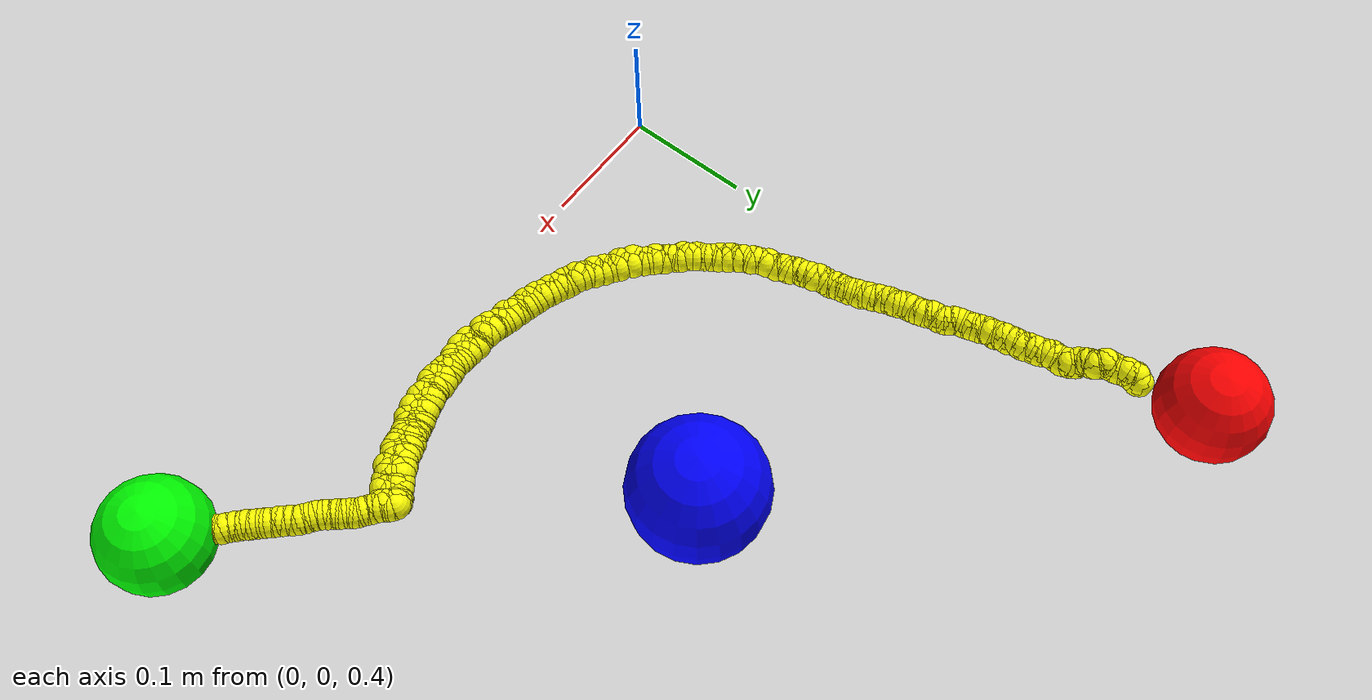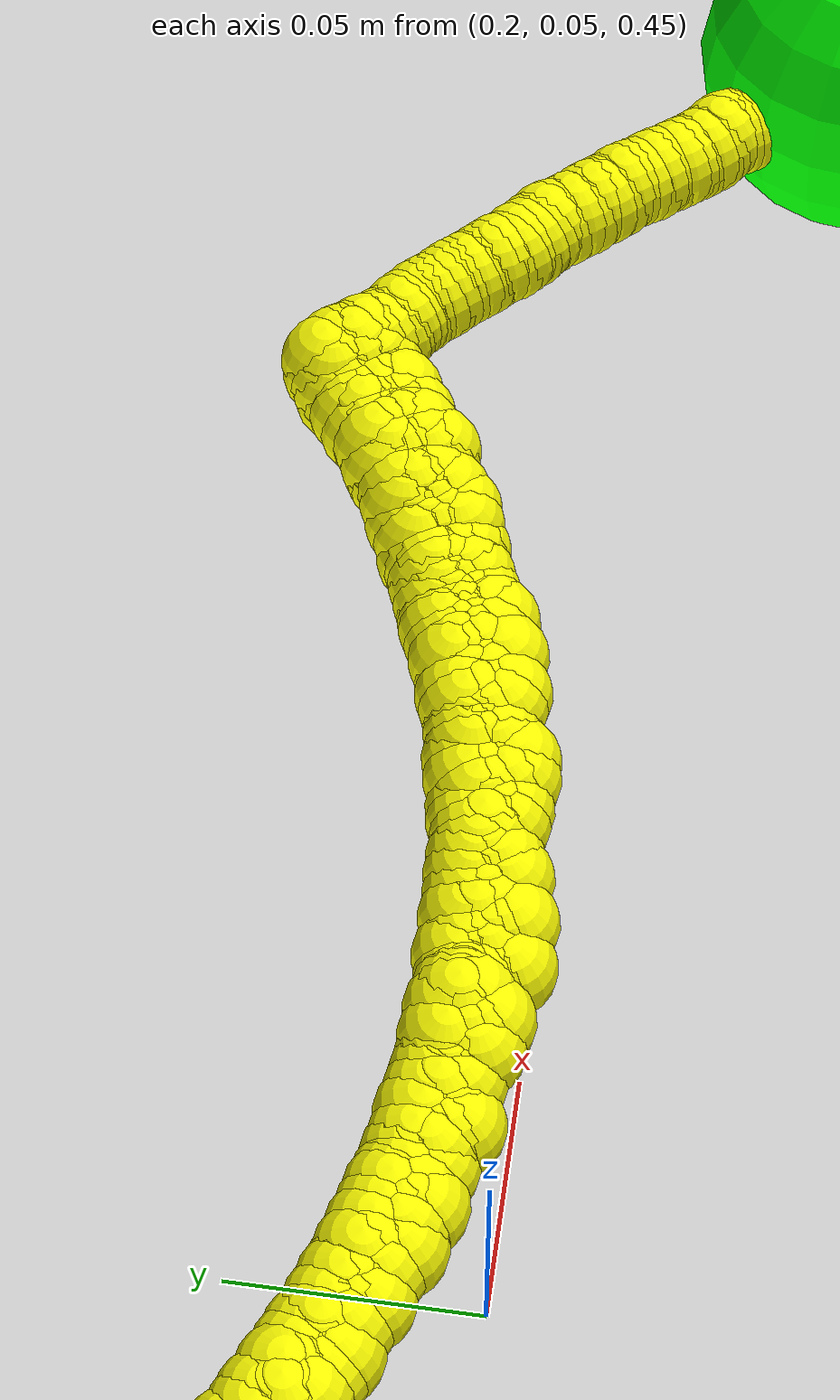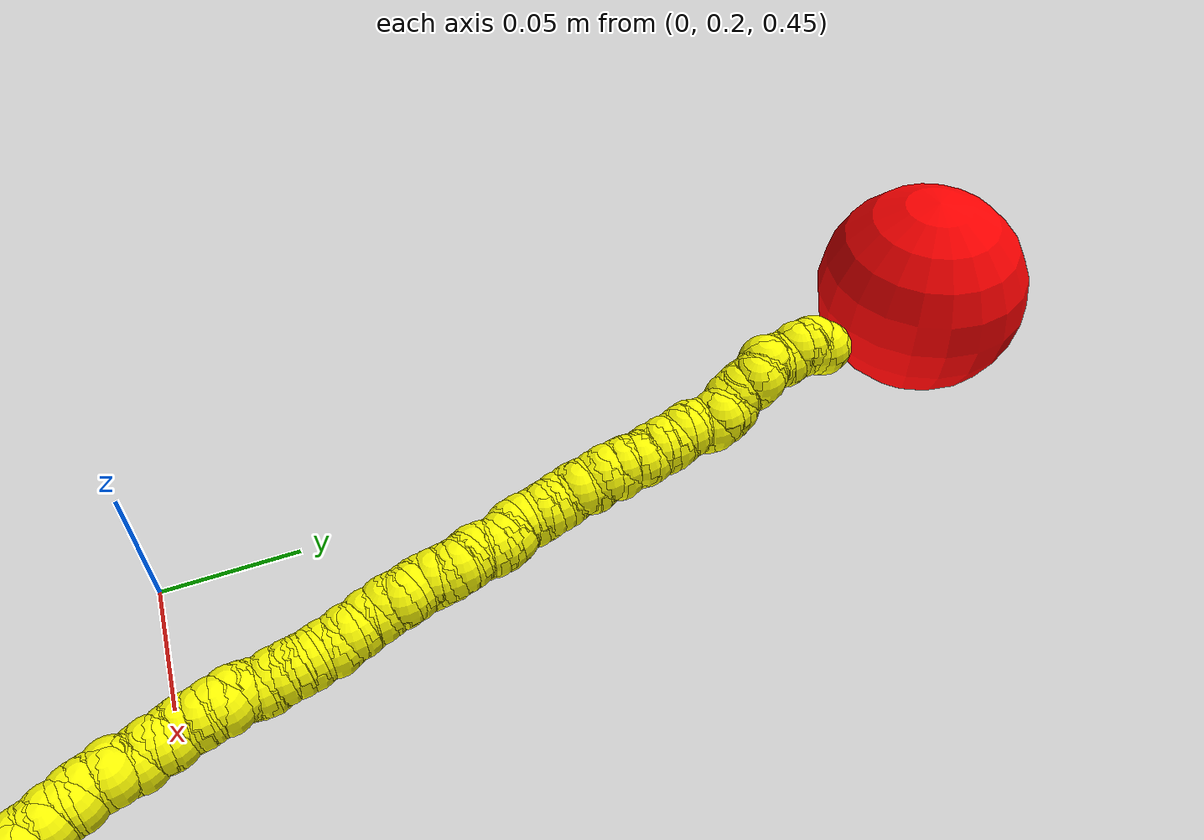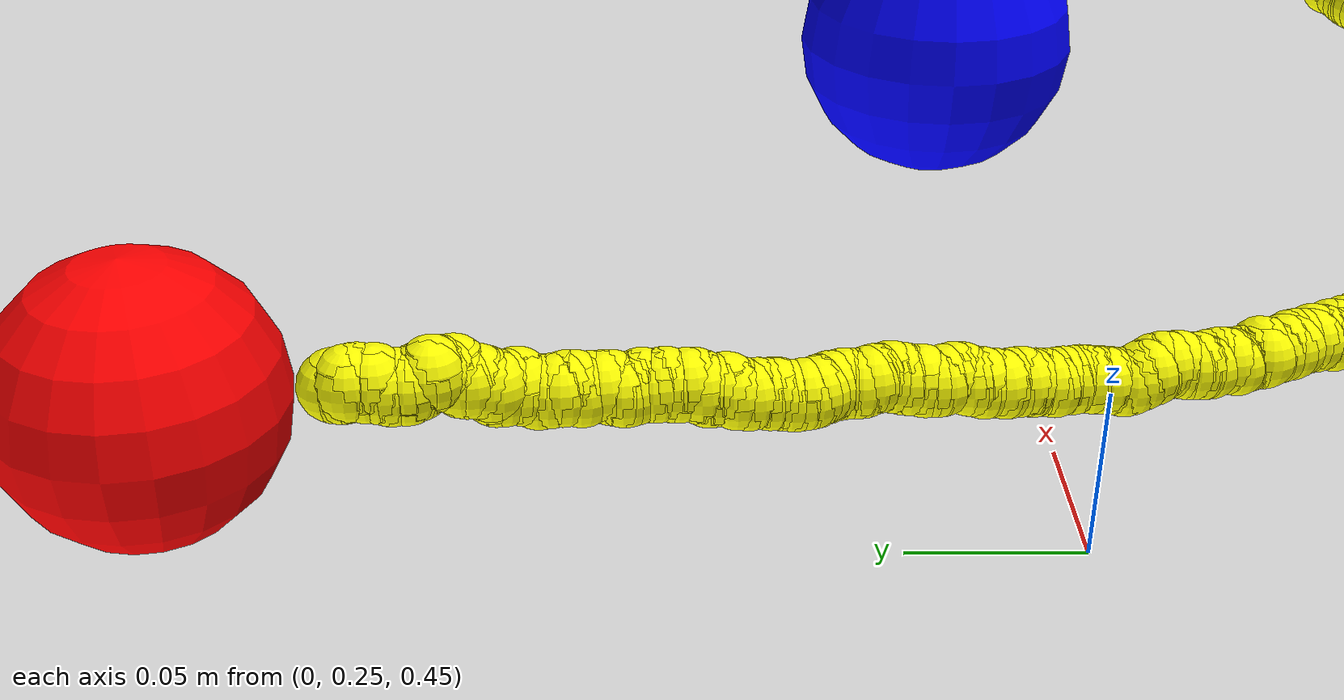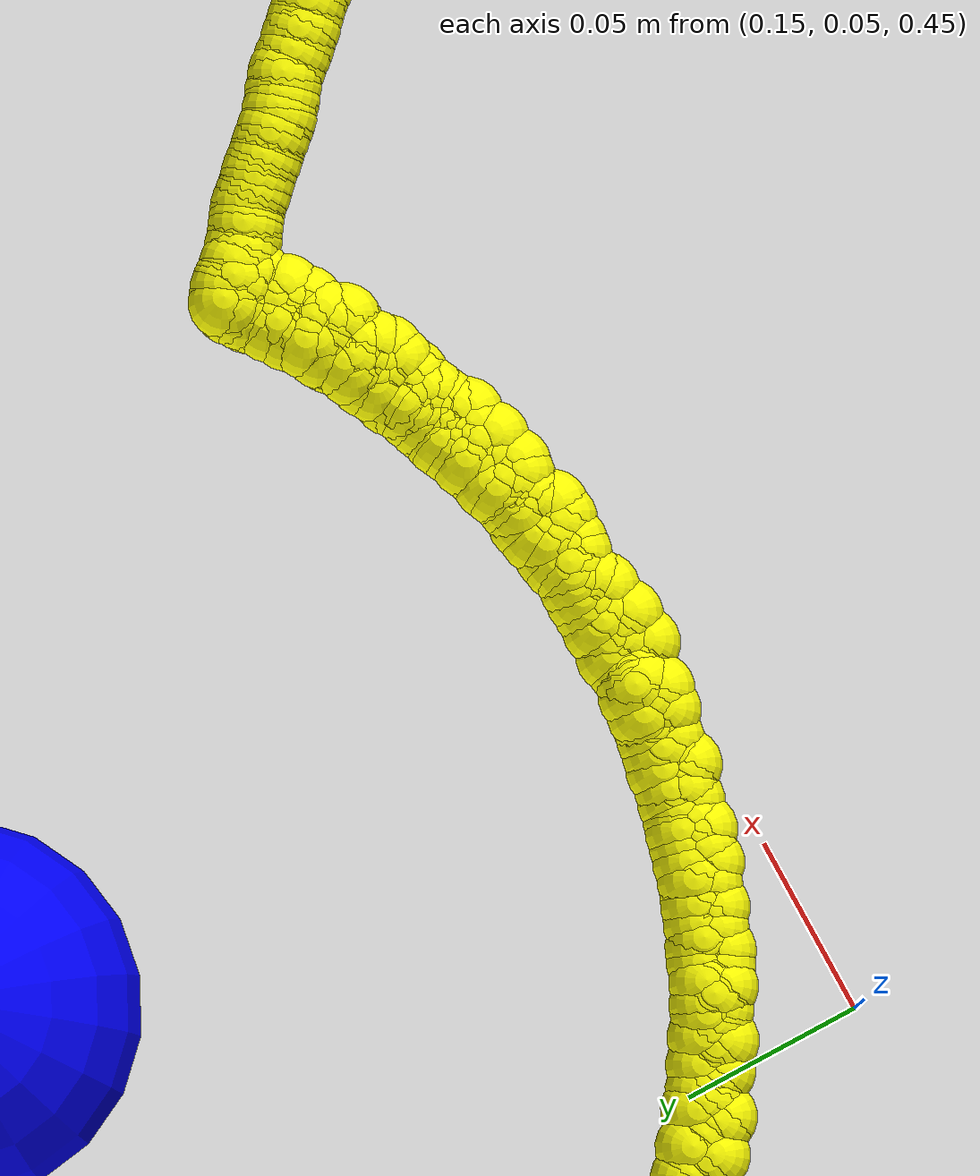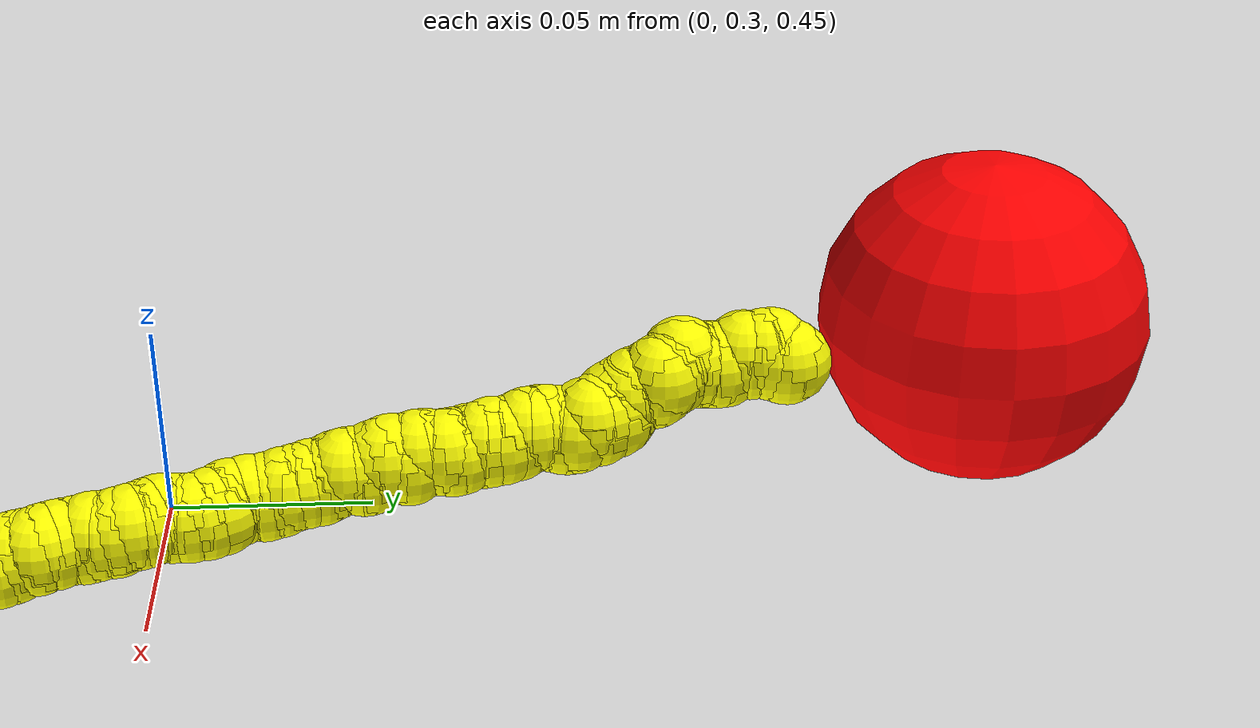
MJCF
<mujoco model="trajectory_visualization">
  <worldbody>
    <body name="start" pos="0.5 0 0.5">
      <geom type="sphere" size="0.04" rgba="0 1 0 1" />
    </body>
    <body name="goal" pos="0 0.5 0.5">
      <geom type="sphere" size="0.04" rgba="1 0 0 1" />
    </body>
    <body name="obstacle" pos="0.26 0.26 0.5">
      <geom type="sphere" size="0.05" rgba="0 0 1 1" />
    </body>
    <body name="trajectory_point1" pos="0.5 0 0.5">
      <geom type="sphere" size="0.01" rgba="1 1 0 1" />
    </body>
    <body name="trajectory_point2" pos="0.49883 0.00186 0.50027">
      <geom type="sphere" size="0.01" rgba="1 1 0 1" />
    </body>
    <body name="trajectory_point3" pos="0.496984 0.00378442 0.500119">
      <geom type="sphere" size="0.01" rgba="1 1 0 1" />
    </body>
    <body name="trajectory_point4" pos="0.495853 0.00569307 0.500109">
      <geom type="sphere" size="0.01" rgba="1 1 0 1" />
    </body>
    <body name="trajectory_point5" pos="0.494075 0.00729599 0.499879">
      <geom type="sphere" size="0.01" rgba="1 1 0 1" />
    </body>
    <body name="trajectory_point6" pos="0.492993 0.0088641 0.500009">
      <geom type="sphere" size="0.01" rgba="1 1 0 1" />
    </body>
    <body name="trajectory_point7" pos="0.491274 0.0102375 0.499769">
      <geom type="sphere" size="0.01" rgba="1 1 0 1" />
    </body>
    <body name="trajectory_point8" pos="0.49002 0.0115668 0.49938">
      <geom type="sphere" size="0.01" rgba="1 1 0 1" />
    </body>
    <body name="trajectory_point9" pos="0.48873 0.0132021 0.499171">
      <geom type="sphere" size="0.01" rgba="1 1 0 1" />
    </body>
    <body name="trajectory_point10" pos="0.487584 0.0144625 0.499294">
      <geom type="sphere" size="0.01" rgba="1 1 0 1" />
    </body>
    <body name="trajectory_point11" pos="0.485851 0.0160891 0.499146">
      <geom type="sphere" size="0.01" rgba="1 1 0 1" />
    </body>
    <body name="trajectory_point12" pos="0.484183 0.0170608 0.498869">
      <geom type="sphere" size="0.01" rgba="1 1 0 1" />
    </body>
    <body name="trajectory_point13" pos="0.482811 0.0186997 0.499042">
      <geom type="sphere" size="0.01" rgba="1 1 0 1" />
    </body>
    <body name="trajectory_point14" pos="0.481792 0.0202036 0.498655">
      <geom type="sphere" size="0.01" rgba="1 1 0 1" />
    </body>
    <body name="trajectory_point15" pos="0.480267 0.0214329 0.498889">
      <geom type="sphere" size="0.01" rgba="1 1 0 1" />
    </body>
    <body name="trajectory_point16" pos="0.478536 0.0225586 0.499232">
      <geom type="sphere" size="0.01" rgba="1 1 0 1" />
    </body>
    <body name="trajectory_point17" pos="0.476971 0.024471 0.498975">
      <geom type="sphere" size="0.01" rgba="1 1 0 1" />
    </body>
    <body name="trajectory_point18" pos="0.47519 0.0260976 0.498608">
      <geom type="sphere" size="0.01" rgba="1 1 0 1" />
    </body>
    <body name="trajectory_point19" pos="0.473524 0.0279293 0.498912">
      <geom type="sphere" size="0.01" rgba="1 1 0 1" />
    </body>
    <body name="trajectory_point20" pos="0.472164 0.0295755 0.499035">
      <geom type="sphere" size="0.01" rgba="1 1 0 1" />
    </body>
    <body name="trajectory_point21" pos="0.470947 0.0314467 0.499348">
      <geom type="sphere" size="0.01" rgba="1 1 0 1" />
    </body>
    <body name="trajectory_point22" pos="0.469084 0.0326024 0.49969">
      <geom type="sphere" size="0.01" rgba="1 1 0 1" />
    </body>
    <body name="trajectory_point23" pos="0.467447 0.0338646 0.499241">
      <geom type="sphere" size="0.01" rgba="1 1 0 1" />
    </body>
    <body name="trajectory_point24" pos="0.466005 0.035053 0.498873">
      <geom type="sphere" size="0.01" rgba="1 1 0 1" />
    </body>
    <body name="trajectory_point25" pos="0.464677 0.0361878 0.499326">
      <geom type="sphere" size="0.01" rgba="1 1 0 1" />
    </body>
    <body name="trajectory_point26" pos="0.463603 0.0375293 0.498968">
      <geom type="sphere" size="0.01" rgba="1 1 0 1" />
    </body>
    <body name="trajectory_point27" pos="0.462382 0.0387567 0.499112">
      <geom type="sphere" size="0.01" rgba="1 1 0 1" />
    </body>
    <body name="trajectory_point28" pos="0.460925 0.0401404 0.499484">
      <geom type="sphere" size="0.01" rgba="1 1 0 1" />
    </body>
    <body name="trajectory_point29" pos="0.459122 0.04178 0.499766">
      <geom type="sphere" size="0.01" rgba="1 1 0 1" />
    </body>
    <body name="trajectory_point30" pos="0.458125 0.0434947 0.499296">
      <geom type="sphere" size="0.01" rgba="1 1 0 1" />
    </body>
    <body name="trajectory_point31" pos="0.45676 0.0449042 0.499789">
      <geom type="sphere" size="0.01" rgba="1 1 0 1" />
    </body>
    <body name="trajectory_point32" pos="0.45521 0.0463695 0.500049">
      <geom type="sphere" size="0.01" rgba="1 1 0 1" />
    </body>
    <body name="trajectory_point33" pos="0.454024 0.0476204 0.499669">
      <geom type="sphere" size="0.01" rgba="1 1 0 1" />
    </body>
    <body name="trajectory_point34" pos="0.452422 0.0493375 0.50011">
      <geom type="sphere" size="0.01" rgba="1 1 0 1" />
    </body>
    <body name="trajectory_point35" pos="0.450955 0.0511395 0.50031">
      <geom type="sphere" size="0.01" rgba="1 1 0 1" />
    </body>
    <body name="trajectory_point36" pos="0.449442 0.0527661 0.500479">
      <geom type="sphere" size="0.01" rgba="1 1 0 1" />
    </body>
    <body name="trajectory_point37" pos="0.447604 0.0545778 0.499997">
      <geom type="sphere" size="0.01" rgba="1 1 0 1" />
    </body>
    <body name="trajectory_point38" pos="0.445931 0.056334 0.500017">
      <geom type="sphere" size="0.01" rgba="1 1 0 1" />
    </body>
    <body name="trajectory_point39" pos="0.444653 0.057175 0.500317">
      <geom type="sphere" size="0.01" rgba="1 1 0 1" />
    </body>
    <body name="trajectory_point40" pos="0.443679 0.0584135 0.500466">
      <geom type="sphere" size="0.01" rgba="1 1 0 1" />
    </body>
    <body name="trajectory_point41" pos="0.442738 0.0596783 0.500155">
      <geom type="sphere" size="0.01" rgba="1 1 0 1" />
    </body>
    <body name="trajectory_point42" pos="0.44131 0.0607892 0.499965">
      <geom type="sphere" size="0.01" rgba="1 1 0 1" />
    </body>
    <body name="trajectory_point43" pos="0.439656 0.0625769 0.500175">
      <geom type="sphere" size="0.01" rgba="1 1 0 1" />
    </body>
    <body name="trajectory_point44" pos="0.438647 0.0641391 0.499764">
      <geom type="sphere" size="0.01" rgba="1 1 0 1" />
    </body>
    <body name="trajectory_point45" pos="0.437101 0.0656167 0.499825">
      <geom type="sphere" size="0.01" rgba="1 1 0 1" />
    </body>
    <body name="trajectory_point46" pos="0.43626 0.0669499 0.500185">
      <geom type="sphere" size="0.01" rgba="1 1 0 1" />
    </body>
    <body name="trajectory_point47" pos="0.435101 0.067809 0.500515">
      <geom type="sphere" size="0.01" rgba="1 1 0 1" />
    </body>
    <body name="trajectory_point48" pos="0.433486 0.0688456 0.500293">
      <geom type="sphere" size="0.01" rgba="1 1 0 1" />
    </body>
    <body name="trajectory_point49" pos="0.432395 0.0699591 0.500082">
      <geom type="sphere" size="0.01" rgba="1 1 0 1" />
    </body>
    <body name="trajectory_point50" pos="0.430628 0.0709392 0.500282">
      <geom type="sphere" size="0.01" rgba="1 1 0 1" />
    </body>
    <body name="trajectory_point51" pos="0.429516 0.0718064 0.499931">
      <geom type="sphere" size="0.01" rgba="1 1 0 1" />
    </body>
    <body name="trajectory_point52" pos="0.428128 0.0730809 0.500391">
      <geom type="sphere" size="0.01" rgba="1 1 0 1" />
    </body>
    <body name="trajectory_point53" pos="0.426573 0.0740417 0.50034">
      <geom type="sphere" size="0.01" rgba="1 1 0 1" />
    </body>
    <body name="trajectory_point54" pos="0.425254 0.0753296 0.500049">
      <geom type="sphere" size="0.01" rgba="1 1 0 1" />
    </body>
    <body name="trajectory_point55" pos="0.424028 0.0768936 0.500429">
      <geom type="sphere" size="0.01" rgba="1 1 0 1" />
    </body>
    <body name="trajectory_point56" pos="0.422896 0.0779429 0.500338">
      <geom type="sphere" size="0.01" rgba="1 1 0 1" />
    </body>
    <body name="trajectory_point57" pos="0.421627 0.0796391 0.499837">
      <geom type="sphere" size="0.01" rgba="1 1 0 1" />
    </body>
    <body name="trajectory_point58" pos="0.420202 0.0810402 0.499577">
      <geom type="sphere" size="0.01" rgba="1 1 0 1" />
    </body>
    <body name="trajectory_point59" pos="0.418581 0.082667 0.499639">
      <geom type="sphere" size="0.01" rgba="1 1 0 1" />
    </body>
    <body name="trajectory_point60" pos="0.417256 0.084329 0.49941">
      <geom type="sphere" size="0.01" rgba="1 1 0 1" />
    </body>
    <body name="trajectory_point61" pos="0.416154 0.085666 0.499271">
      <geom type="sphere" size="0.01" rgba="1 1 0 1" />
    </body>
    <body name="trajectory_point62" pos="0.414726 0.086919 0.499144">
      <geom type="sphere" size="0.01" rgba="1 1 0 1" />
    </body>
    <body name="trajectory_point63" pos="0.413261 0.0884083 0.498716">
      <geom type="sphere" size="0.01" rgba="1 1 0 1" />
    </body>
    <body name="trajectory_point64" pos="0.412262 0.0893531 0.4988">
      <geom type="sphere" size="0.01" rgba="1 1 0 1" />
    </body>
    <body name="trajectory_point65" pos="0.411475 0.090375 0.498674">
      <geom type="sphere" size="0.01" rgba="1 1 0 1" />
    </body>
    <body name="trajectory_point66" pos="0.41009 0.0920339 0.498358">
      <geom type="sphere" size="0.01" rgba="1 1 0 1" />
    </body>
    <body name="trajectory_point67" pos="0.40864 0.0931878 0.497973">
      <geom type="sphere" size="0.01" rgba="1 1 0 1" />
    </body>
    <body name="trajectory_point68" pos="0.407194 0.0941982 0.498239">
      <geom type="sphere" size="0.01" rgba="1 1 0 1" />
    </body>
    <body name="trajectory_point69" pos="0.405513 0.0953456 0.498374">
      <geom type="sphere" size="0.01" rgba="1 1 0 1" />
    </body>
    <body name="trajectory_point70" pos="0.403926 0.0964396 0.497939">
      <geom type="sphere" size="0.01" rgba="1 1 0 1" />
    </body>
    <body name="trajectory_point71" pos="0.402614 0.0971903 0.497625">
      <geom type="sphere" size="0.01" rgba="1 1 0 1" />
    </body>
    <body name="trajectory_point72" pos="0.401186 0.0987787 0.497822">
      <geom type="sphere" size="0.01" rgba="1 1 0 1" />
    </body>
    <body name="trajectory_point73" pos="0.399653 0.0996524 0.498289">
      <geom type="sphere" size="0.01" rgba="1 1 0 1" />
    </body>
    <body name="trajectory_point74" pos="0.398194 0.100783 0.498494">
      <geom type="sphere" size="0.01" rgba="1 1 0 1" />
    </body>
    <body name="trajectory_point75" pos="0.397329 0.102381 0.498988">
      <geom type="sphere" size="0.01" rgba="1 1 0 1" />
    </body>
    <body name="trajectory_point76" pos="0.396357 0.103324 0.498931">
      <geom type="sphere" size="0.01" rgba="1 1 0 1" />
    </body>
    <body name="trajectory_point77" pos="0.395568 0.104064 0.498825">
      <geom type="sphere" size="0.01" rgba="1 1 0 1" />
    </body>
    <body name="trajectory_point78" pos="0.394422 0.105612 0.499018">
      <geom type="sphere" size="0.01" rgba="1 1 0 1" />
    </body>
    <body name="trajectory_point79" pos="0.393558 0.106715 0.499161">
      <geom type="sphere" size="0.01" rgba="1 1 0 1" />
    </body>
    <body name="trajectory_point80" pos="0.392848 0.107465 0.499214">
      <geom type="sphere" size="0.01" rgba="1 1 0 1" />
    </body>
    <body name="trajectory_point81" pos="0.391209 0.108622 0.498826">
      <geom type="sphere" size="0.01" rgba="1 1 0 1" />
    </body>
    <body name="trajectory_point82" pos="0.389755 0.109577 0.499319">
      <geom type="sphere" size="0.01" rgba="1 1 0 1" />
    </body>
    <body name="trajectory_point83" pos="0.393861 0.104511 0.499473">
      <geom type="sphere" size="0.01" rgba="1 1 0 1" />
    </body>
    <body name="trajectory_point84" pos="0.39258 0.105418 0.499085">
      <geom type="sphere" size="0.01" rgba="1 1 0 1" />
    </body>
    <body name="trajectory_point85" pos="0.391002 0.106152 0.498598">
      <geom type="sphere" size="0.01" rgba="1 1 0 1" />
    </body>
    <body name="trajectory_point86" pos="0.389939 0.107133 0.498882">
      <geom type="sphere" size="0.01" rgba="1 1 0 1" />
    </body>
    <body name="trajectory_point87" pos="0.388319 0.108012 0.498745">
      <geom type="sphere" size="0.01" rgba="1 1 0 1" />
    </body>
    <body name="trajectory_point88" pos="0.391328 0.103933 0.498428">
      <geom type="sphere" size="0.01" rgba="1 1 0 1" />
    </body>
    <body name="trajectory_point89" pos="0.390304 0.104702 0.498092">
      <geom type="sphere" size="0.01" rgba="1 1 0 1" />
    </body>
    <body name="trajectory_point90" pos="0.389453 0.105967 0.497838">
      <geom type="sphere" size="0.01" rgba="1 1 0 1" />
    </body>
    <body name="trajectory_point91" pos="0.388154 0.10727 0.497585">
      <geom type="sphere" size="0.01" rgba="1 1 0 1" />
    </body>
    <body name="trajectory_point92" pos="0.388846 0.1055 0.497567">
      <geom type="sphere" size="0.01" rgba="1 1 0 1" />
    </body>
    <body name="trajectory_point93" pos="0.388169 0.106973 0.497575">
      <geom type="sphere" size="0.01" rgba="1 1 0 1" />
    </body>
    <body name="trajectory_point94" pos="0.388619 0.10665 0.497785">
      <geom type="sphere" size="0.01" rgba="1 1 0 1" />
    </body>
    <body name="trajectory_point95" pos="0.387263 0.10814 0.497592">
      <geom type="sphere" size="0.01" rgba="1 1 0 1" />
    </body>
    <body name="trajectory_point96" pos="0.393242 0.101032 0.49756">
      <geom type="sphere" size="0.01" rgba="1 1 0 1" />
    </body>
    <body name="trajectory_point97" pos="0.392193 0.102719 0.497878">
      <geom type="sphere" size="0.01" rgba="1 1 0 1" />
    </body>
    <body name="trajectory_point98" pos="0.391506 0.10437 0.497974">
      <geom type="sphere" size="0.01" rgba="1 1 0 1" />
    </body>
    <body name="trajectory_point99" pos="0.390562 0.105187 0.49816">
      <geom type="sphere" size="0.01" rgba="1 1 0 1" />
    </body>
    <body name="trajectory_point100" pos="0.38979 0.106822 0.497926">
      <geom type="sphere" size="0.01" rgba="1 1 0 1" />
    </body>
    <body name="trajectory_point101" pos="0.38878 0.108341 0.497832">
      <geom type="sphere" size="0.01" rgba="1 1 0 1" />
    </body>
    <body name="trajectory_point102" pos="0.392043 0.105112 0.498031">
      <geom type="sphere" size="0.01" rgba="1 1 0 1" />
    </body>
    <body name="trajectory_point103" pos="0.390787 0.106156 0.497606">
      <geom type="sphere" size="0.01" rgba="1 1 0 1" />
    </body>
    <body name="trajectory_point104" pos="0.389565 0.107398 0.497904">
      <geom type="sphere" size="0.01" rgba="1 1 0 1" />
    </body>
    <body name="trajectory_point105" pos="0.388076 0.108946 0.49753">
      <geom type="sphere" size="0.01" rgba="1 1 0 1" />
    </body>
    <body name="trajectory_point106" pos="0.39463 0.101212 0.497478">
      <geom type="sphere" size="0.01" rgba="1 1 0 1" />
    </body>
    <body name="trajectory_point107" pos="0.393036 0.102268 0.497086">
      <geom type="sphere" size="0.01" rgba="1 1 0 1" />
    </body>
    <body name="trajectory_point108" pos="0.391777 0.103832 0.496654">
      <geom type="sphere" size="0.01" rgba="1 1 0 1" />
    </body>
    <body name="trajectory_point109" pos="0.390112 0.10465 0.496884">
      <geom type="sphere" size="0.01" rgba="1 1 0 1" />
    </body>
    <body name="trajectory_point110" pos="0.388651 0.105886 0.496584">
      <geom type="sphere" size="0.01" rgba="1 1 0 1" />
    </body>
    <body name="trajectory_point111" pos="0.387975 0.106778 0.496134">
      <geom type="sphere" size="0.01" rgba="1 1 0 1" />
    </body>
    <body name="trajectory_point112" pos="0.38795 0.106074 0.496008">
      <geom type="sphere" size="0.01" rgba="1 1 0 1" />
    </body>
    <body name="trajectory_point113" pos="0.386956 0.106805 0.4958">
      <geom type="sphere" size="0.01" rgba="1 1 0 1" />
    </body>
    <body name="trajectory_point114" pos="0.389392 0.103368 0.496026">
      <geom type="sphere" size="0.01" rgba="1 1 0 1" />
    </body>
    <body name="trajectory_point115" pos="0.388303 0.104258 0.495778">
      <geom type="sphere" size="0.01" rgba="1 1 0 1" />
    </body>
    <body name="trajectory_point116" pos="0.386859 0.105635 0.496251">
      <geom type="sphere" size="0.01" rgba="1 1 0 1" />
    </body>
    <body name="trajectory_point117" pos="0.386614 0.10588 0.496584">
      <geom type="sphere" size="0.01" rgba="1 1 0 1" />
    </body>
    <body name="trajectory_point118" pos="0.387817 0.104918 0.496762">
      <geom type="sphere" size="0.01" rgba="1 1 0 1" />
    </body>
    <body name="trajectory_point119" pos="0.386654 0.105853 0.497121">
      <geom type="sphere" size="0.01" rgba="1 1 0 1" />
    </body>
    <body name="trajectory_point120" pos="0.387013 0.105336 0.496989">
      <geom type="sphere" size="0.01" rgba="1 1 0 1" />
    </body>
    <body name="trajectory_point121" pos="0.385772 0.107 0.496628">
      <geom type="sphere" size="0.01" rgba="1 1 0 1" />
    </body>
    <body name="trajectory_point122" pos="0.39257 0.0994848 0.496178">
      <geom type="sphere" size="0.01" rgba="1 1 0 1" />
    </body>
    <body name="trajectory_point123" pos="0.391792 0.100276 0.496499">
      <geom type="sphere" size="0.01" rgba="1 1 0 1" />
    </body>
    <body name="trajectory_point124" pos="0.390307 0.101336 0.49633">
      <geom type="sphere" size="0.01" rgba="1 1 0 1" />
    </body>
    <body name="trajectory_point125" pos="0.389186 0.102971 0.495881">
      <geom type="sphere" size="0.01" rgba="1 1 0 1" />
    </body>
    <body name="trajectory_point126" pos="0.388308 0.104353 0.496123">
      <geom type="sphere" size="0.01" rgba="1 1 0 1" />
    </body>
    <body name="trajectory_point127" pos="0.387404 0.10554 0.496185">
      <geom type="sphere" size="0.01" rgba="1 1 0 1" />
    </body>
    <body name="trajectory_point128" pos="0.386341 0.106643 0.496486">
      <geom type="sphere" size="0.01" rgba="1 1 0 1" />
    </body>
    <body name="trajectory_point129" pos="0.390438 0.102286 0.49591">
      <geom type="sphere" size="0.01" rgba="1 1 0 1" />
    </body>
    <body name="trajectory_point130" pos="0.388977 0.103649 0.495462">
      <geom type="sphere" size="0.01" rgba="1 1 0 1" />
    </body>
    <body name="trajectory_point131" pos="0.38744 0.104948 0.495516">
      <geom type="sphere" size="0.01" rgba="1 1 0 1" />
    </body>
    <body name="trajectory_point132" pos="0.386037 0.106224 0.495469">
      <geom type="sphere" size="0.01" rgba="1 1 0 1" />
    </body>
    <body name="trajectory_point133" pos="0.388702 0.101675 0.494888">
      <geom type="sphere" size="0.01" rgba="1 1 0 1" />
    </body>
    <body name="trajectory_point134" pos="0.387876 0.10258 0.494824">
      <geom type="sphere" size="0.01" rgba="1 1 0 1" />
    </body>
    <body name="trajectory_point135" pos="0.386892 0.103552 0.495229">
      <geom type="sphere" size="0.01" rgba="1 1 0 1" />
    </body>
    <body name="trajectory_point136" pos="0.385952 0.104322 0.495324">
      <geom type="sphere" size="0.01" rgba="1 1 0 1" />
    </body>
    <body name="trajectory_point137" pos="0.385274 0.105369 0.494918">
      <geom type="sphere" size="0.01" rgba="1 1 0 1" />
    </body>
    <body name="trajectory_point138" pos="0.387668 0.102188 0.49432">
      <geom type="sphere" size="0.01" rgba="1 1 0 1" />
    </body>
    <body name="trajectory_point139" pos="0.386335 0.103211 0.494317">
      <geom type="sphere" size="0.01" rgba="1 1 0 1" />
    </body>
    <body name="trajectory_point140" pos="0.385576 0.104441 0.494504">
      <geom type="sphere" size="0.01" rgba="1 1 0 1" />
    </body>
    <body name="trajectory_point141" pos="0.384398 0.105785 0.49431">
      <geom type="sphere" size="0.01" rgba="1 1 0 1" />
    </body>
    <body name="trajectory_point142" pos="0.389623 0.0984005 0.494392">
      <geom type="sphere" size="0.01" rgba="1 1 0 1" />
    </body>
    <body name="trajectory_point143" pos="0.388924 0.0995953 0.494809">
      <geom type="sphere" size="0.01" rgba="1 1 0 1" />
    </body>
    <body name="trajectory_point144" pos="0.387288 0.100626 0.494955">
      <geom type="sphere" size="0.01" rgba="1 1 0 1" />
    </body>
    <body name="trajectory_point145" pos="0.386596 0.101855 0.49539">
      <geom type="sphere" size="0.01" rgba="1 1 0 1" />
    </body>
    <body name="trajectory_point146" pos="0.385796 0.102799 0.495424">
      <geom type="sphere" size="0.01" rgba="1 1 0 1" />
    </body>
    <body name="trajectory_point147" pos="0.385099 0.104241 0.495817">
      <geom type="sphere" size="0.01" rgba="1 1 0 1" />
    </body>
    <body name="trajectory_point148" pos="0.384683 0.104384 0.495667">
      <geom type="sphere" size="0.01" rgba="1 1 0 1" />
    </body>
    <body name="trajectory_point149" pos="0.385684 0.102646 0.495319">
      <geom type="sphere" size="0.01" rgba="1 1 0 1" />
    </body>
    <body name="trajectory_point150" pos="0.384627 0.103378 0.495113">
      <geom type="sphere" size="0.01" rgba="1 1 0 1" />
    </body>
    <body name="trajectory_point151" pos="0.383243 0.104567 0.495108">
      <geom type="sphere" size="0.01" rgba="1 1 0 1" />
    </body>
    <body name="trajectory_point152" pos="0.38814 0.0977233 0.495325">
      <geom type="sphere" size="0.01" rgba="1 1 0 1" />
    </body>
    <body name="trajectory_point153" pos="0.387446 0.0994202 0.495269">
      <geom type="sphere" size="0.01" rgba="1 1 0 1" />
    </body>
    <body name="trajectory_point154" pos="0.386174 0.100142 0.495063">
      <geom type="sphere" size="0.01" rgba="1 1 0 1" />
    </body>
    <body name="trajectory_point155" pos="0.384545 0.100841 0.495388">
      <geom type="sphere" size="0.01" rgba="1 1 0 1" />
    </body>
    <body name="trajectory_point156" pos="0.383362 0.101919 0.495492">
      <geom type="sphere" size="0.01" rgba="1 1 0 1" />
    </body>
    <body name="trajectory_point157" pos="0.382221 0.102963 0.495345">
      <geom type="sphere" size="0.01" rgba="1 1 0 1" />
    </body>
    <body name="trajectory_point158" pos="0.384494 0.10004 0.494875">
      <geom type="sphere" size="0.01" rgba="1 1 0 1" />
    </body>
    <body name="trajectory_point159" pos="0.38311 0.10078 0.49468">
      <geom type="sphere" size="0.01" rgba="1 1 0 1" />
    </body>
    <body name="trajectory_point160" pos="0.381951 0.102118 0.495046">
      <geom type="sphere" size="0.01" rgba="1 1 0 1" />
    </body>
    <body name="trajectory_point161" pos="0.38221 0.10115 0.494845">
      <geom type="sphere" size="0.01" rgba="1 1 0 1" />
    </body>
    <body name="trajectory_point162" pos="0.381334 0.101847 0.494741">
      <geom type="sphere" size="0.01" rgba="1 1 0 1" />
    </body>
    <body name="trajectory_point163" pos="0.382575 0.100196 0.495052">
      <geom type="sphere" size="0.01" rgba="1 1 0 1" />
    </body>
    <body name="trajectory_point164" pos="0.381597 0.101776 0.495487">
      <geom type="sphere" size="0.01" rgba="1 1 0 1" />
    </body>
    <body name="trajectory_point165" pos="0.382349 0.101018 0.495387">
      <geom type="sphere" size="0.01" rgba="1 1 0 1" />
    </body>
    <body name="trajectory_point166" pos="0.380992 0.102615 0.495721">
      <geom type="sphere" size="0.01" rgba="1 1 0 1" />
    </body>
    <body name="trajectory_point167" pos="0.385089 0.0967701 0.495735">
      <geom type="sphere" size="0.01" rgba="1 1 0 1" />
    </body>
    <body name="trajectory_point168" pos="0.383694 0.0977998 0.495858">
      <geom type="sphere" size="0.01" rgba="1 1 0 1" />
    </body>
    <body name="trajectory_point169" pos="0.382463 0.0991064 0.49554">
      <geom type="sphere" size="0.01" rgba="1 1 0 1" />
    </body>
    <body name="trajectory_point170" pos="0.381045 0.100419 0.495863">
      <geom type="sphere" size="0.01" rgba="1 1 0 1" />
    </body>
    <body name="trajectory_point171" pos="0.379492 0.102018 0.495626">
      <geom type="sphere" size="0.01" rgba="1 1 0 1" />
    </body>
    <body name="trajectory_point172" pos="0.385749 0.0942123 0.495655">
      <geom type="sphere" size="0.01" rgba="1 1 0 1" />
    </body>
    <body name="trajectory_point173" pos="0.384432 0.0958297 0.495428">
      <geom type="sphere" size="0.01" rgba="1 1 0 1" />
    </body>
    <body name="trajectory_point174" pos="0.383019 0.0971122 0.495082">
      <geom type="sphere" size="0.01" rgba="1 1 0 1" />
    </body>
    <body name="trajectory_point175" pos="0.38205 0.0978709 0.495177">
      <geom type="sphere" size="0.01" rgba="1 1 0 1" />
    </body>
    <body name="trajectory_point176" pos="0.380524 0.0994373 0.494691">
      <geom type="sphere" size="0.01" rgba="1 1 0 1" />
    </body>
    <body name="trajectory_point177" pos="0.379342 0.100399 0.495147">
      <geom type="sphere" size="0.01" rgba="1 1 0 1" />
    </body>
    <body name="trajectory_point178" pos="0.380217 0.0984707 0.495346">
      <geom type="sphere" size="0.01" rgba="1 1 0 1" />
    </body>
    <body name="trajectory_point179" pos="0.378867 0.0996353 0.49576">
      <geom type="sphere" size="0.01" rgba="1 1 0 1" />
    </body>
    <body name="trajectory_point180" pos="0.378908 0.0994066 0.495739">
      <geom type="sphere" size="0.01" rgba="1 1 0 1" />
    </body>
    <body name="trajectory_point181" pos="0.378535 0.0997914 0.496166">
      <geom type="sphere" size="0.01" rgba="1 1 0 1" />
    </body>
    <body name="trajectory_point182" pos="0.379866 0.097524 0.49572">
      <geom type="sphere" size="0.01" rgba="1 1 0 1" />
    </body>
    <body name="trajectory_point183" pos="0.379086 0.0983715 0.495782">
      <geom type="sphere" size="0.01" rgba="1 1 0 1" />
    </body>
    <body name="trajectory_point184" pos="0.377569 0.0999763 0.495415">
      <geom type="sphere" size="0.01" rgba="1 1 0 1" />
    </body>
    <body name="trajectory_point185" pos="0.381692 0.0940166 0.495425">
      <geom type="sphere" size="0.01" rgba="1 1 0 1" />
    </body>
    <body name="trajectory_point186" pos="0.380937 0.0954746 0.495489">
      <geom type="sphere" size="0.01" rgba="1 1 0 1" />
    </body>
    <body name="trajectory_point187" pos="0.379705 0.0963882 0.495332">
      <geom type="sphere" size="0.01" rgba="1 1 0 1" />
    </body>
    <body name="trajectory_point188" pos="0.378935 0.097979 0.495226">
      <geom type="sphere" size="0.01" rgba="1 1 0 1" />
    </body>
    <body name="trajectory_point189" pos="0.377959 0.099385 0.495581">
      <geom type="sphere" size="0.01" rgba="1 1 0 1" />
    </body>
    <body name="trajectory_point190" pos="0.37928 0.0969957 0.495064">
      <geom type="sphere" size="0.01" rgba="1 1 0 1" />
    </body>
    <body name="trajectory_point191" pos="0.378242 0.0981947 0.494949">
      <geom type="sphere" size="0.01" rgba="1 1 0 1" />
    </body>
    <body name="trajectory_point192" pos="0.376657 0.0994902 0.494634">
      <geom type="sphere" size="0.01" rgba="1 1 0 1" />
    </body>
    <body name="trajectory_point193" pos="0.380602 0.0932194 0.494732">
      <geom type="sphere" size="0.01" rgba="1 1 0 1" />
    </body>
    <body name="trajectory_point194" pos="0.37969 0.0945197 0.494978">
      <geom type="sphere" size="0.01" rgba="1 1 0 1" />
    </body>
    <body name="trajectory_point195" pos="0.378421 0.0961262 0.495323">
      <geom type="sphere" size="0.01" rgba="1 1 0 1" />
    </body>
    <body name="trajectory_point196" pos="0.376856 0.0976178 0.495407">
      <geom type="sphere" size="0.01" rgba="1 1 0 1" />
    </body>
    <body name="trajectory_point197" pos="0.375365 0.0990349 0.495211">
      <geom type="sphere" size="0.01" rgba="1 1 0 1" />
    </body>
    <body name="trajectory_point198" pos="0.380569 0.0907984 0.494622">
      <geom type="sphere" size="0.01" rgba="1 1 0 1" />
    </body>
    <body name="trajectory_point199" pos="0.379307 0.091776 0.495018">
      <geom type="sphere" size="0.01" rgba="1 1 0 1" />
    </body>
    <body name="trajectory_point200" pos="0.378409 0.0928306 0.495103">
      <geom type="sphere" size="0.01" rgba="1 1 0 1" />
    </body>
    <body name="trajectory_point201" pos="0.377584 0.0944821 0.495197">
      <geom type="sphere" size="0.01" rgba="1 1 0 1" />
    </body>
    <body name="trajectory_point202" pos="0.376651 0.0961887 0.494882">
      <geom type="sphere" size="0.01" rgba="1 1 0 1" />
    </body>
    <body name="trajectory_point203" pos="0.375411 0.0975901 0.495027">
      <geom type="sphere" size="0.01" rgba="1 1 0 1" />
    </body>
    <body name="trajectory_point204" pos="0.376433 0.0958213 0.495167">
      <geom type="sphere" size="0.01" rgba="1 1 0 1" />
    </body>
    <body name="trajectory_point205" pos="0.375273 0.0968438 0.495302">
      <geom type="sphere" size="0.01" rgba="1 1 0 1" />
    </body>
    <body name="trajectory_point206" pos="0.375069 0.0976024 0.495712">
      <geom type="sphere" size="0.01" rgba="1 1 0 1" />
    </body>
    <body name="trajectory_point207" pos="0.377569 0.0943409 0.495255">
      <geom type="sphere" size="0.01" rgba="1 1 0 1" />
    </body>
    <body name="trajectory_point208" pos="0.376147 0.0956278 0.495509">
      <geom type="sphere" size="0.01" rgba="1 1 0 1" />
    </body>
    <body name="trajectory_point209" pos="0.375428 0.096811 0.495532">
      <geom type="sphere" size="0.01" rgba="1 1 0 1" />
    </body>
    <body name="trajectory_point210" pos="0.374332 0.0974193 0.495407">
      <geom type="sphere" size="0.01" rgba="1 1 0 1" />
    </body>
    <body name="trajectory_point211" pos="0.377263 0.0927608 0.495054">
      <geom type="sphere" size="0.01" rgba="1 1 0 1" />
    </body>
    <body name="trajectory_point212" pos="0.376611 0.0937325 0.495379">
      <geom type="sphere" size="0.01" rgba="1 1 0 1" />
    </body>
    <body name="trajectory_point213" pos="0.375141 0.0946113 0.494913">
      <geom type="sphere" size="0.01" rgba="1 1 0 1" />
    </body>
    <body name="trajectory_point214" pos="0.373825 0.0957175 0.495388">
      <geom type="sphere" size="0.01" rgba="1 1 0 1" />
    </body>
    <body name="trajectory_point215" pos="0.372529 0.0963987 0.49569">
      <geom type="sphere" size="0.01" rgba="1 1 0 1" />
    </body>
    <body name="trajectory_point216" pos="0.375883 0.0903532 0.49572">
      <geom type="sphere" size="0.01" rgba="1 1 0 1" />
    </body>
    <body name="trajectory_point217" pos="0.374876 0.0912021 0.496023">
      <geom type="sphere" size="0.01" rgba="1 1 0 1" />
    </body>
    <body name="trajectory_point218" pos="0.374021 0.0927785 0.495895">
      <geom type="sphere" size="0.01" rgba="1 1 0 1" />
    </body>
    <body name="trajectory_point219" pos="0.372439 0.0942602 0.496237">
      <geom type="sphere" size="0.01" rgba="1 1 0 1" />
    </body>
    <body name="trajectory_point220" pos="0.370892 0.0955674 0.496318">
      <geom type="sphere" size="0.01" rgba="1 1 0 1" />
    </body>
    <body name="trajectory_point221" pos="0.375317 0.0889696 0.495753">
      <geom type="sphere" size="0.01" rgba="1 1 0 1" />
    </body>
    <body name="trajectory_point222" pos="0.373961 0.0902027 0.495626">
      <geom type="sphere" size="0.01" rgba="1 1 0 1" />
    </body>
    <body name="trajectory_point223" pos="0.372939 0.0911121 0.495189">
      <geom type="sphere" size="0.01" rgba="1 1 0 1" />
    </body>
    <body name="trajectory_point224" pos="0.37195 0.0923288 0.495144">
      <geom type="sphere" size="0.01" rgba="1 1 0 1" />
    </body>
    <body name="trajectory_point225" pos="0.370445 0.0931018 0.494998">
      <geom type="sphere" size="0.01" rgba="1 1 0 1" />
    </body>
    <body name="trajectory_point226" pos="0.369743 0.0945725 0.495063">
      <geom type="sphere" size="0.01" rgba="1 1 0 1" />
    </body>
    <body name="trajectory_point227" pos="0.373057 0.0889684 0.495043">
      <geom type="sphere" size="0.01" rgba="1 1 0 1" />
    </body>
    <body name="trajectory_point228" pos="0.372368 0.0898815 0.494608">
      <geom type="sphere" size="0.01" rgba="1 1 0 1" />
    </body>
    <body name="trajectory_point229" pos="0.371571 0.0908319 0.494944">
      <geom type="sphere" size="0.01" rgba="1 1 0 1" />
    </body>
    <body name="trajectory_point230" pos="0.370126 0.0918594 0.495389">
      <geom type="sphere" size="0.01" rgba="1 1 0 1" />
    </body>
    <body name="trajectory_point231" pos="0.369256 0.0928438 0.495833">
      <geom type="sphere" size="0.01" rgba="1 1 0 1" />
    </body>
    <body name="trajectory_point232" pos="0.369361 0.092791 0.495743">
      <geom type="sphere" size="0.01" rgba="1 1 0 1" />
    </body>
    <body name="trajectory_point233" pos="0.369007 0.0928657 0.495366">
      <geom type="sphere" size="0.01" rgba="1 1 0 1" />
    </body>
    <body name="trajectory_point234" pos="0.369513 0.0923283 0.495443">
      <geom type="sphere" size="0.01" rgba="1 1 0 1" />
    </body>
    <body name="trajectory_point235" pos="0.368655 0.0939313 0.495147">
      <geom type="sphere" size="0.01" rgba="1 1 0 1" />
    </body>
    <body name="trajectory_point236" pos="0.372111 0.0873852 0.49538">
      <geom type="sphere" size="0.01" rgba="1 1 0 1" />
    </body>
    <body name="trajectory_point237" pos="0.370665 0.088583 0.495244">
      <geom type="sphere" size="0.01" rgba="1 1 0 1" />
    </body>
    <body name="trajectory_point238" pos="0.369423 0.0902273 0.495288">
      <geom type="sphere" size="0.01" rgba="1 1 0 1" />
    </body>
    <body name="trajectory_point239" pos="0.368245 0.0916866 0.495082">
      <geom type="sphere" size="0.01" rgba="1 1 0 1" />
    </body>
    <body name="trajectory_point240" pos="0.36689 0.0933215 0.494697">
      <geom type="sphere" size="0.01" rgba="1 1 0 1" />
    </body>
    <body name="trajectory_point241" pos="0.371855 0.0842545 0.494256">
      <geom type="sphere" size="0.01" rgba="1 1 0 1" />
    </body>
    <body name="trajectory_point242" pos="0.370869 0.0855518 0.494673">
      <geom type="sphere" size="0.01" rgba="1 1 0 1" />
    </body>
    <body name="trajectory_point243" pos="0.369836 0.0865951 0.494229">
      <geom type="sphere" size="0.01" rgba="1 1 0 1" />
    </body>
    <body name="trajectory_point244" pos="0.368937 0.0879453 0.494076">
      <geom type="sphere" size="0.01" rgba="1 1 0 1" />
    </body>
    <body name="trajectory_point245" pos="0.36818 0.0895715 0.494324">
      <geom type="sphere" size="0.01" rgba="1 1 0 1" />
    </body>
    <body name="trajectory_point246" pos="0.366616 0.0908128 0.493891">
      <geom type="sphere" size="0.01" rgba="1 1 0 1" />
    </body>
    <body name="trajectory_point247" pos="0.365516 0.0922203 0.49344">
      <geom type="sphere" size="0.01" rgba="1 1 0 1" />
    </body>
    <body name="trajectory_point248" pos="0.370284 0.0842344 0.493566">
      <geom type="sphere" size="0.01" rgba="1 1 0 1" />
    </body>
    <body name="trajectory_point249" pos="0.369063 0.0854717 0.493286">
      <geom type="sphere" size="0.01" rgba="1 1 0 1" />
    </body>
    <body name="trajectory_point250" pos="0.368126 0.0864753 0.493436">
      <geom type="sphere" size="0.01" rgba="1 1 0 1" />
    </body>
    <body name="trajectory_point251" pos="0.367292 0.0881759 0.493766">
      <geom type="sphere" size="0.01" rgba="1 1 0 1" />
    </body>
    <body name="trajectory_point252" pos="0.36634 0.0895113 0.493644">
      <geom type="sphere" size="0.01" rgba="1 1 0 1" />
    </body>
    <body name="trajectory_point253" pos="0.365291 0.0909428 0.493343">
      <geom type="sphere" size="0.01" rgba="1 1 0 1" />
    </body>
    <body name="trajectory_point254" pos="0.366106 0.0883953 0.493038">
      <geom type="sphere" size="0.01" rgba="1 1 0 1" />
    </body>
    <body name="trajectory_point255" pos="0.365468 0.0899201 0.492769">
      <geom type="sphere" size="0.01" rgba="1 1 0 1" />
    </body>
    <body name="trajectory_point256" pos="0.364571 0.0914903 0.49301">
      <geom type="sphere" size="0.01" rgba="1 1 0 1" />
    </body>
    <body name="trajectory_point257" pos="0.368265 0.0844703 0.492596">
      <geom type="sphere" size="0.01" rgba="1 1 0 1" />
    </body>
    <body name="trajectory_point258" pos="0.36749 0.0859369 0.493098">
      <geom type="sphere" size="0.01" rgba="1 1 0 1" />
    </body>
    <body name="trajectory_point259" pos="0.366188 0.0873091 0.493089">
      <geom type="sphere" size="0.01" rgba="1 1 0 1" />
    </body>
    <body name="trajectory_point260" pos="0.365089 0.0883471 0.49334">
      <geom type="sphere" size="0.01" rgba="1 1 0 1" />
    </body>
    <body name="trajectory_point261" pos="0.363634 0.0896721 0.49308">
      <geom type="sphere" size="0.01" rgba="1 1 0 1" />
    </body>
    <body name="trajectory_point262" pos="0.364074 0.0880784 0.493316">
      <geom type="sphere" size="0.01" rgba="1 1 0 1" />
    </body>
    <body name="trajectory_point263" pos="0.362831 0.0891341 0.492876">
      <geom type="sphere" size="0.01" rgba="1 1 0 1" />
    </body>
    <body name="trajectory_point264" pos="0.36317 0.0879927 0.493282">
      <geom type="sphere" size="0.01" rgba="1 1 0 1" />
    </body>
    <body name="trajectory_point265" pos="0.36244 0.0891287 0.493582">
      <geom type="sphere" size="0.01" rgba="1 1 0 1" />
    </body>
    <body name="trajectory_point266" pos="0.363513 0.0870278 0.493591">
      <geom type="sphere" size="0.01" rgba="1 1 0 1" />
    </body>
    <body name="trajectory_point267" pos="0.362753 0.0881767 0.49359">
      <geom type="sphere" size="0.01" rgba="1 1 0 1" />
    </body>
    <body name="trajectory_point268" pos="0.361394 0.0891522 0.49383">
      <geom type="sphere" size="0.01" rgba="1 1 0 1" />
    </body>
    <body name="trajectory_point269" pos="0.363855 0.0839807 0.493465">
      <geom type="sphere" size="0.01" rgba="1 1 0 1" />
    </body>
    <body name="trajectory_point270" pos="0.362473 0.0852988 0.493635">
      <geom type="sphere" size="0.01" rgba="1 1 0 1" />
    </body>
    <body name="trajectory_point271" pos="0.361356 0.0867529 0.493914">
      <geom type="sphere" size="0.01" rgba="1 1 0 1" />
    </body>
    <body name="trajectory_point272" pos="0.360462 0.0876727 0.493442">
      <geom type="sphere" size="0.01" rgba="1 1 0 1" />
    </body>
    <body name="trajectory_point273" pos="0.360173 0.0867732 0.49321">
      <geom type="sphere" size="0.01" rgba="1 1 0 1" />
    </body>
    <body name="trajectory_point274" pos="0.358663 0.0881029 0.49301">
      <geom type="sphere" size="0.01" rgba="1 1 0 1" />
    </body>
    <body name="trajectory_point275" pos="0.362262 0.0808963 0.492369">
      <geom type="sphere" size="0.01" rgba="1 1 0 1" />
    </body>
    <body name="trajectory_point276" pos="0.361515 0.0817336 0.492231">
      <geom type="sphere" size="0.01" rgba="1 1 0 1" />
    </body>
    <body name="trajectory_point277" pos="0.360911 0.0833984 0.492515">
      <geom type="sphere" size="0.01" rgba="1 1 0 1" />
    </body>
    <body name="trajectory_point278" pos="0.360308 0.0842982 0.492557">
      <geom type="sphere" size="0.01" rgba="1 1 0 1" />
    </body>
    <body name="trajectory_point279" pos="0.359437 0.0859353 0.49267">
      <geom type="sphere" size="0.01" rgba="1 1 0 1" />
    </body>
    <body name="trajectory_point280" pos="0.357919 0.0867775 0.492352">
      <geom type="sphere" size="0.01" rgba="1 1 0 1" />
    </body>
    <body name="trajectory_point281" pos="0.359166 0.0830412 0.492063">
      <geom type="sphere" size="0.01" rgba="1 1 0 1" />
    </body>
    <body name="trajectory_point282" pos="0.357588 0.084572 0.491677">
      <geom type="sphere" size="0.01" rgba="1 1 0 1" />
    </body>
    <body name="trajectory_point283" pos="0.356546 0.0861283 0.491342">
      <geom type="sphere" size="0.01" rgba="1 1 0 1" />
    </body>
    <body name="trajectory_point284" pos="0.35809 0.0828358 0.490882">
      <geom type="sphere" size="0.01" rgba="1 1 0 1" />
    </body>
    <body name="trajectory_point285" pos="0.357186 0.0840573 0.49064">
      <geom type="sphere" size="0.01" rgba="1 1 0 1" />
    </body>
    <body name="trajectory_point286" pos="0.356484 0.0851151 0.490488">
      <geom type="sphere" size="0.01" rgba="1 1 0 1" />
    </body>
    <body name="trajectory_point287" pos="0.355246 0.0864681 0.490755">
      <geom type="sphere" size="0.01" rgba="1 1 0 1" />
    </body>
    <body name="trajectory_point288" pos="0.359594 0.0781359 0.490658">
      <geom type="sphere" size="0.01" rgba="1 1 0 1" />
    </body>
    <body name="trajectory_point289" pos="0.358555 0.0794015 0.490496">
      <geom type="sphere" size="0.01" rgba="1 1 0 1" />
    </body>
    <body name="trajectory_point290" pos="0.357109 0.0807333 0.490964">
      <geom type="sphere" size="0.01" rgba="1 1 0 1" />
    </body>
    <body name="trajectory_point291" pos="0.356348 0.0823011 0.490521">
      <geom type="sphere" size="0.01" rgba="1 1 0 1" />
    </body>
    <body name="trajectory_point292" pos="0.354979 0.0833841 0.49087">
      <geom type="sphere" size="0.01" rgba="1 1 0 1" />
    </body>
    <body name="trajectory_point293" pos="0.354224 0.085004 0.490547">
      <geom type="sphere" size="0.01" rgba="1 1 0 1" />
    </body>
    <body name="trajectory_point294" pos="0.356557 0.0805472 0.489821">
      <geom type="sphere" size="0.01" rgba="1 1 0 1" />
    </body>
    <body name="trajectory_point295" pos="0.355207 0.0822255 0.489862">
      <geom type="sphere" size="0.01" rgba="1 1 0 1" />
    </body>
    <body name="trajectory_point296" pos="0.354612 0.0832988 0.489732">
      <geom type="sphere" size="0.01" rgba="1 1 0 1" />
    </body>
    <body name="trajectory_point297" pos="0.353858 0.0841089 0.489413">
      <geom type="sphere" size="0.01" rgba="1 1 0 1" />
    </body>
    <body name="trajectory_point298" pos="0.353856 0.0830821 0.489783">
      <geom type="sphere" size="0.01" rgba="1 1 0 1" />
    </body>
    <body name="trajectory_point299" pos="0.353284 0.0844529 0.490284">
      <geom type="sphere" size="0.01" rgba="1 1 0 1" />
    </body>
    <body name="trajectory_point300" pos="0.3553 0.0807929 0.490067">
      <geom type="sphere" size="0.01" rgba="1 1 0 1" />
    </body>
    <body name="trajectory_point301" pos="0.354504 0.0816405 0.490467">
      <geom type="sphere" size="0.01" rgba="1 1 0 1" />
    </body>
    <body name="trajectory_point302" pos="0.35326 0.0832156 0.490205">
      <geom type="sphere" size="0.01" rgba="1 1 0 1" />
    </body>
    <body name="trajectory_point303" pos="0.352361 0.0845959 0.490335">
      <geom type="sphere" size="0.01" rgba="1 1 0 1" />
    </body>
    <body name="trajectory_point304" pos="0.355973 0.0771913 0.490258">
      <geom type="sphere" size="0.01" rgba="1 1 0 1" />
    </body>
    <body name="trajectory_point305" pos="0.355266 0.0788098 0.490088">
      <geom type="sphere" size="0.01" rgba="1 1 0 1" />
    </body>
    <body name="trajectory_point306" pos="0.3546 0.0804033 0.489757">
      <geom type="sphere" size="0.01" rgba="1 1 0 1" />
    </body>
    <body name="trajectory_point307" pos="0.353796 0.0813221 0.489488">
      <geom type="sphere" size="0.01" rgba="1 1 0 1" />
    </body>
    <body name="trajectory_point308" pos="0.353155 0.0823281 0.4893">
      <geom type="sphere" size="0.01" rgba="1 1 0 1" />
    </body>
    <body name="trajectory_point309" pos="0.351985 0.0833312 0.489732">
      <geom type="sphere" size="0.01" rgba="1 1 0 1" />
    </body>
    <body name="trajectory_point310" pos="0.352321 0.0817388 0.489271">
      <geom type="sphere" size="0.01" rgba="1 1 0 1" />
    </body>
    <body name="trajectory_point311" pos="0.351194 0.0828636 0.489084">
      <geom type="sphere" size="0.01" rgba="1 1 0 1" />
    </body>
    <body name="trajectory_point312" pos="0.351741 0.0813375 0.488563">
      <geom type="sphere" size="0.01" rgba="1 1 0 1" />
    </body>
    <body name="trajectory_point313" pos="0.350736 0.0829735 0.488347">
      <geom type="sphere" size="0.01" rgba="1 1 0 1" />
    </body>
    <body name="trajectory_point314" pos="0.351342 0.0805061 0.487994">
      <geom type="sphere" size="0.01" rgba="1 1 0 1" />
    </body>
    <body name="trajectory_point315" pos="0.350318 0.0813446 0.48775">
      <geom type="sphere" size="0.01" rgba="1 1 0 1" />
    </body>
    <body name="trajectory_point316" pos="0.349597 0.0826006 0.487857">
      <geom type="sphere" size="0.01" rgba="1 1 0 1" />
    </body>
    <body name="trajectory_point317" pos="0.351428 0.078851 0.487327">
      <geom type="sphere" size="0.01" rgba="1 1 0 1" />
    </body>
    <body name="trajectory_point318" pos="0.350564 0.0803245 0.487375">
      <geom type="sphere" size="0.01" rgba="1 1 0 1" />
    </body>
    <body name="trajectory_point319" pos="0.349502 0.0811835 0.487193">
      <geom type="sphere" size="0.01" rgba="1 1 0 1" />
    </body>
    <body name="trajectory_point320" pos="0.348344 0.08292 0.487611">
      <geom type="sphere" size="0.01" rgba="1 1 0 1" />
    </body>
    <body name="trajectory_point321" pos="0.351596 0.0751852 0.48726">
      <geom type="sphere" size="0.01" rgba="1 1 0 1" />
    </body>
    <body name="trajectory_point322" pos="0.350942 0.0767196 0.487788">
      <geom type="sphere" size="0.01" rgba="1 1 0 1" />
    </body>
    <body name="trajectory_point323" pos="0.349909 0.0777994 0.488195">
      <geom type="sphere" size="0.01" rgba="1 1 0 1" />
    </body>
    <body name="trajectory_point324" pos="0.349129 0.079556 0.4883">
      <geom type="sphere" size="0.01" rgba="1 1 0 1" />
    </body>
    <body name="trajectory_point325" pos="0.348242 0.0808374 0.488005">
      <geom type="sphere" size="0.01" rgba="1 1 0 1" />
    </body>
    <body name="trajectory_point326" pos="0.347107 0.0819449 0.488221">
      <geom type="sphere" size="0.01" rgba="1 1 0 1" />
    </body>
    <body name="trajectory_point327" pos="0.350372 0.0757183 0.488189">
      <geom type="sphere" size="0.01" rgba="1 1 0 1" />
    </body>
    <body name="trajectory_point328" pos="0.349581 0.0765412 0.488385">
      <geom type="sphere" size="0.01" rgba="1 1 0 1" />
    </body>
    <body name="trajectory_point329" pos="0.348312 0.0778516 0.488199">
      <geom type="sphere" size="0.01" rgba="1 1 0 1" />
    </body>
    <body name="trajectory_point330" pos="0.346847 0.079548 0.488515">
      <geom type="sphere" size="0.01" rgba="1 1 0 1" />
    </body>
    <body name="trajectory_point331" pos="0.346276 0.0808594 0.488769">
      <geom type="sphere" size="0.01" rgba="1 1 0 1" />
    </body>
    <body name="trajectory_point332" pos="0.347695 0.0774632 0.488014">
      <geom type="sphere" size="0.01" rgba="1 1 0 1" />
    </body>
    <body name="trajectory_point333" pos="0.346402 0.0792009 0.48838">
      <geom type="sphere" size="0.01" rgba="1 1 0 1" />
    </body>
    <body name="trajectory_point334" pos="0.344982 0.0802333 0.488735">
      <geom type="sphere" size="0.01" rgba="1 1 0 1" />
    </body>
    <body name="trajectory_point335" pos="0.345816 0.077357 0.488323">
      <geom type="sphere" size="0.01" rgba="1 1 0 1" />
    </body>
    <body name="trajectory_point336" pos="0.344668 0.0784649 0.488068">
      <geom type="sphere" size="0.01" rgba="1 1 0 1" />
    </body>
    <body name="trajectory_point337" pos="0.343724 0.0800795 0.488174">
      <geom type="sphere" size="0.01" rgba="1 1 0 1" />
    </body>
    <body name="trajectory_point338" pos="0.345804 0.0748503 0.487895">
      <geom type="sphere" size="0.01" rgba="1 1 0 1" />
    </body>
    <body name="trajectory_point339" pos="0.344986 0.0760358 0.487592">
      <geom type="sphere" size="0.01" rgba="1 1 0 1" />
    </body>
    <body name="trajectory_point340" pos="0.343971 0.0773077 0.487749">
      <geom type="sphere" size="0.01" rgba="1 1 0 1" />
    </body>
    <body name="trajectory_point341" pos="0.34326 0.0790657 0.487456">
      <geom type="sphere" size="0.01" rgba="1 1 0 1" />
    </body>
    <body name="trajectory_point342" pos="0.343351 0.0782083 0.48698">
      <geom type="sphere" size="0.01" rgba="1 1 0 1" />
    </body>
    <body name="trajectory_point343" pos="0.341881 0.0794837 0.487159">
      <geom type="sphere" size="0.01" rgba="1 1 0 1" />
    </body>
    <body name="trajectory_point344" pos="0.344685 0.0733153 0.48707">
      <geom type="sphere" size="0.01" rgba="1 1 0 1" />
    </body>
    <body name="trajectory_point345" pos="0.343871 0.0744653 0.486979">
      <geom type="sphere" size="0.01" rgba="1 1 0 1" />
    </body>
    <body name="trajectory_point346" pos="0.342929 0.0755219 0.487228">
      <geom type="sphere" size="0.01" rgba="1 1 0 1" />
    </body>
    <body name="trajectory_point347" pos="0.3422 0.0771654 0.487326">
      <geom type="sphere" size="0.01" rgba="1 1 0 1" />
    </body>
    <body name="trajectory_point348" pos="0.341574 0.0783439 0.487564">
      <geom type="sphere" size="0.01" rgba="1 1 0 1" />
    </body>
    <body name="trajectory_point349" pos="0.341745 0.077139 0.487032">
      <geom type="sphere" size="0.01" rgba="1 1 0 1" />
    </body>
    <body name="trajectory_point350" pos="0.34091 0.0780776 0.487181">
      <geom type="sphere" size="0.01" rgba="1 1 0 1" />
    </body>
    <body name="trajectory_point351" pos="0.341392 0.0767114 0.486654">
      <geom type="sphere" size="0.01" rgba="1 1 0 1" />
    </body>
    <body name="trajectory_point352" pos="0.339868 0.0775413 0.486574">
      <geom type="sphere" size="0.01" rgba="1 1 0 1" />
    </body>
    <body name="trajectory_point353" pos="0.339913 0.0769056 0.486854">
      <geom type="sphere" size="0.01" rgba="1 1 0 1" />
    </body>
    <body name="trajectory_point354" pos="0.338713 0.0782149 0.486433">
      <geom type="sphere" size="0.01" rgba="1 1 0 1" />
    </body>
    <body name="trajectory_point355" pos="0.341432 0.0717226 0.485783">
      <geom type="sphere" size="0.01" rgba="1 1 0 1" />
    </body>
    <body name="trajectory_point356" pos="0.340027 0.0728875 0.486016">
      <geom type="sphere" size="0.01" rgba="1 1 0 1" />
    </body>
    <body name="trajectory_point357" pos="0.338867 0.0743688 0.486118">
      <geom type="sphere" size="0.01" rgba="1 1 0 1" />
    </body>
    <body name="trajectory_point358" pos="0.337791 0.0757457 0.486149">
      <geom type="sphere" size="0.01" rgba="1 1 0 1" />
    </body>
    <body name="trajectory_point359" pos="0.336417 0.0771685 0.485831">
      <geom type="sphere" size="0.01" rgba="1 1 0 1" />
    </body>
    <body name="trajectory_point360" pos="0.338294 0.071318 0.485624">
      <geom type="sphere" size="0.01" rgba="1 1 0 1" />
    </body>
    <body name="trajectory_point361" pos="0.337169 0.072794 0.485517">
      <geom type="sphere" size="0.01" rgba="1 1 0 1" />
    </body>
    <body name="trajectory_point362" pos="0.336178 0.0737857 0.48599">
      <geom type="sphere" size="0.01" rgba="1 1 0 1" />
    </body>
    <body name="trajectory_point363" pos="0.335569 0.0754543 0.485622">
      <geom type="sphere" size="0.01" rgba="1 1 0 1" />
    </body>
    <body name="trajectory_point364" pos="0.334515 0.0766091 0.485778">
      <geom type="sphere" size="0.01" rgba="1 1 0 1" />
    </body>
    <body name="trajectory_point365" pos="0.336892 0.0691704 0.485597">
      <geom type="sphere" size="0.01" rgba="1 1 0 1" />
    </body>
    <body name="trajectory_point366" pos="0.336152 0.0700929 0.48547">
      <geom type="sphere" size="0.01" rgba="1 1 0 1" />
    </body>
    <body name="trajectory_point367" pos="0.335623 0.0713727 0.485564">
      <geom type="sphere" size="0.01" rgba="1 1 0 1" />
    </body>
    <body name="trajectory_point368" pos="0.334666 0.0730885 0.485787">
      <geom type="sphere" size="0.01" rgba="1 1 0 1" />
    </body>
    <body name="trajectory_point369" pos="0.333722 0.0744693 0.48566">
      <geom type="sphere" size="0.01" rgba="1 1 0 1" />
    </body>
    <body name="trajectory_point370" pos="0.332451 0.0761059 0.485913">
      <geom type="sphere" size="0.01" rgba="1 1 0 1" />
    </body>
    <body name="trajectory_point371" pos="0.335687 0.0671059 0.485048">
      <geom type="sphere" size="0.01" rgba="1 1 0 1" />
    </body>
    <body name="trajectory_point372" pos="0.33463 0.0687145 0.485203">
      <geom type="sphere" size="0.01" rgba="1 1 0 1" />
    </body>
    <body name="trajectory_point373" pos="0.334026 0.0697384 0.485247">
      <geom type="sphere" size="0.01" rgba="1 1 0 1" />
    </body>
    <body name="trajectory_point374" pos="0.332524 0.0710692 0.485541">
      <geom type="sphere" size="0.01" rgba="1 1 0 1" />
    </body>
    <body name="trajectory_point375" pos="0.331666 0.072276 0.485325">
      <geom type="sphere" size="0.01" rgba="1 1 0 1" />
    </body>
    <body name="trajectory_point376" pos="0.330761 0.0732491 0.485759">
      <geom type="sphere" size="0.01" rgba="1 1 0 1" />
    </body>
    <body name="trajectory_point377" pos="0.329709 0.0747194 0.485681">
      <geom type="sphere" size="0.01" rgba="1 1 0 1" />
    </body>
    <body name="trajectory_point378" pos="0.331997 0.0675705 0.485383">
      <geom type="sphere" size="0.01" rgba="1 1 0 1" />
    </body>
    <body name="trajectory_point379" pos="0.330691 0.0686978 0.485357">
      <geom type="sphere" size="0.01" rgba="1 1 0 1" />
    </body>
    <body name="trajectory_point380" pos="0.329239 0.0700517 0.485711">
      <geom type="sphere" size="0.01" rgba="1 1 0 1" />
    </body>
    <body name="trajectory_point381" pos="0.328502 0.0715016 0.485364">
      <geom type="sphere" size="0.01" rgba="1 1 0 1" />
    </body>
    <body name="trajectory_point382" pos="0.327686 0.0724071 0.485828">
      <geom type="sphere" size="0.01" rgba="1 1 0 1" />
    </body>
    <body name="trajectory_point383" pos="0.326627 0.0728392 0.486022">
      <geom type="sphere" size="0.01" rgba="1 1 0 1" />
    </body>
    <body name="trajectory_point384" pos="0.327156 0.0688684 0.485948">
      <geom type="sphere" size="0.01" rgba="1 1 0 1" />
    </body>
    <body name="trajectory_point385" pos="0.325744 0.0698418 0.48565">
      <geom type="sphere" size="0.01" rgba="1 1 0 1" />
    </body>
    <body name="trajectory_point386" pos="0.325097 0.0714022 0.486063">
      <geom type="sphere" size="0.01" rgba="1 1 0 1" />
    </body>
    <body name="trajectory_point387" pos="0.324342 0.072918 0.486175">
      <geom type="sphere" size="0.01" rgba="1 1 0 1" />
    </body>
    <body name="trajectory_point388" pos="0.326831 0.0642327 0.485328">
      <geom type="sphere" size="0.01" rgba="1 1 0 1" />
    </body>
    <body name="trajectory_point389" pos="0.32632 0.066 0.485052">
      <geom type="sphere" size="0.01" rgba="1 1 0 1" />
    </body>
    <body name="trajectory_point390" pos="0.325251 0.067332 0.484857">
      <geom type="sphere" size="0.01" rgba="1 1 0 1" />
    </body>
    <body name="trajectory_point391" pos="0.324515 0.06893 0.485332">
      <geom type="sphere" size="0.01" rgba="1 1 0 1" />
    </body>
    <body name="trajectory_point392" pos="0.323892 0.0702032 0.484926">
      <geom type="sphere" size="0.01" rgba="1 1 0 1" />
    </body>
    <body name="trajectory_point393" pos="0.32272 0.0712826 0.485062">
      <geom type="sphere" size="0.01" rgba="1 1 0 1" />
    </body>
    <body name="trajectory_point394" pos="0.323312 0.0694198 0.484969">
      <geom type="sphere" size="0.01" rgba="1 1 0 1" />
    </body>
    <body name="trajectory_point395" pos="0.322082 0.0704015 0.485314">
      <geom type="sphere" size="0.01" rgba="1 1 0 1" />
    </body>
    <body name="trajectory_point396" pos="0.321026 0.0712103 0.484958">
      <geom type="sphere" size="0.01" rgba="1 1 0 1" />
    </body>
    <body name="trajectory_point397" pos="0.32226 0.0663866 0.484866">
      <geom type="sphere" size="0.01" rgba="1 1 0 1" />
    </body>
    <body name="trajectory_point398" pos="0.321683 0.0675874 0.484491">
      <geom type="sphere" size="0.01" rgba="1 1 0 1" />
    </body>
    <body name="trajectory_point399" pos="0.320448 0.0687647 0.484608">
      <geom type="sphere" size="0.01" rgba="1 1 0 1" />
    </body>
    <body name="trajectory_point400" pos="0.319917 0.0698684 0.484254">
      <geom type="sphere" size="0.01" rgba="1 1 0 1" />
    </body>
    <body name="trajectory_point401" pos="0.31871 0.0705395 0.484687">
      <geom type="sphere" size="0.01" rgba="1 1 0 1" />
    </body>
    <body name="trajectory_point402" pos="0.31928 0.0661202 0.484119">
      <geom type="sphere" size="0.01" rgba="1 1 0 1" />
    </body>
    <body name="trajectory_point403" pos="0.318522 0.0671319 0.484336">
      <geom type="sphere" size="0.01" rgba="1 1 0 1" />
    </body>
    <body name="trajectory_point404" pos="0.317357 0.0686405 0.484683">
      <geom type="sphere" size="0.01" rgba="1 1 0 1" />
    </body>
    <body name="trajectory_point405" pos="0.316335 0.0703845 0.485219">
      <geom type="sphere" size="0.01" rgba="1 1 0 1" />
    </body>
    <body name="trajectory_point406" pos="0.317981 0.0624423 0.484554">
      <geom type="sphere" size="0.01" rgba="1 1 0 1" />
    </body>
    <body name="trajectory_point407" pos="0.317387 0.0639449 0.484421">
      <geom type="sphere" size="0.01" rgba="1 1 0 1" />
    </body>
    <body name="trajectory_point408" pos="0.316625 0.0648531 0.484697">
      <geom type="sphere" size="0.01" rgba="1 1 0 1" />
    </body>
    <body name="trajectory_point409" pos="0.315475 0.0659885 0.484873">
      <geom type="sphere" size="0.01" rgba="1 1 0 1" />
    </body>
    <body name="trajectory_point410" pos="0.314899 0.0675806 0.485359">
      <geom type="sphere" size="0.01" rgba="1 1 0 1" />
    </body>
    <body name="trajectory_point411" pos="0.313944 0.0693678 0.485413">
      <geom type="sphere" size="0.01" rgba="1 1 0 1" />
    </body>
    <body name="trajectory_point412" pos="0.315118 0.0629349 0.484775">
      <geom type="sphere" size="0.01" rgba="1 1 0 1" />
    </body>
    <body name="trajectory_point413" pos="0.313972 0.0646061 0.48447">
      <geom type="sphere" size="0.01" rgba="1 1 0 1" />
    </body>
    <body name="trajectory_point414" pos="0.31302 0.0655622 0.484877">
      <geom type="sphere" size="0.01" rgba="1 1 0 1" />
    </body>
    <body name="trajectory_point415" pos="0.312391 0.0664756 0.484762">
      <geom type="sphere" size="0.01" rgba="1 1 0 1" />
    </body>
    <body name="trajectory_point416" pos="0.311284 0.0681461 0.484528">
      <geom type="sphere" size="0.01" rgba="1 1 0 1" />
    </body>
    <body name="trajectory_point417" pos="0.311974 0.0649831 0.484126">
      <geom type="sphere" size="0.01" rgba="1 1 0 1" />
    </body>
    <body name="trajectory_point418" pos="0.310728 0.0662081 0.484214">
      <geom type="sphere" size="0.01" rgba="1 1 0 1" />
    </body>
    <body name="trajectory_point419" pos="0.309735 0.0672495 0.484151">
      <geom type="sphere" size="0.01" rgba="1 1 0 1" />
    </body>
    <body name="trajectory_point420" pos="0.309351 0.0669147 0.483734">
      <geom type="sphere" size="0.01" rgba="1 1 0 1" />
    </body>
    <body name="trajectory_point421" pos="0.308519 0.0675769 0.483951">
      <geom type="sphere" size="0.01" rgba="1 1 0 1" />
    </body>
    <body name="trajectory_point422" pos="0.308476 0.0631279 0.483388">
      <geom type="sphere" size="0.01" rgba="1 1 0 1" />
    </body>
    <body name="trajectory_point423" pos="0.308041 0.0642785 0.483128">
      <geom type="sphere" size="0.01" rgba="1 1 0 1" />
    </body>
    <body name="trajectory_point424" pos="0.306767 0.0654357 0.483549">
      <geom type="sphere" size="0.01" rgba="1 1 0 1" />
    </body>
    <body name="trajectory_point425" pos="0.305876 0.0669294 0.483598">
      <geom type="sphere" size="0.01" rgba="1 1 0 1" />
    </body>
    <body name="trajectory_point426" pos="0.306547 0.0626193 0.483082">
      <geom type="sphere" size="0.01" rgba="1 1 0 1" />
    </body>
    <body name="trajectory_point427" pos="0.305748 0.0643215 0.482732">
      <geom type="sphere" size="0.01" rgba="1 1 0 1" />
    </body>
    <body name="trajectory_point428" pos="0.304381 0.0657285 0.482324">
      <geom type="sphere" size="0.01" rgba="1 1 0 1" />
    </body>
    <body name="trajectory_point429" pos="0.303077 0.0671013 0.482167">
      <geom type="sphere" size="0.01" rgba="1 1 0 1" />
    </body>
    <body name="trajectory_point430" pos="0.303751 0.0588676 0.481791">
      <geom type="sphere" size="0.01" rgba="1 1 0 1" />
    </body>
    <body name="trajectory_point431" pos="0.30255 0.059911 0.481395">
      <geom type="sphere" size="0.01" rgba="1 1 0 1" />
    </body>
    <body name="trajectory_point432" pos="0.301572 0.0615212 0.481561">
      <geom type="sphere" size="0.01" rgba="1 1 0 1" />
    </body>
    <body name="trajectory_point433" pos="0.300447 0.0631167 0.481587">
      <geom type="sphere" size="0.01" rgba="1 1 0 1" />
    </body>
    <body name="trajectory_point434" pos="0.299046 0.0643773 0.481962">
      <geom type="sphere" size="0.01" rgba="1 1 0 1" />
    </body>
    <body name="trajectory_point435" pos="0.298519 0.0661742 0.482026">
      <geom type="sphere" size="0.01" rgba="1 1 0 1" />
    </body>
    <body name="trajectory_point436" pos="0.299875 0.0584683 0.481241">
      <geom type="sphere" size="0.01" rgba="1 1 0 1" />
    </body>
    <body name="trajectory_point437" pos="0.298735 0.0597729 0.481737">
      <geom type="sphere" size="0.01" rgba="1 1 0 1" />
    </body>
    <body name="trajectory_point438" pos="0.297699 0.0606536 0.481362">
      <geom type="sphere" size="0.01" rgba="1 1 0 1" />
    </body>
    <body name="trajectory_point439" pos="0.297226 0.0616416 0.481558">
      <geom type="sphere" size="0.01" rgba="1 1 0 1" />
    </body>
    <body name="trajectory_point440" pos="0.296044 0.0626567 0.481913">
      <geom type="sphere" size="0.01" rgba="1 1 0 1" />
    </body>
    <body name="trajectory_point441" pos="0.295316 0.0644087 0.482008">
      <geom type="sphere" size="0.01" rgba="1 1 0 1" />
    </body>
    <body name="trajectory_point442" pos="0.294618 0.0630475 0.481658">
      <geom type="sphere" size="0.01" rgba="1 1 0 1" />
    </body>
    <body name="trajectory_point443" pos="0.294075 0.0640284 0.481333">
      <geom type="sphere" size="0.01" rgba="1 1 0 1" />
    </body>
    <body name="trajectory_point444" pos="0.29322 0.0637564 0.48086">
      <geom type="sphere" size="0.01" rgba="1 1 0 1" />
    </body>
    <body name="trajectory_point445" pos="0.292536 0.0648548 0.480471">
      <geom type="sphere" size="0.01" rgba="1 1 0 1" />
    </body>
    <body name="trajectory_point446" pos="0.29304 0.058962 0.480264">
      <geom type="sphere" size="0.01" rgba="1 1 0 1" />
    </body>
    <body name="trajectory_point447" pos="0.291881 0.0604951 0.480774">
      <geom type="sphere" size="0.01" rgba="1 1 0 1" />
    </body>
    <body name="trajectory_point448" pos="0.291195 0.0619037 0.480341">
      <geom type="sphere" size="0.01" rgba="1 1 0 1" />
    </body>
    <body name="trajectory_point449" pos="0.290582 0.0632379 0.48061">
      <geom type="sphere" size="0.01" rgba="1 1 0 1" />
    </body>
    <body name="trajectory_point450" pos="0.28961 0.0642982 0.480599">
      <geom type="sphere" size="0.01" rgba="1 1 0 1" />
    </body>
    <body name="trajectory_point451" pos="0.289974 0.0593219 0.480383">
      <geom type="sphere" size="0.01" rgba="1 1 0 1" />
    </body>
    <body name="trajectory_point452" pos="0.288874 0.0608039 0.480722">
      <geom type="sphere" size="0.01" rgba="1 1 0 1" />
    </body>
    <body name="trajectory_point453" pos="0.287627 0.0621215 0.48124">
      <geom type="sphere" size="0.01" rgba="1 1 0 1" />
    </body>
    <body name="trajectory_point454" pos="0.286504 0.0632651 0.480926">
      <geom type="sphere" size="0.01" rgba="1 1 0 1" />
    </body>
    <body name="trajectory_point455" pos="0.286462 0.0616735 0.480854">
      <geom type="sphere" size="0.01" rgba="1 1 0 1" />
    </body>
    <body name="trajectory_point456" pos="0.286042 0.0631685 0.480562">
      <geom type="sphere" size="0.01" rgba="1 1 0 1" />
    </body>
    <body name="trajectory_point457" pos="0.285488 0.0614227 0.480216">
      <geom type="sphere" size="0.01" rgba="1 1 0 1" />
    </body>
    <body name="trajectory_point458" pos="0.284502 0.0628684 0.480756">
      <geom type="sphere" size="0.01" rgba="1 1 0 1" />
    </body>
    <body name="trajectory_point459" pos="0.284357 0.061581 0.48009">
      <geom type="sphere" size="0.01" rgba="1 1 0 1" />
    </body>
    <body name="trajectory_point460" pos="0.283134 0.0627062 0.47993">
      <geom type="sphere" size="0.01" rgba="1 1 0 1" />
    </body>
    <body name="trajectory_point461" pos="0.282592 0.0615344 0.479995">
      <geom type="sphere" size="0.01" rgba="1 1 0 1" />
    </body>
    <body name="trajectory_point462" pos="0.281705 0.0631798 0.479935">
      <geom type="sphere" size="0.01" rgba="1 1 0 1" />
    </body>
    <body name="trajectory_point463" pos="0.28125 0.0591283 0.479302">
      <geom type="sphere" size="0.01" rgba="1 1 0 1" />
    </body>
    <body name="trajectory_point464" pos="0.280117 0.0606709 0.479124">
      <geom type="sphere" size="0.01" rgba="1 1 0 1" />
    </body>
    <body name="trajectory_point465" pos="0.279116 0.0620689 0.478937">
      <geom type="sphere" size="0.01" rgba="1 1 0 1" />
    </body>
    <body name="trajectory_point466" pos="0.278359 0.0631943 0.478928">
      <geom type="sphere" size="0.01" rgba="1 1 0 1" />
    </body>
    <body name="trajectory_point467" pos="0.278428 0.0571304 0.478096">
      <geom type="sphere" size="0.01" rgba="1 1 0 1" />
    </body>
    <body name="trajectory_point468" pos="0.277203 0.058789 0.477692">
      <geom type="sphere" size="0.01" rgba="1 1 0 1" />
    </body>
    <body name="trajectory_point469" pos="0.276481 0.0598627 0.477679">
      <geom type="sphere" size="0.01" rgba="1 1 0 1" />
    </body>
    <body name="trajectory_point470" pos="0.275312 0.0610731 0.477985">
      <geom type="sphere" size="0.01" rgba="1 1 0 1" />
    </body>
    <body name="trajectory_point471" pos="0.274426 0.0628499 0.477852">
      <geom type="sphere" size="0.01" rgba="1 1 0 1" />
    </body>
    <body name="trajectory_point472" pos="0.27425 0.0580831 0.476816">
      <geom type="sphere" size="0.01" rgba="1 1 0 1" />
    </body>
    <body name="trajectory_point473" pos="0.273497 0.0590989 0.476985">
      <geom type="sphere" size="0.01" rgba="1 1 0 1" />
    </body>
    <body name="trajectory_point474" pos="0.272676 0.0608416 0.476874">
      <geom type="sphere" size="0.01" rgba="1 1 0 1" />
    </body>
    <body name="trajectory_point475" pos="0.272118 0.0624491 0.477344">
      <geom type="sphere" size="0.01" rgba="1 1 0 1" />
    </body>
    <body name="trajectory_point476" pos="0.271619 0.0589244 0.477324">
      <geom type="sphere" size="0.01" rgba="1 1 0 1" />
    </body>
    <body name="trajectory_point477" pos="0.271285 0.0598176 0.477302">
      <geom type="sphere" size="0.01" rgba="1 1 0 1" />
    </body>
    <body name="trajectory_point478" pos="0.270341 0.0613381 0.47763">
      <geom type="sphere" size="0.01" rgba="1 1 0 1" />
    </body>
    <body name="trajectory_point479" pos="0.26943 0.0629941 0.477207">
      <geom type="sphere" size="0.01" rgba="1 1 0 1" />
    </body>
    <body name="trajectory_point480" pos="0.269373 0.05499 0.476676">
      <geom type="sphere" size="0.01" rgba="1 1 0 1" />
    </body>
    <body name="trajectory_point481" pos="0.268155 0.0567851 0.476646">
      <geom type="sphere" size="0.01" rgba="1 1 0 1" />
    </body>
    <body name="trajectory_point482" pos="0.267241 0.0582447 0.476566">
      <geom type="sphere" size="0.01" rgba="1 1 0 1" />
    </body>
    <body name="trajectory_point483" pos="0.265979 0.0598 0.476196">
      <geom type="sphere" size="0.01" rgba="1 1 0 1" />
    </body>
    <body name="trajectory_point484" pos="0.265321 0.0608506 0.476278">
      <geom type="sphere" size="0.01" rgba="1 1 0 1" />
    </body>
    <body name="trajectory_point485" pos="0.264515 0.062178 0.476149">
      <geom type="sphere" size="0.01" rgba="1 1 0 1" />
    </body>
    <body name="trajectory_point486" pos="0.263706 0.0588911 0.475871">
      <geom type="sphere" size="0.01" rgba="1 1 0 1" />
    </body>
    <body name="trajectory_point487" pos="0.263275 0.0597345 0.475693">
      <geom type="sphere" size="0.01" rgba="1 1 0 1" />
    </body>
    <body name="trajectory_point488" pos="0.262775 0.0614653 0.475736">
      <geom type="sphere" size="0.01" rgba="1 1 0 1" />
    </body>
    <body name="trajectory_point489" pos="0.261557 0.0631209 0.475619">
      <geom type="sphere" size="0.01" rgba="1 1 0 1" />
    </body>
    <body name="trajectory_point490" pos="0.26096 0.0543364 0.474291">
      <geom type="sphere" size="0.01" rgba="1 1 0 1" />
    </body>
    <body name="trajectory_point491" pos="0.260207 0.0554533 0.474138">
      <geom type="sphere" size="0.01" rgba="1 1 0 1" />
    </body>
    <body name="trajectory_point492" pos="0.259866 0.056477 0.474145">
      <geom type="sphere" size="0.01" rgba="1 1 0 1" />
    </body>
    <body name="trajectory_point493" pos="0.259396 0.0575376 0.474403">
      <geom type="sphere" size="0.01" rgba="1 1 0 1" />
    </body>
    <body name="trajectory_point494" pos="0.258988 0.0587549 0.47441">
      <geom type="sphere" size="0.01" rgba="1 1 0 1" />
    </body>
    <body name="trajectory_point495" pos="0.258091 0.0604587 0.474926">
      <geom type="sphere" size="0.01" rgba="1 1 0 1" />
    </body>
    <body name="trajectory_point496" pos="0.257017 0.0620773 0.475482">
      <geom type="sphere" size="0.01" rgba="1 1 0 1" />
    </body>
    <body name="trajectory_point497" pos="0.256557 0.0598484 0.475176">
      <geom type="sphere" size="0.01" rgba="1 1 0 1" />
    </body>
    <body name="trajectory_point498" pos="0.255918 0.0616489 0.4757">
      <geom type="sphere" size="0.01" rgba="1 1 0 1" />
    </body>
    <body name="trajectory_point499" pos="0.254735 0.0617814 0.475974">
      <geom type="sphere" size="0.01" rgba="1 1 0 1" />
    </body>
    <body name="trajectory_point500" pos="0.25385 0.0617124 0.476339">
      <geom type="sphere" size="0.01" rgba="1 1 0 1" />
    </body>
    <body name="trajectory_point501" pos="0.252799 0.0620014 0.476541">
      <geom type="sphere" size="0.01" rgba="1 1 0 1" />
    </body>
    <body name="trajectory_point502" pos="0.251966 0.0605863 0.476739">
      <geom type="sphere" size="0.01" rgba="1 1 0 1" />
    </body>
    <body name="trajectory_point503" pos="0.25119 0.0618745 0.477029">
      <geom type="sphere" size="0.01" rgba="1 1 0 1" />
    </body>
    <body name="trajectory_point504" pos="0.250004 0.0614593 0.476475">
      <geom type="sphere" size="0.01" rgba="1 1 0 1" />
    </body>
    <body name="trajectory_point505" pos="0.249344 0.0630449 0.476046">
      <geom type="sphere" size="0.01" rgba="1 1 0 1" />
    </body>
    <body name="trajectory_point506" pos="0.248199 0.0569404 0.474979">
      <geom type="sphere" size="0.01" rgba="1 1 0 1" />
    </body>
    <body name="trajectory_point507" pos="0.246984 0.0581196 0.475064">
      <geom type="sphere" size="0.01" rgba="1 1 0 1" />
    </body>
    <body name="trajectory_point508" pos="0.245813 0.0599252 0.475129">
      <geom type="sphere" size="0.01" rgba="1 1 0 1" />
    </body>
    <body name="trajectory_point509" pos="0.245116 0.0613555 0.474763">
      <geom type="sphere" size="0.01" rgba="1 1 0 1" />
    </body>
    <body name="trajectory_point510" pos="0.244221 0.0622014 0.474589">
      <geom type="sphere" size="0.01" rgba="1 1 0 1" />
    </body>
    <body name="trajectory_point511" pos="0.243828 0.0632948 0.475135">
      <geom type="sphere" size="0.01" rgba="1 1 0 1" />
    </body>
    <body name="trajectory_point512" pos="0.242699 0.0580227 0.474049">
      <geom type="sphere" size="0.01" rgba="1 1 0 1" />
    </body>
    <body name="trajectory_point513" pos="0.242071 0.0596586 0.473767">
      <geom type="sphere" size="0.01" rgba="1 1 0 1" />
    </body>
    <body name="trajectory_point514" pos="0.241695 0.0614496 0.473346">
      <geom type="sphere" size="0.01" rgba="1 1 0 1" />
    </body>
    <body name="trajectory_point515" pos="0.24144 0.0623453 0.473216">
      <geom type="sphere" size="0.01" rgba="1 1 0 1" />
    </body>
    <body name="trajectory_point516" pos="0.240706 0.0632882 0.473586">
      <geom type="sphere" size="0.01" rgba="1 1 0 1" />
    </body>
    <body name="trajectory_point517" pos="0.239483 0.0607855 0.472839">
      <geom type="sphere" size="0.01" rgba="1 1 0 1" />
    </body>
    <body name="trajectory_point518" pos="0.239114 0.0623532 0.47307">
      <geom type="sphere" size="0.01" rgba="1 1 0 1" />
    </body>
    <body name="trajectory_point519" pos="0.238757 0.0634661 0.472911">
      <geom type="sphere" size="0.01" rgba="1 1 0 1" />
    </body>
    <body name="trajectory_point520" pos="0.238159 0.0616427 0.472398">
      <geom type="sphere" size="0.01" rgba="1 1 0 1" />
    </body>
    <body name="trajectory_point521" pos="0.237634 0.0629777 0.47207">
      <geom type="sphere" size="0.01" rgba="1 1 0 1" />
    </body>
    <body name="trajectory_point522" pos="0.237081 0.0639388 0.472604">
      <geom type="sphere" size="0.01" rgba="1 1 0 1" />
    </body>
    <body name="trajectory_point523" pos="0.235708 0.0608175 0.472358">
      <geom type="sphere" size="0.01" rgba="1 1 0 1" />
    </body>
    <body name="trajectory_point524" pos="0.234971 0.061765 0.472201">
      <geom type="sphere" size="0.01" rgba="1 1 0 1" />
    </body>
    <body name="trajectory_point525" pos="0.233766 0.0631997 0.472644">
      <geom type="sphere" size="0.01" rgba="1 1 0 1" />
    </body>
    <body name="trajectory_point526" pos="0.232855 0.0646401 0.472227">
      <geom type="sphere" size="0.01" rgba="1 1 0 1" />
    </body>
    <body name="trajectory_point527" pos="0.231065 0.0615867 0.471283">
      <geom type="sphere" size="0.01" rgba="1 1 0 1" />
    </body>
    <body name="trajectory_point528" pos="0.230622 0.063222 0.471309">
      <geom type="sphere" size="0.01" rgba="1 1 0 1" />
    </body>
    <body name="trajectory_point529" pos="0.22983 0.0642323 0.471156">
      <geom type="sphere" size="0.01" rgba="1 1 0 1" />
    </body>
    <body name="trajectory_point530" pos="0.228821 0.0656896 0.471682">
      <geom type="sphere" size="0.01" rgba="1 1 0 1" />
    </body>
    <body name="trajectory_point531" pos="0.227504 0.059853 0.47071">
      <geom type="sphere" size="0.01" rgba="1 1 0 1" />
    </body>
    <body name="trajectory_point532" pos="0.226402 0.0612035 0.470918">
      <geom type="sphere" size="0.01" rgba="1 1 0 1" />
    </body>
    <body name="trajectory_point533" pos="0.225253 0.0628799 0.470925">
      <geom type="sphere" size="0.01" rgba="1 1 0 1" />
    </body>
    <body name="trajectory_point534" pos="0.224397 0.0640312 0.470582">
      <geom type="sphere" size="0.01" rgba="1 1 0 1" />
    </body>
    <body name="trajectory_point535" pos="0.223324 0.0651791 0.47086">
      <geom type="sphere" size="0.01" rgba="1 1 0 1" />
    </body>
    <body name="trajectory_point536" pos="0.223114 0.0661336 0.471288">
      <geom type="sphere" size="0.01" rgba="1 1 0 1" />
    </body>
    <body name="trajectory_point537" pos="0.222263 0.0638073 0.471195">
      <geom type="sphere" size="0.01" rgba="1 1 0 1" />
    </body>
    <body name="trajectory_point538" pos="0.221747 0.0651259 0.470942">
      <geom type="sphere" size="0.01" rgba="1 1 0 1" />
    </body>
    <body name="trajectory_point539" pos="0.221191 0.0663605 0.470899">
      <geom type="sphere" size="0.01" rgba="1 1 0 1" />
    </body>
    <body name="trajectory_point540" pos="0.22046 0.0655864 0.470178">
      <geom type="sphere" size="0.01" rgba="1 1 0 1" />
    </body>
    <body name="trajectory_point541" pos="0.220109 0.0669897 0.470647">
      <geom type="sphere" size="0.01" rgba="1 1 0 1" />
    </body>
    <body name="trajectory_point542" pos="0.218851 0.0636977 0.469993">
      <geom type="sphere" size="0.01" rgba="1 1 0 1" />
    </body>
    <body name="trajectory_point543" pos="0.218625 0.0647466 0.469863">
      <geom type="sphere" size="0.01" rgba="1 1 0 1" />
    </body>
    <body name="trajectory_point544" pos="0.217819 0.0656323 0.470073">
      <geom type="sphere" size="0.01" rgba="1 1 0 1" />
    </body>
    <body name="trajectory_point545" pos="0.217086 0.0671354 0.470623">
      <geom type="sphere" size="0.01" rgba="1 1 0 1" />
    </body>
    <body name="trajectory_point546" pos="0.216249 0.067176 0.470105">
      <geom type="sphere" size="0.01" rgba="1 1 0 1" />
    </body>
    <body name="trajectory_point547" pos="0.215064 0.0679672 0.47054">
      <geom type="sphere" size="0.01" rgba="1 1 0 1" />
    </body>
    <body name="trajectory_point548" pos="0.21346 0.0656667 0.470505">
      <geom type="sphere" size="0.01" rgba="1 1 0 1" />
    </body>
    <body name="trajectory_point549" pos="0.212819 0.0673997 0.470423">
      <geom type="sphere" size="0.01" rgba="1 1 0 1" />
    </body>
    <body name="trajectory_point550" pos="0.212071 0.0689975 0.470952">
      <geom type="sphere" size="0.01" rgba="1 1 0 1" />
    </body>
    <body name="trajectory_point551" pos="0.210491 0.064445 0.470246">
      <geom type="sphere" size="0.01" rgba="1 1 0 1" />
    </body>
    <body name="trajectory_point552" pos="0.210179 0.0656917 0.470585">
      <geom type="sphere" size="0.01" rgba="1 1 0 1" />
    </body>
    <body name="trajectory_point553" pos="0.209279 0.0668746 0.470684">
      <geom type="sphere" size="0.01" rgba="1 1 0 1" />
    </body>
    <body name="trajectory_point554" pos="0.208661 0.068404 0.470382">
      <geom type="sphere" size="0.01" rgba="1 1 0 1" />
    </body>
    <body name="trajectory_point555" pos="0.208185 0.0698788 0.47078">
      <geom type="sphere" size="0.01" rgba="1 1 0 1" />
    </body>
    <body name="trajectory_point556" pos="0.205953 0.0669608 0.470661">
      <geom type="sphere" size="0.01" rgba="1 1 0 1" />
    </body>
    <body name="trajectory_point557" pos="0.205605 0.0681099 0.470389">
      <geom type="sphere" size="0.01" rgba="1 1 0 1" />
    </body>
    <body name="trajectory_point558" pos="0.205129 0.0695956 0.470438">
      <geom type="sphere" size="0.01" rgba="1 1 0 1" />
    </body>
    <body name="trajectory_point559" pos="0.204083 0.0711068 0.470936">
      <geom type="sphere" size="0.01" rgba="1 1 0 1" />
    </body>
    <body name="trajectory_point560" pos="0.201895 0.067016 0.469986">
      <geom type="sphere" size="0.01" rgba="1 1 0 1" />
    </body>
    <body name="trajectory_point561" pos="0.201659 0.068385 0.469936">
      <geom type="sphere" size="0.01" rgba="1 1 0 1" />
    </body>
    <body name="trajectory_point562" pos="0.201484 0.0695698 0.470336">
      <geom type="sphere" size="0.01" rgba="1 1 0 1" />
    </body>
    <body name="trajectory_point563" pos="0.20058 0.0705011 0.470635">
      <geom type="sphere" size="0.01" rgba="1 1 0 1" />
    </body>
    <body name="trajectory_point564" pos="0.200188 0.0714696 0.471183">
      <geom type="sphere" size="0.01" rgba="1 1 0 1" />
    </body>
    <body name="trajectory_point565" pos="0.199212 0.0724072 0.471306">
      <geom type="sphere" size="0.01" rgba="1 1 0 1" />
    </body>
    <body name="trajectory_point566" pos="0.19745 0.0700427 0.470262">
      <geom type="sphere" size="0.01" rgba="1 1 0 1" />
    </body>
    <body name="trajectory_point567" pos="0.197028 0.0715725 0.470202">
      <geom type="sphere" size="0.01" rgba="1 1 0 1" />
    </body>
    <body name="trajectory_point568" pos="0.196267 0.0732578 0.470361">
      <geom type="sphere" size="0.01" rgba="1 1 0 1" />
    </body>
    <body name="trajectory_point569" pos="0.194604 0.0719081 0.469824">
      <geom type="sphere" size="0.01" rgba="1 1 0 1" />
    </body>
    <body name="trajectory_point570" pos="0.19375 0.0735924 0.470335">
      <geom type="sphere" size="0.01" rgba="1 1 0 1" />
    </body>
    <body name="trajectory_point571" pos="0.193139 0.0746616 0.470414">
      <geom type="sphere" size="0.01" rgba="1 1 0 1" />
    </body>
    <body name="trajectory_point572" pos="0.190872 0.0713968 0.469722">
      <geom type="sphere" size="0.01" rgba="1 1 0 1" />
    </body>
    <body name="trajectory_point573" pos="0.19048 0.0726126 0.469863">
      <geom type="sphere" size="0.01" rgba="1 1 0 1" />
    </body>
    <body name="trajectory_point574" pos="0.189798 0.0740548 0.469704">
      <geom type="sphere" size="0.01" rgba="1 1 0 1" />
    </body>
    <body name="trajectory_point575" pos="0.189089 0.0753626 0.469894">
      <geom type="sphere" size="0.01" rgba="1 1 0 1" />
    </body>
    <body name="trajectory_point576" pos="0.188542 0.0763365 0.470055">
      <geom type="sphere" size="0.01" rgba="1 1 0 1" />
    </body>
    <body name="trajectory_point577" pos="0.186089 0.07431 0.469877">
      <geom type="sphere" size="0.01" rgba="1 1 0 1" />
    </body>
    <body name="trajectory_point578" pos="0.185431 0.075297 0.469727">
      <geom type="sphere" size="0.01" rgba="1 1 0 1" />
    </body>
    <body name="trajectory_point579" pos="0.185344 0.0761211 0.469588">
      <geom type="sphere" size="0.01" rgba="1 1 0 1" />
    </body>
    <body name="trajectory_point580" pos="0.185068 0.0771728 0.469869">
      <geom type="sphere" size="0.01" rgba="1 1 0 1" />
    </body>
    <body name="trajectory_point581" pos="0.184426 0.0775101 0.470324">
      <geom type="sphere" size="0.01" rgba="1 1 0 1" />
    </body>
    <body name="trajectory_point582" pos="0.182979 0.0774735 0.46989">
      <geom type="sphere" size="0.01" rgba="1 1 0 1" />
    </body>
    <body name="trajectory_point583" pos="0.18253 0.0790711 0.46964">
      <geom type="sphere" size="0.01" rgba="1 1 0 1" />
    </body>
    <body name="trajectory_point584" pos="0.180146 0.0753796 0.469265">
      <geom type="sphere" size="0.01" rgba="1 1 0 1" />
    </body>
    <body name="trajectory_point585" pos="0.180026 0.0762634 0.469207">
      <geom type="sphere" size="0.01" rgba="1 1 0 1" />
    </body>
    <body name="trajectory_point586" pos="0.179516 0.0776646 0.46888">
      <geom type="sphere" size="0.01" rgba="1 1 0 1" />
    </body>
    <body name="trajectory_point587" pos="0.179097 0.0791117 0.469423">
      <geom type="sphere" size="0.01" rgba="1 1 0 1" />
    </body>
    <body name="trajectory_point588" pos="0.17904 0.0804743 0.469695">
      <geom type="sphere" size="0.01" rgba="1 1 0 1" />
    </body>
    <body name="trajectory_point589" pos="0.176941 0.077283 0.469334">
      <geom type="sphere" size="0.01" rgba="1 1 0 1" />
    </body>
    <body name="trajectory_point590" pos="0.17594 0.0789212 0.469466">
      <geom type="sphere" size="0.01" rgba="1 1 0 1" />
    </body>
    <body name="trajectory_point591" pos="0.175642 0.0802544 0.469867">
      <geom type="sphere" size="0.01" rgba="1 1 0 1" />
    </body>
    <body name="trajectory_point592" pos="0.174846 0.0813036 0.470418">
      <geom type="sphere" size="0.01" rgba="1 1 0 1" />
    </body>
    <body name="trajectory_point593" pos="0.174261 0.0824797 0.470806">
      <geom type="sphere" size="0.01" rgba="1 1 0 1" />
    </body>
    <body name="trajectory_point594" pos="0.171525 0.079526 0.47032">
      <geom type="sphere" size="0.01" rgba="1 1 0 1" />
    </body>
    <body name="trajectory_point595" pos="0.17098 0.0808274 0.470569">
      <geom type="sphere" size="0.01" rgba="1 1 0 1" />
    </body>
    <body name="trajectory_point596" pos="0.170307 0.0821749 0.470967">
      <geom type="sphere" size="0.01" rgba="1 1 0 1" />
    </body>
    <body name="trajectory_point597" pos="0.169716 0.0836584 0.470564">
      <geom type="sphere" size="0.01" rgba="1 1 0 1" />
    </body>
    <body name="trajectory_point598" pos="0.169087 0.0851174 0.470282">
      <geom type="sphere" size="0.01" rgba="1 1 0 1" />
    </body>
    <body name="trajectory_point599" pos="0.166823 0.0833184 0.469491">
      <geom type="sphere" size="0.01" rgba="1 1 0 1" />
    </body>
    <body name="trajectory_point600" pos="0.166662 0.0846184 0.469693">
      <geom type="sphere" size="0.01" rgba="1 1 0 1" />
    </body>
    <body name="trajectory_point601" pos="0.166562 0.0861646 0.469994">
      <geom type="sphere" size="0.01" rgba="1 1 0 1" />
    </body>
    <body name="trajectory_point602" pos="0.164742 0.0849809 0.469246">
      <geom type="sphere" size="0.01" rgba="1 1 0 1" />
    </body>
    <body name="trajectory_point603" pos="0.163948 0.085726 0.469258">
      <geom type="sphere" size="0.01" rgba="1 1 0 1" />
    </body>
    <body name="trajectory_point604" pos="0.163476 0.0865888 0.468891">
      <geom type="sphere" size="0.01" rgba="1 1 0 1" />
    </body>
    <body name="trajectory_point605" pos="0.162555 0.087919 0.469064">
      <geom type="sphere" size="0.01" rgba="1 1 0 1" />
    </body>
    <body name="trajectory_point606" pos="0.161818 0.0895953 0.468827">
      <geom type="sphere" size="0.01" rgba="1 1 0 1" />
    </body>
    <body name="trajectory_point607" pos="0.158799 0.0861516 0.468491">
      <geom type="sphere" size="0.01" rgba="1 1 0 1" />
    </body>
    <body name="trajectory_point608" pos="0.158423 0.0871531 0.468225">
      <geom type="sphere" size="0.01" rgba="1 1 0 1" />
    </body>
    <body name="trajectory_point609" pos="0.158178 0.0882617 0.46847">
      <geom type="sphere" size="0.01" rgba="1 1 0 1" />
    </body>
    <body name="trajectory_point610" pos="0.157683 0.0892069 0.468265">
      <geom type="sphere" size="0.01" rgba="1 1 0 1" />
    </body>
    <body name="trajectory_point611" pos="0.1568 0.0905693 0.46786">
      <geom type="sphere" size="0.01" rgba="1 1 0 1" />
    </body>
    <body name="trajectory_point612" pos="0.15615 0.0921575 0.467497">
      <geom type="sphere" size="0.01" rgba="1 1 0 1" />
    </body>
    <body name="trajectory_point613" pos="0.155511 0.0934611 0.467654">
      <geom type="sphere" size="0.01" rgba="1 1 0 1" />
    </body>
    <body name="trajectory_point614" pos="0.152439 0.0904943 0.467196">
      <geom type="sphere" size="0.01" rgba="1 1 0 1" />
    </body>
    <body name="trajectory_point615" pos="0.151792 0.0919129 0.467074">
      <geom type="sphere" size="0.01" rgba="1 1 0 1" />
    </body>
    <body name="trajectory_point616" pos="0.151246 0.0930971 0.467413">
      <geom type="sphere" size="0.01" rgba="1 1 0 1" />
    </body>
    <body name="trajectory_point617" pos="0.150873 0.0938678 0.467111">
      <geom type="sphere" size="0.01" rgba="1 1 0 1" />
    </body>
    <body name="trajectory_point618" pos="0.14993 0.0952362 0.467599">
      <geom type="sphere" size="0.01" rgba="1 1 0 1" />
    </body>
    <body name="trajectory_point619" pos="0.14965 0.0968505 0.467457">
      <geom type="sphere" size="0.01" rgba="1 1 0 1" />
    </body>
    <body name="trajectory_point620" pos="0.147815 0.0961564 0.467689">
      <geom type="sphere" size="0.01" rgba="1 1 0 1" />
    </body>
    <body name="trajectory_point621" pos="0.146921 0.096868 0.467905">
      <geom type="sphere" size="0.01" rgba="1 1 0 1" />
    </body>
    <body name="trajectory_point622" pos="0.146551 0.0978974 0.467982">
      <geom type="sphere" size="0.01" rgba="1 1 0 1" />
    </body>
    <body name="trajectory_point623" pos="0.146221 0.0987737 0.467648">
      <geom type="sphere" size="0.01" rgba="1 1 0 1" />
    </body>
    <body name="trajectory_point624" pos="0.145856 0.100283 0.467902">
      <geom type="sphere" size="0.01" rgba="1 1 0 1" />
    </body>
    <body name="trajectory_point625" pos="0.141541 0.0960041 0.466831">
      <geom type="sphere" size="0.01" rgba="1 1 0 1" />
    </body>
    <body name="trajectory_point626" pos="0.140796 0.0974161 0.467281">
      <geom type="sphere" size="0.01" rgba="1 1 0 1" />
    </body>
    <body name="trajectory_point627" pos="0.140794 0.0989238 0.467299">
      <geom type="sphere" size="0.01" rgba="1 1 0 1" />
    </body>
    <body name="trajectory_point628" pos="0.140412 0.099957 0.466967">
      <geom type="sphere" size="0.01" rgba="1 1 0 1" />
    </body>
    <body name="trajectory_point629" pos="0.13992 0.100657 0.467066">
      <geom type="sphere" size="0.01" rgba="1 1 0 1" />
    </body>
    <body name="trajectory_point630" pos="0.139211 0.102205 0.467545">
      <geom type="sphere" size="0.01" rgba="1 1 0 1" />
    </body>
    <body name="trajectory_point631" pos="0.138493 0.103799 0.467542">
      <geom type="sphere" size="0.01" rgba="1 1 0 1" />
    </body>
    <body name="trajectory_point632" pos="0.137918 0.104957 0.46739">
      <geom type="sphere" size="0.01" rgba="1 1 0 1" />
    </body>
    <body name="trajectory_point633" pos="0.137834 0.106252 0.467928">
      <geom type="sphere" size="0.01" rgba="1 1 0 1" />
    </body>
    <body name="trajectory_point634" pos="0.133538 0.102449 0.467436">
      <geom type="sphere" size="0.01" rgba="1 1 0 1" />
    </body>
    <body name="trajectory_point635" pos="0.133268 0.103341 0.467233">
      <geom type="sphere" size="0.01" rgba="1 1 0 1" />
    </body>
    <body name="trajectory_point636" pos="0.132908 0.104411 0.467252">
      <geom type="sphere" size="0.01" rgba="1 1 0 1" />
    </body>
    <body name="trajectory_point637" pos="0.132929 0.105398 0.46707">
      <geom type="sphere" size="0.01" rgba="1 1 0 1" />
    </body>
    <body name="trajectory_point638" pos="0.13237 0.106932 0.466749">
      <geom type="sphere" size="0.01" rgba="1 1 0 1" />
    </body>
    <body name="trajectory_point639" pos="0.132413 0.108411 0.466429">
      <geom type="sphere" size="0.01" rgba="1 1 0 1" />
    </body>
    <body name="trajectory_point640" pos="0.131956 0.109106 0.466479">
      <geom type="sphere" size="0.01" rgba="1 1 0 1" />
    </body>
    <body name="trajectory_point641" pos="0.1319 0.109998 0.46695">
      <geom type="sphere" size="0.01" rgba="1 1 0 1" />
    </body>
    <body name="trajectory_point642" pos="0.131254 0.111238 0.466899">
      <geom type="sphere" size="0.01" rgba="1 1 0 1" />
    </body>
    <body name="trajectory_point643" pos="0.128458 0.110603 0.466484">
      <geom type="sphere" size="0.01" rgba="1 1 0 1" />
    </body>
    <body name="trajectory_point644" pos="0.128532 0.112131 0.466384">
      <geom type="sphere" size="0.01" rgba="1 1 0 1" />
    </body>
    <body name="trajectory_point645" pos="0.128047 0.113285 0.466495">
      <geom type="sphere" size="0.01" rgba="1 1 0 1" />
    </body>
    <body name="trajectory_point646" pos="0.127283 0.114505 0.466986">
      <geom type="sphere" size="0.01" rgba="1 1 0 1" />
    </body>
    <body name="trajectory_point647" pos="0.125679 0.114258 0.466991">
      <geom type="sphere" size="0.01" rgba="1 1 0 1" />
    </body>
    <body name="trajectory_point648" pos="0.125082 0.115735 0.46716">
      <geom type="sphere" size="0.01" rgba="1 1 0 1" />
    </body>
    <body name="trajectory_point649" pos="0.125086 0.117148 0.467128">
      <geom type="sphere" size="0.01" rgba="1 1 0 1" />
    </body>
    <body name="trajectory_point650" pos="0.122006 0.114634 0.466343">
      <geom type="sphere" size="0.01" rgba="1 1 0 1" />
    </body>
    <body name="trajectory_point651" pos="0.12208 0.11534 0.466084">
      <geom type="sphere" size="0.01" rgba="1 1 0 1" />
    </body>
    <body name="trajectory_point652" pos="0.122033 0.116814 0.465916">
      <geom type="sphere" size="0.01" rgba="1 1 0 1" />
    </body>
    <body name="trajectory_point653" pos="0.121857 0.117824 0.465668">
      <geom type="sphere" size="0.01" rgba="1 1 0 1" />
    </body>
    <body name="trajectory_point654" pos="0.121162 0.11931 0.465801">
      <geom type="sphere" size="0.01" rgba="1 1 0 1" />
    </body>
    <body name="trajectory_point655" pos="0.121288 0.120192 0.465944">
      <geom type="sphere" size="0.01" rgba="1 1 0 1" />
    </body>
    <body name="trajectory_point656" pos="0.120378 0.120641 0.465512">
      <geom type="sphere" size="0.01" rgba="1 1 0 1" />
    </body>
    <body name="trajectory_point657" pos="0.120437 0.121699 0.465695">
      <geom type="sphere" size="0.01" rgba="1 1 0 1" />
    </body>
    <body name="trajectory_point658" pos="0.117928 0.120297 0.465146">
      <geom type="sphere" size="0.01" rgba="1 1 0 1" />
    </body>
    <body name="trajectory_point659" pos="0.117284 0.121046 0.465441">
      <geom type="sphere" size="0.01" rgba="1 1 0 1" />
    </body>
    <body name="trajectory_point660" pos="0.116532 0.122283 0.465944">
      <geom type="sphere" size="0.01" rgba="1 1 0 1" />
    </body>
    <body name="trajectory_point661" pos="0.115702 0.123466 0.466016">
      <geom type="sphere" size="0.01" rgba="1 1 0 1" />
    </body>
    <body name="trajectory_point662" pos="0.115015 0.124985 0.466428">
      <geom type="sphere" size="0.01" rgba="1 1 0 1" />
    </body>
    <body name="trajectory_point663" pos="0.11456 0.12619 0.466199">
      <geom type="sphere" size="0.01" rgba="1 1 0 1" />
    </body>
    <body name="trajectory_point664" pos="0.113777 0.127562 0.46581">
      <geom type="sphere" size="0.01" rgba="1 1 0 1" />
    </body>
    <body name="trajectory_point665" pos="0.113045 0.128919 0.466193">
      <geom type="sphere" size="0.01" rgba="1 1 0 1" />
    </body>
    <body name="trajectory_point666" pos="0.111989 0.129529 0.466255">
      <geom type="sphere" size="0.01" rgba="1 1 0 1" />
    </body>
    <body name="trajectory_point667" pos="0.111913 0.13083 0.466466">
      <geom type="sphere" size="0.01" rgba="1 1 0 1" />
    </body>
    <body name="trajectory_point668" pos="0.108503 0.129226 0.465767">
      <geom type="sphere" size="0.01" rgba="1 1 0 1" />
    </body>
    <body name="trajectory_point669" pos="0.107948 0.129899 0.46636">
      <geom type="sphere" size="0.01" rgba="1 1 0 1" />
    </body>
    <body name="trajectory_point670" pos="0.108094 0.130669 0.466561">
      <geom type="sphere" size="0.01" rgba="1 1 0 1" />
    </body>
    <body name="trajectory_point671" pos="0.10766 0.131977 0.466831">
      <geom type="sphere" size="0.01" rgba="1 1 0 1" />
    </body>
    <body name="trajectory_point672" pos="0.107697 0.133441 0.46651">
      <geom type="sphere" size="0.01" rgba="1 1 0 1" />
    </body>
    <body name="trajectory_point673" pos="0.107544 0.134811 0.466771">
      <geom type="sphere" size="0.01" rgba="1 1 0 1" />
    </body>
    <body name="trajectory_point674" pos="0.107081 0.135756 0.467301">
      <geom type="sphere" size="0.01" rgba="1 1 0 1" />
    </body>
    <body name="trajectory_point675" pos="0.105374 0.135788 0.46682">
      <geom type="sphere" size="0.01" rgba="1 1 0 1" />
    </body>
    <body name="trajectory_point676" pos="0.105228 0.136501 0.46738">
      <geom type="sphere" size="0.01" rgba="1 1 0 1" />
    </body>
    <body name="trajectory_point677" pos="0.104752 0.137492 0.467147">
      <geom type="sphere" size="0.01" rgba="1 1 0 1" />
    </body>
    <body name="trajectory_point678" pos="0.104888 0.138819 0.467246">
      <geom type="sphere" size="0.01" rgba="1 1 0 1" />
    </body>
    <body name="trajectory_point679" pos="0.102259 0.137763 0.466476">
      <geom type="sphere" size="0.01" rgba="1 1 0 1" />
    </body>
    <body name="trajectory_point680" pos="0.101752 0.13886 0.466326">
      <geom type="sphere" size="0.01" rgba="1 1 0 1" />
    </body>
    <body name="trajectory_point681" pos="0.101367 0.140343 0.466397">
      <geom type="sphere" size="0.01" rgba="1 1 0 1" />
    </body>
    <body name="trajectory_point682" pos="0.101173 0.141682 0.466338">
      <geom type="sphere" size="0.01" rgba="1 1 0 1" />
    </body>
    <body name="trajectory_point683" pos="0.101059 0.143207 0.466569">
      <geom type="sphere" size="0.01" rgba="1 1 0 1" />
    </body>
    <body name="trajectory_point684" pos="0.100606 0.144087 0.466679">
      <geom type="sphere" size="0.01" rgba="1 1 0 1" />
    </body>
    <body name="trajectory_point685" pos="0.100041 0.144446 0.467132">
      <geom type="sphere" size="0.01" rgba="1 1 0 1" />
    </body>
    <body name="trajectory_point686" pos="0.099241 0.145892 0.46734">
      <geom type="sphere" size="0.01" rgba="1 1 0 1" />
    </body>
    <body name="trajectory_point687" pos="0.0985736 0.146606 0.46678">
      <geom type="sphere" size="0.01" rgba="1 1 0 1" />
    </body>
    <body name="trajectory_point688" pos="0.0979179 0.147856 0.466659">
      <geom type="sphere" size="0.01" rgba="1 1 0 1" />
    </body>
    <body name="trajectory_point689" pos="0.0967845 0.148587 0.466977">
      <geom type="sphere" size="0.01" rgba="1 1 0 1" />
    </body>
    <body name="trajectory_point690" pos="0.0962442 0.149961 0.466906">
      <geom type="sphere" size="0.01" rgba="1 1 0 1" />
    </body>
    <body name="trajectory_point691" pos="0.0954754 0.151281 0.466735">
      <geom type="sphere" size="0.01" rgba="1 1 0 1" />
    </body>
    <body name="trajectory_point692" pos="0.0951144 0.152685 0.466832">
      <geom type="sphere" size="0.01" rgba="1 1 0 1" />
    </body>
    <body name="trajectory_point693" pos="0.0922526 0.152247 0.466403">
      <geom type="sphere" size="0.01" rgba="1 1 0 1" />
    </body>
    <body name="trajectory_point694" pos="0.0924658 0.15326 0.466294">
      <geom type="sphere" size="0.01" rgba="1 1 0 1" />
    </body>
    <body name="trajectory_point695" pos="0.0917084 0.154081 0.466385">
      <geom type="sphere" size="0.01" rgba="1 1 0 1" />
    </body>
    <body name="trajectory_point696" pos="0.0919233 0.154898 0.466876">
      <geom type="sphere" size="0.01" rgba="1 1 0 1" />
    </body>
    <body name="trajectory_point697" pos="0.0912775 0.156194 0.467105">
      <geom type="sphere" size="0.01" rgba="1 1 0 1" />
    </body>
    <body name="trajectory_point698" pos="0.0911637 0.157625 0.467544">
      <geom type="sphere" size="0.01" rgba="1 1 0 1" />
    </body>
    <body name="trajectory_point699" pos="0.0913302 0.158742 0.467501">
      <geom type="sphere" size="0.01" rgba="1 1 0 1" />
    </body>
    <body name="trajectory_point700" pos="0.088252 0.158267 0.467218">
      <geom type="sphere" size="0.01" rgba="1 1 0 1" />
    </body>
    <body name="trajectory_point701" pos="0.0875772 0.159172 0.466817">
      <geom type="sphere" size="0.01" rgba="1 1 0 1" />
    </body>
    <body name="trajectory_point702" pos="0.0876545 0.160084 0.467316">
      <geom type="sphere" size="0.01" rgba="1 1 0 1" />
    </body>
    <body name="trajectory_point703" pos="0.0872415 0.161354 0.467414">
      <geom type="sphere" size="0.01" rgba="1 1 0 1" />
    </body>
    <body name="trajectory_point704" pos="0.0872898 0.16213 0.467512">
      <geom type="sphere" size="0.01" rgba="1 1 0 1" />
    </body>
    <body name="trajectory_point705" pos="0.087148 0.162924 0.467889">
      <geom type="sphere" size="0.01" rgba="1 1 0 1" />
    </body>
    <body name="trajectory_point706" pos="0.0870265 0.164225 0.468066">
      <geom type="sphere" size="0.01" rgba="1 1 0 1" />
    </body>
    <body name="trajectory_point707" pos="0.0867954 0.165172 0.468002">
      <geom type="sphere" size="0.01" rgba="1 1 0 1" />
    </body>
    <body name="trajectory_point708" pos="0.086725 0.165787 0.468368">
      <geom type="sphere" size="0.01" rgba="1 1 0 1" />
    </body>
    <body name="trajectory_point709" pos="0.0847354 0.166164 0.468089">
      <geom type="sphere" size="0.01" rgba="1 1 0 1" />
    </body>
    <body name="trajectory_point710" pos="0.0844012 0.167005 0.468405">
      <geom type="sphere" size="0.01" rgba="1 1 0 1" />
    </body>
    <body name="trajectory_point711" pos="0.0842979 0.168454 0.468099">
      <geom type="sphere" size="0.01" rgba="1 1 0 1" />
    </body>
    <body name="trajectory_point712" pos="0.0841951 0.169269 0.468185">
      <geom type="sphere" size="0.01" rgba="1 1 0 1" />
    </body>
    <body name="trajectory_point713" pos="0.0835125 0.170431 0.468541">
      <geom type="sphere" size="0.01" rgba="1 1 0 1" />
    </body>
    <body name="trajectory_point714" pos="0.0833419 0.17093 0.468155">
      <geom type="sphere" size="0.01" rgba="1 1 0 1" />
    </body>
    <body name="trajectory_point715" pos="0.0831919 0.172047 0.468571">
      <geom type="sphere" size="0.01" rgba="1 1 0 1" />
    </body>
    <body name="trajectory_point716" pos="0.0826216 0.172701 0.468269">
      <geom type="sphere" size="0.01" rgba="1 1 0 1" />
    </body>
    <body name="trajectory_point717" pos="0.0828337 0.173513 0.468444">
      <geom type="sphere" size="0.01" rgba="1 1 0 1" />
    </body>
    <body name="trajectory_point718" pos="0.0805798 0.173651 0.468407">
      <geom type="sphere" size="0.01" rgba="1 1 0 1" />
    </body>
    <body name="trajectory_point719" pos="0.0799081 0.17472 0.468272">
      <geom type="sphere" size="0.01" rgba="1 1 0 1" />
    </body>
    <body name="trajectory_point720" pos="0.0801184 0.175206 0.467997">
      <geom type="sphere" size="0.01" rgba="1 1 0 1" />
    </body>
    <body name="trajectory_point721" pos="0.080048 0.17586 0.468193">
      <geom type="sphere" size="0.01" rgba="1 1 0 1" />
    </body>
    <body name="trajectory_point722" pos="0.0795979 0.176682 0.468709">
      <geom type="sphere" size="0.01" rgba="1 1 0 1" />
    </body>
    <body name="trajectory_point723" pos="0.0791691 0.177582 0.468423">
      <geom type="sphere" size="0.01" rgba="1 1 0 1" />
    </body>
    <body name="trajectory_point724" pos="0.0785016 0.17858 0.468147">
      <geom type="sphere" size="0.01" rgba="1 1 0 1" />
    </body>
    <body name="trajectory_point725" pos="0.0783861 0.179174 0.468023">
      <geom type="sphere" size="0.01" rgba="1 1 0 1" />
    </body>
    <body name="trajectory_point726" pos="0.0786109 0.180146 0.468179">
      <geom type="sphere" size="0.01" rgba="1 1 0 1" />
    </body>
    <body name="trajectory_point727" pos="0.0779751 0.181596 0.468184">
      <geom type="sphere" size="0.01" rgba="1 1 0 1" />
    </body>
    <body name="trajectory_point728" pos="0.0779312 0.182861 0.46873">
      <geom type="sphere" size="0.01" rgba="1 1 0 1" />
    </body>
    <body name="trajectory_point729" pos="0.0780974 0.184203 0.468864">
      <geom type="sphere" size="0.01" rgba="1 1 0 1" />
    </body>
    <body name="trajectory_point730" pos="0.0753663 0.18389 0.468077">
      <geom type="sphere" size="0.01" rgba="1 1 0 1" />
    </body>
    <body name="trajectory_point731" pos="0.0754602 0.184379 0.467933">
      <geom type="sphere" size="0.01" rgba="1 1 0 1" />
    </body>
    <body name="trajectory_point732" pos="0.0756838 0.185156 0.467669">
      <geom type="sphere" size="0.01" rgba="1 1 0 1" />
    </body>
    <body name="trajectory_point733" pos="0.0758268 0.18624 0.467836">
      <geom type="sphere" size="0.01" rgba="1 1 0 1" />
    </body>
    <body name="trajectory_point734" pos="0.0756093 0.186921 0.467533">
      <geom type="sphere" size="0.01" rgba="1 1 0 1" />
    </body>
    <body name="trajectory_point735" pos="0.0755225 0.187741 0.46736">
      <geom type="sphere" size="0.01" rgba="1 1 0 1" />
    </body>
    <body name="trajectory_point736" pos="0.0757259 0.188517 0.467218">
      <geom type="sphere" size="0.01" rgba="1 1 0 1" />
    </body>
    <body name="trajectory_point737" pos="0.0750087 0.189402 0.467066">
      <geom type="sphere" size="0.01" rgba="1 1 0 1" />
    </body>
    <body name="trajectory_point738" pos="0.0752237 0.190494 0.466725">
      <geom type="sphere" size="0.01" rgba="1 1 0 1" />
    </body>
    <body name="trajectory_point739" pos="0.075388 0.191482 0.466795">
      <geom type="sphere" size="0.01" rgba="1 1 0 1" />
    </body>
    <body name="trajectory_point740" pos="0.0739412 0.191548 0.466934">
      <geom type="sphere" size="0.01" rgba="1 1 0 1" />
    </body>
    <body name="trajectory_point741" pos="0.0732493 0.192573 0.466933">
      <geom type="sphere" size="0.01" rgba="1 1 0 1" />
    </body>
    <body name="trajectory_point742" pos="0.0733496 0.193545 0.467262">
      <geom type="sphere" size="0.01" rgba="1 1 0 1" />
    </body>
    <body name="trajectory_point743" pos="0.0731095 0.194915 0.467761">
      <geom type="sphere" size="0.01" rgba="1 1 0 1" />
    </body>
    <body name="trajectory_point744" pos="0.0724402 0.19579 0.468017">
      <geom type="sphere" size="0.01" rgba="1 1 0 1" />
    </body>
    <body name="trajectory_point745" pos="0.0723929 0.196833 0.467653">
      <geom type="sphere" size="0.01" rgba="1 1 0 1" />
    </body>
    <body name="trajectory_point746" pos="0.0725757 0.197322 0.46815">
      <geom type="sphere" size="0.01" rgba="1 1 0 1" />
    </body>
    <body name="trajectory_point747" pos="0.072538 0.19834 0.468096">
      <geom type="sphere" size="0.01" rgba="1 1 0 1" />
    </body>
    <body name="trajectory_point748" pos="0.0722188 0.19912 0.467611">
      <geom type="sphere" size="0.01" rgba="1 1 0 1" />
    </body>
    <body name="trajectory_point749" pos="0.0720122 0.199963 0.467308">
      <geom type="sphere" size="0.01" rgba="1 1 0 1" />
    </body>
    <body name="trajectory_point750" pos="0.0718061 0.201273 0.467786">
      <geom type="sphere" size="0.01" rgba="1 1 0 1" />
    </body>
    <body name="trajectory_point751" pos="0.0700867 0.201717 0.467631">
      <geom type="sphere" size="0.01" rgba="1 1 0 1" />
    </body>
    <body name="trajectory_point752" pos="0.0701265 0.202922 0.467788">
      <geom type="sphere" size="0.01" rgba="1 1 0 1" />
    </body>
    <body name="trajectory_point753" pos="0.0694161 0.203603 0.467895">
      <geom type="sphere" size="0.01" rgba="1 1 0 1" />
    </body>
    <body name="trajectory_point754" pos="0.0691278 0.204332 0.467981">
      <geom type="sphere" size="0.01" rgba="1 1 0 1" />
    </body>
    <body name="trajectory_point755" pos="0.0690204 0.204729 0.468217">
      <geom type="sphere" size="0.01" rgba="1 1 0 1" />
    </body>
    <body name="trajectory_point756" pos="0.0689534 0.205545 0.468533">
      <geom type="sphere" size="0.01" rgba="1 1 0 1" />
    </body>
    <body name="trajectory_point757" pos="0.0687965 0.206038 0.468457">
      <geom type="sphere" size="0.01" rgba="1 1 0 1" />
    </body>
    <body name="trajectory_point758" pos="0.0685101 0.20698 0.468452">
      <geom type="sphere" size="0.01" rgba="1 1 0 1" />
    </body>
    <body name="trajectory_point759" pos="0.0687646 0.207949 0.468406">
      <geom type="sphere" size="0.01" rgba="1 1 0 1" />
    </body>
    <body name="trajectory_point760" pos="0.0686383 0.208425 0.468281">
      <geom type="sphere" size="0.01" rgba="1 1 0 1" />
    </body>
    <body name="trajectory_point761" pos="0.0683924 0.20977 0.468626">
      <geom type="sphere" size="0.01" rgba="1 1 0 1" />
    </body>
    <body name="trajectory_point762" pos="0.0686272 0.210381 0.46878">
      <geom type="sphere" size="0.01" rgba="1 1 0 1" />
    </body>
    <body name="trajectory_point763" pos="0.0684213 0.211 0.469224">
      <geom type="sphere" size="0.01" rgba="1 1 0 1" />
    </body>
    <body name="trajectory_point764" pos="0.0682461 0.211557 0.469526">
      <geom type="sphere" size="0.01" rgba="1 1 0 1" />
    </body>
    <body name="trajectory_point765" pos="0.0680913 0.212722 0.469358">
      <geom type="sphere" size="0.01" rgba="1 1 0 1" />
    </body>
    <body name="trajectory_point766" pos="0.0675771 0.214044 0.46962">
      <geom type="sphere" size="0.01" rgba="1 1 0 1" />
    </body>
    <body name="trajectory_point767" pos="0.0673143 0.214432 0.469511">
      <geom type="sphere" size="0.01" rgba="1 1 0 1" />
    </body>
    <body name="trajectory_point768" pos="0.0669024 0.215248 0.469962">
      <geom type="sphere" size="0.01" rgba="1 1 0 1" />
    </body>
    <body name="trajectory_point769" pos="0.0669017 0.216543 0.470002">
      <geom type="sphere" size="0.01" rgba="1 1 0 1" />
    </body>
    <body name="trajectory_point770" pos="0.066781 0.217413 0.469672">
      <geom type="sphere" size="0.01" rgba="1 1 0 1" />
    </body>
    <body name="trajectory_point771" pos="0.0669406 0.218741 0.469313">
      <geom type="sphere" size="0.01" rgba="1 1 0 1" />
    </body>
    <body name="trajectory_point772" pos="0.0651604 0.219266 0.469013">
      <geom type="sphere" size="0.01" rgba="1 1 0 1" />
    </body>
    <body name="trajectory_point773" pos="0.064675 0.220078 0.468676">
      <geom type="sphere" size="0.01" rgba="1 1 0 1" />
    </body>
    <body name="trajectory_point774" pos="0.0645609 0.220418 0.46905">
      <geom type="sphere" size="0.01" rgba="1 1 0 1" />
    </body>
    <body name="trajectory_point775" pos="0.0641572 0.220827 0.469223">
      <geom type="sphere" size="0.01" rgba="1 1 0 1" />
    </body>
    <body name="trajectory_point776" pos="0.0639948 0.221954 0.468885">
      <geom type="sphere" size="0.01" rgba="1 1 0 1" />
    </body>
    <body name="trajectory_point777" pos="0.0640228 0.223038 0.468579">
      <geom type="sphere" size="0.01" rgba="1 1 0 1" />
    </body>
    <body name="trajectory_point778" pos="0.0633507 0.223409 0.468253">
      <geom type="sphere" size="0.01" rgba="1 1 0 1" />
    </body>
    <body name="trajectory_point779" pos="0.0630607 0.223999 0.467868">
      <geom type="sphere" size="0.01" rgba="1 1 0 1" />
    </body>
    <body name="trajectory_point780" pos="0.0632315 0.225177 0.467525">
      <geom type="sphere" size="0.01" rgba="1 1 0 1" />
    </body>
    <body name="trajectory_point781" pos="0.0630018 0.225731 0.467162">
      <geom type="sphere" size="0.01" rgba="1 1 0 1" />
    </body>
    <body name="trajectory_point782" pos="0.0628228 0.226424 0.466771">
      <geom type="sphere" size="0.01" rgba="1 1 0 1" />
    </body>
    <body name="trajectory_point783" pos="0.0624643 0.226845 0.46685">
      <geom type="sphere" size="0.01" rgba="1 1 0 1" />
    </body>
    <body name="trajectory_point784" pos="0.0626969 0.227854 0.46645">
      <geom type="sphere" size="0.01" rgba="1 1 0 1" />
    </body>
    <body name="trajectory_point785" pos="0.0627188 0.228671 0.46613">
      <geom type="sphere" size="0.01" rgba="1 1 0 1" />
    </body>
    <body name="trajectory_point786" pos="0.0628407 0.229545 0.466602">
      <geom type="sphere" size="0.01" rgba="1 1 0 1" />
    </body>
    <body name="trajectory_point787" pos="0.0630322 0.230136 0.466822">
      <geom type="sphere" size="0.01" rgba="1 1 0 1" />
    </body>
    <body name="trajectory_point788" pos="0.0628531 0.231276 0.466602">
      <geom type="sphere" size="0.01" rgba="1 1 0 1" />
    </body>
    <body name="trajectory_point789" pos="0.0627545 0.231812 0.466652">
      <geom type="sphere" size="0.01" rgba="1 1 0 1" />
    </body>
    <body name="trajectory_point790" pos="0.0622062 0.232727 0.467072">
      <geom type="sphere" size="0.01" rgba="1 1 0 1" />
    </body>
    <body name="trajectory_point791" pos="0.0622396 0.233098 0.467241">
      <geom type="sphere" size="0.01" rgba="1 1 0 1" />
    </body>
    <body name="trajectory_point792" pos="0.0618429 0.233509 0.467779">
      <geom type="sphere" size="0.01" rgba="1 1 0 1" />
    </body>
    <body name="trajectory_point793" pos="0.0614574 0.234249 0.467946">
      <geom type="sphere" size="0.01" rgba="1 1 0 1" />
    </body>
    <body name="trajectory_point794" pos="0.061553 0.234916 0.467802">
      <geom type="sphere" size="0.01" rgba="1 1 0 1" />
    </body>
    <body name="trajectory_point795" pos="0.0616483 0.235811 0.467678">
      <geom type="sphere" size="0.01" rgba="1 1 0 1" />
    </body>
    <body name="trajectory_point796" pos="0.0618234 0.236514 0.468115">
      <geom type="sphere" size="0.01" rgba="1 1 0 1" />
    </body>
    <body name="trajectory_point797" pos="0.0613879 0.237624 0.468361">
      <geom type="sphere" size="0.01" rgba="1 1 0 1" />
    </body>
    <body name="trajectory_point798" pos="0.0610938 0.238241 0.468436">
      <geom type="sphere" size="0.01" rgba="1 1 0 1" />
    </body>
    <body name="trajectory_point799" pos="0.0609905 0.238967 0.468261">
      <geom type="sphere" size="0.01" rgba="1 1 0 1" />
    </body>
    <body name="trajectory_point800" pos="0.0608575 0.23935 0.468706">
      <geom type="sphere" size="0.01" rgba="1 1 0 1" />
    </body>
    <body name="trajectory_point801" pos="0.0610649 0.240462 0.46874">
      <geom type="sphere" size="0.01" rgba="1 1 0 1" />
    </body>
    <body name="trajectory_point802" pos="0.0608417 0.24086 0.468884">
      <geom type="sphere" size="0.01" rgba="1 1 0 1" />
    </body>
    <body name="trajectory_point803" pos="0.0610892 0.241558 0.468477">
      <geom type="sphere" size="0.01" rgba="1 1 0 1" />
    </body>
    <body name="trajectory_point804" pos="0.0609059 0.242033 0.468961">
      <geom type="sphere" size="0.01" rgba="1 1 0 1" />
    </body>
    <body name="trajectory_point805" pos="0.0605032 0.242807 0.469045">
      <geom type="sphere" size="0.01" rgba="1 1 0 1" />
    </body>
    <body name="trajectory_point806" pos="0.0603817 0.243448 0.469057">
      <geom type="sphere" size="0.01" rgba="1 1 0 1" />
    </body>
    <body name="trajectory_point807" pos="0.0601106 0.243858 0.46889">
      <geom type="sphere" size="0.01" rgba="1 1 0 1" />
    </body>
    <body name="trajectory_point808" pos="0.0600102 0.244666 0.468574">
      <geom type="sphere" size="0.01" rgba="1 1 0 1" />
    </body>
    <body name="trajectory_point809" pos="0.0599102 0.245572 0.468708">
      <geom type="sphere" size="0.01" rgba="1 1 0 1" />
    </body>
    <body name="trajectory_point810" pos="0.0600405 0.246026 0.468462">
      <geom type="sphere" size="0.01" rgba="1 1 0 1" />
    </body>
    <body name="trajectory_point811" pos="0.0595404 0.246888 0.469046">
      <geom type="sphere" size="0.01" rgba="1 1 0 1" />
    </body>
    <body name="trajectory_point812" pos="0.0594917 0.247207 0.469269">
      <geom type="sphere" size="0.01" rgba="1 1 0 1" />
    </body>
    <body name="trajectory_point813" pos="0.0589933 0.248455 0.468911">
      <geom type="sphere" size="0.01" rgba="1 1 0 1" />
    </body>
    <body name="trajectory_point814" pos="0.0590163 0.24872 0.469275">
      <geom type="sphere" size="0.01" rgba="1 1 0 1" />
    </body>
    <body name="trajectory_point815" pos="0.0584492 0.249264 0.469147">
      <geom type="sphere" size="0.01" rgba="1 1 0 1" />
    </body>
    <body name="trajectory_point816" pos="0.0578939 0.250376 0.468909">
      <geom type="sphere" size="0.01" rgba="1 1 0 1" />
    </body>
    <body name="trajectory_point817" pos="0.0577702 0.251415 0.469333">
      <geom type="sphere" size="0.01" rgba="1 1 0 1" />
    </body>
    <body name="trajectory_point818" pos="0.0578869 0.252551 0.469295">
      <geom type="sphere" size="0.01" rgba="1 1 0 1" />
    </body>
    <body name="trajectory_point819" pos="0.0581032 0.253263 0.469417">
      <geom type="sphere" size="0.01" rgba="1 1 0 1" />
    </body>
    <body name="trajectory_point820" pos="0.0583789 0.254303 0.469249">
      <geom type="sphere" size="0.01" rgba="1 1 0 1" />
    </body>
    <body name="trajectory_point821" pos="0.0578138 0.25553 0.469681">
      <geom type="sphere" size="0.01" rgba="1 1 0 1" />
    </body>
    <body name="trajectory_point822" pos="0.0572503 0.255904 0.469702">
      <geom type="sphere" size="0.01" rgba="1 1 0 1" />
    </body>
    <body name="trajectory_point823" pos="0.0568386 0.256976 0.469713">
      <geom type="sphere" size="0.01" rgba="1 1 0 1" />
    </body>
    <body name="trajectory_point824" pos="0.0564881 0.257275 0.470264">
      <geom type="sphere" size="0.01" rgba="1 1 0 1" />
    </body>
    <body name="trajectory_point825" pos="0.0564286 0.257683 0.470103">
      <geom type="sphere" size="0.01" rgba="1 1 0 1" />
    </body>
    <body name="trajectory_point826" pos="0.0561693 0.25822 0.470322">
      <geom type="sphere" size="0.01" rgba="1 1 0 1" />
    </body>
    <body name="trajectory_point827" pos="0.0556008 0.259306 0.470851">
      <geom type="sphere" size="0.01" rgba="1 1 0 1" />
    </body>
    <body name="trajectory_point828" pos="0.055874 0.259698 0.470789">
      <geom type="sphere" size="0.01" rgba="1 1 0 1" />
    </body>
    <body name="trajectory_point829" pos="0.0560364 0.260499 0.471197">
      <geom type="sphere" size="0.01" rgba="1 1 0 1" />
    </body>
    <body name="trajectory_point830" pos="0.0557383 0.261247 0.470933">
      <geom type="sphere" size="0.01" rgba="1 1 0 1" />
    </body>
    <body name="trajectory_point831" pos="0.0552011 0.261633 0.47066">
      <geom type="sphere" size="0.01" rgba="1 1 0 1" />
    </body>
    <body name="trajectory_point832" pos="0.0555155 0.262648 0.471048">
      <geom type="sphere" size="0.01" rgba="1 1 0 1" />
    </body>
    <body name="trajectory_point833" pos="0.0552589 0.262921 0.471275">
      <geom type="sphere" size="0.01" rgba="1 1 0 1" />
    </body>
    <body name="trajectory_point834" pos="0.0549431 0.263512 0.471091">
      <geom type="sphere" size="0.01" rgba="1 1 0 1" />
    </body>
    <body name="trajectory_point835" pos="0.0545883 0.264241 0.471098">
      <geom type="sphere" size="0.01" rgba="1 1 0 1" />
    </body>
    <body name="trajectory_point836" pos="0.0540146 0.264898 0.470935">
      <geom type="sphere" size="0.01" rgba="1 1 0 1" />
    </body>
    <body name="trajectory_point837" pos="0.0535925 0.265664 0.471152">
      <geom type="sphere" size="0.01" rgba="1 1 0 1" />
    </body>
    <body name="trajectory_point838" pos="0.0536417 0.265887 0.471538">
      <geom type="sphere" size="0.01" rgba="1 1 0 1" />
    </body>
    <body name="trajectory_point839" pos="0.0530408 0.266939 0.472034">
      <geom type="sphere" size="0.01" rgba="1 1 0 1" />
    </body>
    <body name="trajectory_point840" pos="0.0532717 0.267878 0.472058">
      <geom type="sphere" size="0.01" rgba="1 1 0 1" />
    </body>
    <body name="trajectory_point841" pos="0.0531719 0.268955 0.472251">
      <geom type="sphere" size="0.01" rgba="1 1 0 1" />
    </body>
    <body name="trajectory_point842" pos="0.0532124 0.269528 0.472245">
      <geom type="sphere" size="0.01" rgba="1 1 0 1" />
    </body>
    <body name="trajectory_point843" pos="0.0525727 0.270509 0.472308">
      <geom type="sphere" size="0.01" rgba="1 1 0 1" />
    </body>
    <body name="trajectory_point844" pos="0.052095 0.271358 0.472271">
      <geom type="sphere" size="0.01" rgba="1 1 0 1" />
    </body>
    <body name="trajectory_point845" pos="0.0518587 0.272044 0.472274">
      <geom type="sphere" size="0.01" rgba="1 1 0 1" />
    </body>
    <body name="trajectory_point846" pos="0.0520431 0.272818 0.472737">
      <geom type="sphere" size="0.01" rgba="1 1 0 1" />
    </body>
    <body name="trajectory_point847" pos="0.051997 0.273349 0.473279">
      <geom type="sphere" size="0.01" rgba="1 1 0 1" />
    </body>
    <body name="trajectory_point848" pos="0.051581 0.273589 0.473839">
      <geom type="sphere" size="0.01" rgba="1 1 0 1" />
    </body>
    <body name="trajectory_point849" pos="0.0514863 0.273898 0.473768">
      <geom type="sphere" size="0.01" rgba="1 1 0 1" />
    </body>
    <body name="trajectory_point850" pos="0.0513018 0.274617 0.473967">
      <geom type="sphere" size="0.01" rgba="1 1 0 1" />
    </body>
    <body name="trajectory_point851" pos="0.0510879 0.274893 0.473565">
      <geom type="sphere" size="0.01" rgba="1 1 0 1" />
    </body>
    <body name="trajectory_point852" pos="0.0510046 0.275388 0.473544">
      <geom type="sphere" size="0.01" rgba="1 1 0 1" />
    </body>
    <body name="trajectory_point853" pos="0.0508616 0.276422 0.473833">
      <geom type="sphere" size="0.01" rgba="1 1 0 1" />
    </body>
    <body name="trajectory_point854" pos="0.051199 0.276633 0.474302">
      <geom type="sphere" size="0.01" rgba="1 1 0 1" />
    </body>
    <body name="trajectory_point855" pos="0.0514355 0.277263 0.474269">
      <geom type="sphere" size="0.01" rgba="1 1 0 1" />
    </body>
    <body name="trajectory_point856" pos="0.0516211 0.278251 0.474346">
      <geom type="sphere" size="0.01" rgba="1 1 0 1" />
    </body>
    <body name="trajectory_point857" pos="0.0516863 0.278846 0.474783">
      <geom type="sphere" size="0.01" rgba="1 1 0 1" />
    </body>
    <body name="trajectory_point858" pos="0.0517112 0.2792 0.475279">
      <geom type="sphere" size="0.01" rgba="1 1 0 1" />
    </body>
    <body name="trajectory_point859" pos="0.0512361 0.280122 0.475423">
      <geom type="sphere" size="0.01" rgba="1 1 0 1" />
    </body>
    <body name="trajectory_point860" pos="0.0511124 0.281032 0.475627">
      <geom type="sphere" size="0.01" rgba="1 1 0 1" />
    </body>
    <body name="trajectory_point861" pos="0.050609 0.281379 0.47545">
      <geom type="sphere" size="0.01" rgba="1 1 0 1" />
    </body>
    <body name="trajectory_point862" pos="0.0506472 0.282304 0.475113">
      <geom type="sphere" size="0.01" rgba="1 1 0 1" />
    </body>
    <body name="trajectory_point863" pos="0.0500853 0.283258 0.475638">
      <geom type="sphere" size="0.01" rgba="1 1 0 1" />
    </body>
    <body name="trajectory_point864" pos="0.049755 0.283718 0.475211">
      <geom type="sphere" size="0.01" rgba="1 1 0 1" />
    </body>
    <body name="trajectory_point865" pos="0.0493258 0.284067 0.475246">
      <geom type="sphere" size="0.01" rgba="1 1 0 1" />
    </body>
    <body name="trajectory_point866" pos="0.0488078 0.284774 0.47511">
      <geom type="sphere" size="0.01" rgba="1 1 0 1" />
    </body>
    <body name="trajectory_point867" pos="0.0488014 0.2852 0.474924">
      <geom type="sphere" size="0.01" rgba="1 1 0 1" />
    </body>
    <body name="trajectory_point868" pos="0.0486549 0.285824 0.47494">
      <geom type="sphere" size="0.01" rgba="1 1 0 1" />
    </body>
    <body name="trajectory_point869" pos="0.048949 0.286147 0.475235">
      <geom type="sphere" size="0.01" rgba="1 1 0 1" />
    </body>
    <body name="trajectory_point870" pos="0.0483421 0.287009 0.475279">
      <geom type="sphere" size="0.01" rgba="1 1 0 1" />
    </body>
    <body name="trajectory_point871" pos="0.0483671 0.287538 0.475043">
      <geom type="sphere" size="0.01" rgba="1 1 0 1" />
    </body>
    <body name="trajectory_point872" pos="0.048652 0.287765 0.475098">
      <geom type="sphere" size="0.01" rgba="1 1 0 1" />
    </body>
    <body name="trajectory_point873" pos="0.0485461 0.288602 0.474953">
      <geom type="sphere" size="0.01" rgba="1 1 0 1" />
    </body>
    <body name="trajectory_point874" pos="0.0484004 0.289286 0.475118">
      <geom type="sphere" size="0.01" rgba="1 1 0 1" />
    </body>
    <body name="trajectory_point875" pos="0.0482552 0.289708 0.475003">
      <geom type="sphere" size="0.01" rgba="1 1 0 1" />
    </body>
    <body name="trajectory_point876" pos="0.0480904 0.290259 0.475458">
      <geom type="sphere" size="0.01" rgba="1 1 0 1" />
    </body>
    <body name="trajectory_point877" pos="0.0482162 0.290448 0.475711">
      <geom type="sphere" size="0.01" rgba="1 1 0 1" />
    </body>
    <body name="trajectory_point878" pos="0.0481115 0.290657 0.475974">
      <geom type="sphere" size="0.01" rgba="1 1 0 1" />
    </body>
    <body name="trajectory_point879" pos="0.0484472 0.290815 0.476416">
      <geom type="sphere" size="0.01" rgba="1 1 0 1" />
    </body>
    <body name="trajectory_point880" pos="0.0485019 0.291012 0.476097">
      <geom type="sphere" size="0.01" rgba="1 1 0 1" />
    </body>
    <body name="trajectory_point881" pos="0.0485463 0.291399 0.475699">
      <geom type="sphere" size="0.01" rgba="1 1 0 1" />
    </body>
    <body name="trajectory_point882" pos="0.0483007 0.292235 0.475912">
      <geom type="sphere" size="0.01" rgba="1 1 0 1" />
    </body>
    <body name="trajectory_point883" pos="0.0485358 0.292618 0.476344">
      <geom type="sphere" size="0.01" rgba="1 1 0 1" />
    </body>
    <body name="trajectory_point884" pos="0.0480502 0.2935 0.476325">
      <geom type="sphere" size="0.01" rgba="1 1 0 1" />
    </body>
    <body name="trajectory_point885" pos="0.047676 0.2944 0.476116">
      <geom type="sphere" size="0.01" rgba="1 1 0 1" />
    </body>
    <body name="trajectory_point886" pos="0.047623 0.294777 0.476338">
      <geom type="sphere" size="0.01" rgba="1 1 0 1" />
    </body>
    <body name="trajectory_point887" pos="0.0479701 0.294932 0.476138">
      <geom type="sphere" size="0.01" rgba="1 1 0 1" />
    </body>
    <body name="trajectory_point888" pos="0.0479962 0.295628 0.47603">
      <geom type="sphere" size="0.01" rgba="1 1 0 1" />
    </body>
    <body name="trajectory_point889" pos="0.0482323 0.295821 0.476472">
      <geom type="sphere" size="0.01" rgba="1 1 0 1" />
    </body>
    <body name="trajectory_point890" pos="0.0483476 0.296233 0.476983">
      <geom type="sphere" size="0.01" rgba="1 1 0 1" />
    </body>
    <body name="trajectory_point891" pos="0.0480925 0.296855 0.477272">
      <geom type="sphere" size="0.01" rgba="1 1 0 1" />
    </body>
    <body name="trajectory_point892" pos="0.0478682 0.297884 0.47728">
      <geom type="sphere" size="0.01" rgba="1 1 0 1" />
    </body>
    <body name="trajectory_point893" pos="0.0472846 0.29879 0.477068">
      <geom type="sphere" size="0.01" rgba="1 1 0 1" />
    </body>
    <body name="trajectory_point894" pos="0.0475728 0.299384 0.477617">
      <geom type="sphere" size="0.01" rgba="1 1 0 1" />
    </body>
    <body name="trajectory_point895" pos="0.0477901 0.299766 0.477944">
      <geom type="sphere" size="0.01" rgba="1 1 0 1" />
    </body>
    <body name="trajectory_point896" pos="0.0472367 0.300737 0.47753">
      <geom type="sphere" size="0.01" rgba="1 1 0 1" />
    </body>
    <body name="trajectory_point897" pos="0.046855 0.301214 0.477677">
      <geom type="sphere" size="0.01" rgba="1 1 0 1" />
    </body>
    <body name="trajectory_point898" pos="0.0467044 0.301891 0.477924">
      <geom type="sphere" size="0.01" rgba="1 1 0 1" />
    </body>
    <body name="trajectory_point899" pos="0.0468743 0.302445 0.477771">
      <geom type="sphere" size="0.01" rgba="1 1 0 1" />
    </body>
    <body name="trajectory_point900" pos="0.0464337 0.303278 0.477917">
      <geom type="sphere" size="0.01" rgba="1 1 0 1" />
    </body>
    <body name="trajectory_point901" pos="0.0459344 0.303508 0.478104">
      <geom type="sphere" size="0.01" rgba="1 1 0 1" />
    </body>
    <body name="trajectory_point902" pos="0.0456866 0.304157 0.478209">
      <geom type="sphere" size="0.01" rgba="1 1 0 1" />
    </body>
    <body name="trajectory_point903" pos="0.0453995 0.304395 0.478115">
      <geom type="sphere" size="0.01" rgba="1 1 0 1" />
    </body>
    <body name="trajectory_point904" pos="0.0453333 0.305082 0.47803">
      <geom type="sphere" size="0.01" rgba="1 1 0 1" />
    </body>
    <body name="trajectory_point905" pos="0.0447673 0.305626 0.478236">
      <geom type="sphere" size="0.01" rgba="1 1 0 1" />
    </body>
    <body name="trajectory_point906" pos="0.044963 0.30626 0.477832">
      <geom type="sphere" size="0.01" rgba="1 1 0 1" />
    </body>
    <body name="trajectory_point907" pos="0.0446981 0.306671 0.477818">
      <geom type="sphere" size="0.01" rgba="1 1 0 1" />
    </body>
    <body name="trajectory_point908" pos="0.044544 0.307581 0.477385">
      <geom type="sphere" size="0.01" rgba="1 1 0 1" />
    </body>
    <body name="trajectory_point909" pos="0.0445904 0.307818 0.477412">
      <geom type="sphere" size="0.01" rgba="1 1 0 1" />
    </body>
    <body name="trajectory_point910" pos="0.0444466 0.308265 0.47719">
      <geom type="sphere" size="0.01" rgba="1 1 0 1" />
    </body>
    <body name="trajectory_point911" pos="0.0444033 0.30837 0.477629">
      <geom type="sphere" size="0.01" rgba="1 1 0 1" />
    </body>
    <body name="trajectory_point912" pos="0.0439801 0.308865 0.477626">
      <geom type="sphere" size="0.01" rgba="1 1 0 1" />
    </body>
    <body name="trajectory_point913" pos="0.0440981 0.309708 0.477293">
      <geom type="sphere" size="0.01" rgba="1 1 0 1" />
    </body>
    <body name="trajectory_point914" pos="0.0440858 0.310639 0.477561">
      <geom type="sphere" size="0.01" rgba="1 1 0 1" />
    </body>
    <body name="trajectory_point915" pos="0.0444236 0.311637 0.477298">
      <geom type="sphere" size="0.01" rgba="1 1 0 1" />
    </body>
    <body name="trajectory_point916" pos="0.0444003 0.311982 0.477106">
      <geom type="sphere" size="0.01" rgba="1 1 0 1" />
    </body>
    <body name="trajectory_point917" pos="0.0439371 0.312706 0.477255">
      <geom type="sphere" size="0.01" rgba="1 1 0 1" />
    </body>
    <body name="trajectory_point918" pos="0.0438953 0.313428 0.477753">
      <geom type="sphere" size="0.01" rgba="1 1 0 1" />
    </body>
    <body name="trajectory_point919" pos="0.0438536 0.314348 0.47741">
      <geom type="sphere" size="0.01" rgba="1 1 0 1" />
    </body>
    <body name="trajectory_point920" pos="0.0437921 0.314755 0.477438">
      <geom type="sphere" size="0.01" rgba="1 1 0 1" />
    </body>
    <body name="trajectory_point921" pos="0.0434607 0.31576 0.477026">
      <geom type="sphere" size="0.01" rgba="1 1 0 1" />
    </body>
    <body name="trajectory_point922" pos="0.0430003 0.315973 0.477554">
      <geom type="sphere" size="0.01" rgba="1 1 0 1" />
    </body>
    <body name="trajectory_point923" pos="0.0425013 0.316945 0.477862">
      <geom type="sphere" size="0.01" rgba="1 1 0 1" />
    </body>
    <body name="trajectory_point924" pos="0.0421038 0.317054 0.478028">
      <geom type="sphere" size="0.01" rgba="1 1 0 1" />
    </body>
    <body name="trajectory_point925" pos="0.0424175 0.317133 0.477654">
      <geom type="sphere" size="0.01" rgba="1 1 0 1" />
    </body>
    <body name="trajectory_point926" pos="0.0424202 0.317352 0.477561">
      <geom type="sphere" size="0.01" rgba="1 1 0 1" />
    </body>
    <body name="trajectory_point927" pos="0.042183 0.31774 0.477648">
      <geom type="sphere" size="0.01" rgba="1 1 0 1" />
    </body>
    <body name="trajectory_point928" pos="0.0420464 0.318717 0.477396">
      <geom type="sphere" size="0.01" rgba="1 1 0 1" />
    </body>
    <body name="trajectory_point929" pos="0.0418403 0.3188 0.477013">
      <geom type="sphere" size="0.01" rgba="1 1 0 1" />
    </body>
    <body name="trajectory_point930" pos="0.0412548 0.318974 0.477502">
      <geom type="sphere" size="0.01" rgba="1 1 0 1" />
    </body>
    <body name="trajectory_point931" pos="0.040651 0.319457 0.47794">
      <geom type="sphere" size="0.01" rgba="1 1 0 1" />
    </body>
    <body name="trajectory_point932" pos="0.040069 0.320109 0.478066">
      <geom type="sphere" size="0.01" rgba="1 1 0 1" />
    </body>
    <body name="trajectory_point933" pos="0.0394588 0.320408 0.478112">
      <geom type="sphere" size="0.01" rgba="1 1 0 1" />
    </body>
    <body name="trajectory_point934" pos="0.0391105 0.320947 0.478217">
      <geom type="sphere" size="0.01" rgba="1 1 0 1" />
    </body>
    <body name="trajectory_point935" pos="0.0388831 0.321944 0.477873">
      <geom type="sphere" size="0.01" rgba="1 1 0 1" />
    </body>
    <body name="trajectory_point936" pos="0.0387165 0.322089 0.477699">
      <geom type="sphere" size="0.01" rgba="1 1 0 1" />
    </body>
    <body name="trajectory_point937" pos="0.0389003 0.322142 0.477386">
      <geom type="sphere" size="0.01" rgba="1 1 0 1" />
    </body>
    <body name="trajectory_point938" pos="0.0386036 0.322696 0.477524">
      <geom type="sphere" size="0.01" rgba="1 1 0 1" />
    </body>
    <body name="trajectory_point939" pos="0.0380178 0.323188 0.477701">
      <geom type="sphere" size="0.01" rgba="1 1 0 1" />
    </body>
    <body name="trajectory_point940" pos="0.0380038 0.323718 0.477538">
      <geom type="sphere" size="0.01" rgba="1 1 0 1" />
    </body>
    <body name="trajectory_point941" pos="0.0379097 0.324277 0.477816">
      <geom type="sphere" size="0.01" rgba="1 1 0 1" />
    </body>
    <body name="trajectory_point942" pos="0.037696 0.324874 0.478222">
      <geom type="sphere" size="0.01" rgba="1 1 0 1" />
    </body>
    <body name="trajectory_point943" pos="0.0375629 0.325 0.477898">
      <geom type="sphere" size="0.01" rgba="1 1 0 1" />
    </body>
    <body name="trajectory_point944" pos="0.0374302 0.325395 0.477594">
      <geom type="sphere" size="0.01" rgba="1 1 0 1" />
    </body>
    <body name="trajectory_point945" pos="0.037358 0.326188 0.477771">
      <geom type="sphere" size="0.01" rgba="1 1 0 1" />
    </body>
    <body name="trajectory_point946" pos="0.0373759 0.32695 0.477578">
      <geom type="sphere" size="0.01" rgba="1 1 0 1" />
    </body>
    <body name="trajectory_point947" pos="0.0371838 0.327509 0.477405">
      <geom type="sphere" size="0.01" rgba="1 1 0 1" />
    </body>
    <body name="trajectory_point948" pos="0.0371122 0.327916 0.477753">
      <geom type="sphere" size="0.01" rgba="1 1 0 1" />
    </body>
    <body name="trajectory_point949" pos="0.0371409 0.328353 0.47757">
      <geom type="sphere" size="0.01" rgba="1 1 0 1" />
    </body>
    <body name="trajectory_point950" pos="0.0372994 0.328388 0.477407">
      <geom type="sphere" size="0.01" rgba="1 1 0 1" />
    </body>
    <body name="trajectory_point951" pos="0.0367275 0.328942 0.477775">
      <geom type="sphere" size="0.01" rgba="1 1 0 1" />
    </body>
    <body name="trajectory_point952" pos="0.0368674 0.329416 0.478241">
      <geom type="sphere" size="0.01" rgba="1 1 0 1" />
    </body>
    <body name="trajectory_point953" pos="0.0368568 0.330367 0.477807">
      <geom type="sphere" size="0.01" rgba="1 1 0 1" />
    </body>
    <body name="trajectory_point954" pos="0.0364762 0.330796 0.478273">
      <geom type="sphere" size="0.01" rgba="1 1 0 1" />
    </body>
    <body name="trajectory_point955" pos="0.0367468 0.331764 0.478028">
      <geom type="sphere" size="0.01" rgba="1 1 0 1" />
    </body>
    <body name="trajectory_point956" pos="0.0366265 0.331889 0.478524">
      <geom type="sphere" size="0.01" rgba="1 1 0 1" />
    </body>
    <body name="trajectory_point957" pos="0.0362666 0.332433 0.478569">
      <geom type="sphere" size="0.01" rgba="1 1 0 1" />
    </body>
    <body name="trajectory_point958" pos="0.0361678 0.333036 0.479003">
      <geom type="sphere" size="0.01" rgba="1 1 0 1" />
    </body>
    <body name="trajectory_point959" pos="0.0363793 0.333277 0.478856">
      <geom type="sphere" size="0.01" rgba="1 1 0 1" />
    </body>
    <body name="trajectory_point960" pos="0.0363602 0.333297 0.479249">
      <geom type="sphere" size="0.01" rgba="1 1 0 1" />
    </body>
    <body name="trajectory_point961" pos="0.0366111 0.333357 0.479182">
      <geom type="sphere" size="0.01" rgba="1 1 0 1" />
    </body>
    <body name="trajectory_point962" pos="0.0366713 0.333697 0.479104">
      <geom type="sphere" size="0.01" rgba="1 1 0 1" />
    </body>
    <body name="trajectory_point963" pos="0.0361513 0.334156 0.478967">
      <geom type="sphere" size="0.01" rgba="1 1 0 1" />
    </body>
    <body name="trajectory_point964" pos="0.0356328 0.334843 0.47878">
      <geom type="sphere" size="0.01" rgba="1 1 0 1" />
    </body>
    <body name="trajectory_point965" pos="0.0355359 0.335409 0.479074">
      <geom type="sphere" size="0.01" rgba="1 1 0 1" />
    </body>
    <body name="trajectory_point966" pos="0.0356293 0.335982 0.479486">
      <geom type="sphere" size="0.01" rgba="1 1 0 1" />
    </body>
    <body name="trajectory_point967" pos="0.0356624 0.336805 0.479438">
      <geom type="sphere" size="0.01" rgba="1 1 0 1" />
    </body>
    <body name="trajectory_point968" pos="0.0356954 0.337654 0.47952">
      <geom type="sphere" size="0.01" rgba="1 1 0 1" />
    </body>
    <body name="trajectory_point969" pos="0.0351183 0.338321 0.479841">
      <geom type="sphere" size="0.01" rgba="1 1 0 1" />
    </body>
    <body name="trajectory_point970" pos="0.034833 0.338576 0.479701">
      <geom type="sphere" size="0.01" rgba="1 1 0 1" />
    </body>
    <body name="trajectory_point971" pos="0.0348985 0.33922 0.479632">
      <geom type="sphere" size="0.01" rgba="1 1 0 1" />
    </body>
    <body name="trajectory_point972" pos="0.0343338 0.339533 0.479903">
      <geom type="sphere" size="0.01" rgba="1 1 0 1" />
    </body>
    <body name="trajectory_point973" pos="0.0346508 0.340454 0.479634">
      <geom type="sphere" size="0.01" rgba="1 1 0 1" />
    </body>
    <body name="trajectory_point974" pos="0.0347968 0.340983 0.479575">
      <geom type="sphere" size="0.01" rgba="1 1 0 1" />
    </body>
    <body name="trajectory_point975" pos="0.0341925 0.34103 0.479606">
      <geom type="sphere" size="0.01" rgba="1 1 0 1" />
    </body>
    <body name="trajectory_point976" pos="0.0343199 0.341777 0.479737">
      <geom type="sphere" size="0.01" rgba="1 1 0 1" />
    </body>
    <body name="trajectory_point977" pos="0.0343069 0.342681 0.480218">
      <geom type="sphere" size="0.01" rgba="1 1 0 1" />
    </body>
    <body name="trajectory_point978" pos="0.034204 0.343223 0.480557">
      <geom type="sphere" size="0.01" rgba="1 1 0 1" />
    </body>
    <body name="trajectory_point979" pos="0.0336214 0.343794 0.480586">
      <geom type="sphere" size="0.01" rgba="1 1 0 1" />
    </body>
    <body name="trajectory_point980" pos="0.0333305 0.344202 0.480404">
      <geom type="sphere" size="0.01" rgba="1 1 0 1" />
    </body>
    <body name="trajectory_point981" pos="0.0333405 0.34428 0.480883">
      <geom type="sphere" size="0.01" rgba="1 1 0 1" />
    </body>
    <body name="trajectory_point982" pos="0.0337205 0.344927 0.48121">
      <geom type="sphere" size="0.01" rgba="1 1 0 1" />
    </body>
    <body name="trajectory_point983" pos="0.0333293 0.345492 0.481477">
      <geom type="sphere" size="0.01" rgba="1 1 0 1" />
    </body>
    <body name="trajectory_point984" pos="0.0336294 0.346326 0.481822">
      <geom type="sphere" size="0.01" rgba="1 1 0 1" />
    </body>
    <body name="trajectory_point985" pos="0.0338285 0.347157 0.482237">
      <geom type="sphere" size="0.01" rgba="1 1 0 1" />
    </body>
    <body name="trajectory_point986" pos="0.034017 0.347245 0.48242">
      <geom type="sphere" size="0.01" rgba="1 1 0 1" />
    </body>
    <body name="trajectory_point987" pos="0.0337749 0.347443 0.482063">
      <geom type="sphere" size="0.01" rgba="1 1 0 1" />
    </body>
    <body name="trajectory_point988" pos="0.0334536 0.348141 0.482276">
      <geom type="sphere" size="0.01" rgba="1 1 0 1" />
    </body>
    <body name="trajectory_point989" pos="0.0334432 0.348387 0.4821">
      <geom type="sphere" size="0.01" rgba="1 1 0 1" />
    </body>
    <body name="trajectory_point990" pos="0.0334229 0.348942 0.482363">
      <geom type="sphere" size="0.01" rgba="1 1 0 1" />
    </body>
    <body name="trajectory_point991" pos="0.0336626 0.349625 0.482266">
      <geom type="sphere" size="0.01" rgba="1 1 0 1" />
    </body>
    <body name="trajectory_point992" pos="0.0333517 0.349816 0.481849">
      <geom type="sphere" size="0.01" rgba="1 1 0 1" />
    </body>
    <body name="trajectory_point993" pos="0.0333316 0.350216 0.481554">
      <geom type="sphere" size="0.01" rgba="1 1 0 1" />
    </body>
    <body name="trajectory_point994" pos="0.0335516 0.351046 0.481139">
      <geom type="sphere" size="0.01" rgba="1 1 0 1" />
    </body>
    <body name="trajectory_point995" pos="0.033561 0.351673 0.481116">
      <geom type="sphere" size="0.01" rgba="1 1 0 1" />
    </body>
    <body name="trajectory_point996" pos="0.0334303 0.351618 0.481222">
      <geom type="sphere" size="0.01" rgba="1 1 0 1" />
    </body>
    <body name="trajectory_point997" pos="0.03345 0.351923 0.481089">
      <geom type="sphere" size="0.01" rgba="1 1 0 1" />
    </body>
    <body name="trajectory_point998" pos="0.0335596 0.352037 0.481226">
      <geom type="sphere" size="0.01" rgba="1 1 0 1" />
    </body>
    <body name="trajectory_point999" pos="0.033339 0.352741 0.481652">
      <geom type="sphere" size="0.01" rgba="1 1 0 1" />
    </body>
    <body name="trajectory_point1000" pos="0.0329089 0.353023 0.482197">
      <geom type="sphere" size="0.01" rgba="1 1 0 1" />
    </body>
    <body name="trajectory_point1001" pos="0.0327102 0.353664 0.48247">
      <geom type="sphere" size="0.01" rgba="1 1 0 1" />
    </body>
    <body name="trajectory_point1002" pos="0.0323821 0.354113 0.482983">
      <geom type="sphere" size="0.01" rgba="1 1 0 1" />
    </body>
    <body name="trajectory_point1003" pos="0.0326049 0.35415 0.483474">
      <geom type="sphere" size="0.01" rgba="1 1 0 1" />
    </body>
    <body name="trajectory_point1004" pos="0.0329871 0.355008 0.483844">
      <geom type="sphere" size="0.01" rgba="1 1 0 1" />
    </body>
    <body name="trajectory_point1005" pos="0.0329182 0.355473 0.483412">
      <geom type="sphere" size="0.01" rgba="1 1 0 1" />
    </body>
    <body name="trajectory_point1006" pos="0.0327894 0.355926 0.483502">
      <geom type="sphere" size="0.01" rgba="1 1 0 1" />
    </body>
    <body name="trajectory_point1007" pos="0.032741 0.355999 0.483961">
      <geom type="sphere" size="0.01" rgba="1 1 0 1" />
    </body>
    <body name="trajectory_point1008" pos="0.0330028 0.356311 0.484109">
      <geom type="sphere" size="0.01" rgba="1 1 0 1" />
    </body>
    <body name="trajectory_point1009" pos="0.0328438 0.356522 0.484537">
      <geom type="sphere" size="0.01" rgba="1 1 0 1" />
    </body>
    <body name="trajectory_point1010" pos="0.0330753 0.356902 0.484303">
      <geom type="sphere" size="0.01" rgba="1 1 0 1" />
    </body>
    <body name="trajectory_point1011" pos="0.032816 0.357201 0.484291">
      <geom type="sphere" size="0.01" rgba="1 1 0 1" />
    </body>
    <body name="trajectory_point1012" pos="0.0322876 0.35778 0.484798">
      <geom type="sphere" size="0.01" rgba="1 1 0 1" />
    </body>
    <body name="trajectory_point1013" pos="0.0322407 0.358176 0.484403">
      <geom type="sphere" size="0.01" rgba="1 1 0 1" />
    </body>
    <body name="trajectory_point1014" pos="0.032134 0.359072 0.48445">
      <geom type="sphere" size="0.01" rgba="1 1 0 1" />
    </body>
    <body name="trajectory_point1015" pos="0.0323676 0.359015 0.484027">
      <geom type="sphere" size="0.01" rgba="1 1 0 1" />
    </body>
    <body name="trajectory_point1016" pos="0.0321505 0.359438 0.484125">
      <geom type="sphere" size="0.01" rgba="1 1 0 1" />
    </body>
    <body name="trajectory_point1017" pos="0.0324741 0.359409 0.483882">
      <geom type="sphere" size="0.01" rgba="1 1 0 1" />
    </body>
    <body name="trajectory_point1018" pos="0.0322266 0.360241 0.483541">
      <geom type="sphere" size="0.01" rgba="1 1 0 1" />
    </body>
    <body name="trajectory_point1019" pos="0.03258 0.36104 0.48348">
      <geom type="sphere" size="0.01" rgba="1 1 0 1" />
    </body>
    <body name="trajectory_point1020" pos="0.0328122 0.361187 0.48339">
      <geom type="sphere" size="0.01" rgba="1 1 0 1" />
    </body>
    <body name="trajectory_point1021" pos="0.0327838 0.361684 0.483199">
      <geom type="sphere" size="0.01" rgba="1 1 0 1" />
    </body>
    <body name="trajectory_point1022" pos="0.0322054 0.362249 0.48366">
      <geom type="sphere" size="0.01" rgba="1 1 0 1" />
    </body>
    <body name="trajectory_point1023" pos="0.0321088 0.362362 0.484109">
      <geom type="sphere" size="0.01" rgba="1 1 0 1" />
    </body>
    <body name="trajectory_point1024" pos="0.0315925 0.362495 0.484536">
      <geom type="sphere" size="0.01" rgba="1 1 0 1" />
    </body>
    <body name="trajectory_point1025" pos="0.0315777 0.362977 0.484983">
      <geom type="sphere" size="0.01" rgba="1 1 0 1" />
    </body>
    <body name="trajectory_point1026" pos="0.031593 0.363838 0.484928">
      <geom type="sphere" size="0.01" rgba="1 1 0 1" />
    </body>
    <body name="trajectory_point1027" pos="0.0316782 0.364147 0.485443">
      <geom type="sphere" size="0.01" rgba="1 1 0 1" />
    </body>
    <body name="trajectory_point1028" pos="0.0314932 0.364804 0.485397">
      <geom type="sphere" size="0.01" rgba="1 1 0 1" />
    </body>
    <body name="trajectory_point1029" pos="0.0314287 0.36494 0.485231">
      <geom type="sphere" size="0.01" rgba="1 1 0 1" />
    </body>
    <body name="trajectory_point1030" pos="0.0312744 0.365425 0.485295">
      <geom type="sphere" size="0.01" rgba="1 1 0 1" />
    </body>
    <body name="trajectory_point1031" pos="0.0310106 0.365489 0.484939">
      <geom type="sphere" size="0.01" rgba="1 1 0 1" />
    </body>
    <body name="trajectory_point1032" pos="0.0310075 0.366092 0.484754">
      <geom type="sphere" size="0.01" rgba="1 1 0 1" />
    </body>
    <body name="trajectory_point1033" pos="0.0309145 0.366714 0.4843">
      <geom type="sphere" size="0.01" rgba="1 1 0 1" />
    </body>
    <body name="trajectory_point1034" pos="0.0307218 0.367414 0.484587">
      <geom type="sphere" size="0.01" rgba="1 1 0 1" />
    </body>
    <body name="trajectory_point1035" pos="0.0309296 0.367692 0.484443">
      <geom type="sphere" size="0.01" rgba="1 1 0 1" />
    </body>
    <body name="trajectory_point1036" pos="0.0310468 0.368579 0.48478">
      <geom type="sphere" size="0.01" rgba="1 1 0 1" />
    </body>
    <body name="trajectory_point1037" pos="0.0310837 0.368663 0.484516">
      <geom type="sphere" size="0.01" rgba="1 1 0 1" />
    </body>
    <body name="trajectory_point1038" pos="0.0311004 0.368677 0.484522">
      <geom type="sphere" size="0.01" rgba="1 1 0 1" />
    </body>
    <body name="trajectory_point1039" pos="0.0310471 0.368741 0.484758">
      <geom type="sphere" size="0.01" rgba="1 1 0 1" />
    </body>
    <body name="trajectory_point1040" pos="0.031284 0.369255 0.484584">
      <geom type="sphere" size="0.01" rgba="1 1 0 1" />
    </body>
    <body name="trajectory_point1041" pos="0.0315601 0.370097 0.48509">
      <geom type="sphere" size="0.01" rgba="1 1 0 1" />
    </body>
    <body name="trajectory_point1042" pos="0.0314655 0.370527 0.485295">
      <geom type="sphere" size="0.01" rgba="1 1 0 1" />
    </body>
    <body name="trajectory_point1043" pos="0.0311611 0.370975 0.485219">
      <geom type="sphere" size="0.01" rgba="1 1 0 1" />
    </body>
    <body name="trajectory_point1044" pos="0.0308576 0.371822 0.484944">
      <geom type="sphere" size="0.01" rgba="1 1 0 1" />
    </body>
    <body name="trajectory_point1045" pos="0.030815 0.371997 0.484569">
      <geom type="sphere" size="0.01" rgba="1 1 0 1" />
    </body>
    <body name="trajectory_point1046" pos="0.0310926 0.371881 0.484185">
      <geom type="sphere" size="0.01" rgba="1 1 0 1" />
    </body>
    <body name="trajectory_point1047" pos="0.0306793 0.371915 0.484513">
      <geom type="sphere" size="0.01" rgba="1 1 0 1" />
    </body>
    <body name="trajectory_point1048" pos="0.0304572 0.372079 0.484959">
      <geom type="sphere" size="0.01" rgba="1 1 0 1" />
    </body>
    <body name="trajectory_point1049" pos="0.0302159 0.372783 0.484584">
      <geom type="sphere" size="0.01" rgba="1 1 0 1" />
    </body>
    <body name="trajectory_point1050" pos="0.0296752 0.372835 0.48435">
      <geom type="sphere" size="0.01" rgba="1 1 0 1" />
    </body>
    <body name="trajectory_point1051" pos="0.0299362 0.373286 0.484587">
      <geom type="sphere" size="0.01" rgba="1 1 0 1" />
    </body>
    <body name="trajectory_point1052" pos="0.0301564 0.373236 0.484364">
      <geom type="sphere" size="0.01" rgba="1 1 0 1" />
    </body>
    <body name="trajectory_point1053" pos="0.0305559 0.373477 0.4847">
      <geom type="sphere" size="0.01" rgba="1 1 0 1" />
    </body>
    <body name="trajectory_point1054" pos="0.0308542 0.373536 0.484516">
      <geom type="sphere" size="0.01" rgba="1 1 0 1" />
    </body>
    <body name="trajectory_point1055" pos="0.0303317 0.374146 0.484623">
      <geom type="sphere" size="0.01" rgba="1 1 0 1" />
    </body>
    <body name="trajectory_point1056" pos="0.0298907 0.374143 0.484249">
      <geom type="sphere" size="0.01" rgba="1 1 0 1" />
    </body>
    <body name="trajectory_point1057" pos="0.030041 0.374321 0.484556">
      <geom type="sphere" size="0.01" rgba="1 1 0 1" />
    </body>
    <body name="trajectory_point1058" pos="0.0294909 0.374388 0.484663">
      <geom type="sphere" size="0.01" rgba="1 1 0 1" />
    </body>
    <body name="trajectory_point1059" pos="0.0293624 0.374815 0.484599">
      <geom type="sphere" size="0.01" rgba="1 1 0 1" />
    </body>
    <body name="trajectory_point1060" pos="0.0288343 0.37481 0.484225">
      <geom type="sphere" size="0.01" rgba="1 1 0 1" />
    </body>
    <body name="trajectory_point1061" pos="0.0285278 0.375656 0.484422">
      <geom type="sphere" size="0.01" rgba="1 1 0 1" />
    </body>
    <body name="trajectory_point1062" pos="0.0289122 0.375829 0.484689">
      <geom type="sphere" size="0.01" rgba="1 1 0 1" />
    </body>
    <body name="trajectory_point1063" pos="0.0290455 0.375991 0.484845">
      <geom type="sphere" size="0.01" rgba="1 1 0 1" />
    </body>
    <body name="trajectory_point1064" pos="0.0284884 0.376043 0.4847">
      <geom type="sphere" size="0.01" rgba="1 1 0 1" />
    </body>
    <body name="trajectory_point1065" pos="0.0287329 0.376685 0.484806">
      <geom type="sphere" size="0.01" rgba="1 1 0 1" />
    </body>
    <body name="trajectory_point1066" pos="0.0290567 0.376995 0.485042">
      <geom type="sphere" size="0.01" rgba="1 1 0 1" />
    </body>
    <body name="trajectory_point1067" pos="0.0289895 0.377564 0.485097">
      <geom type="sphere" size="0.01" rgba="1 1 0 1" />
    </body>
    <body name="trajectory_point1068" pos="0.0286826 0.377691 0.484871">
      <geom type="sphere" size="0.01" rgba="1 1 0 1" />
    </body>
    <body name="trajectory_point1069" pos="0.0289365 0.378278 0.484717">
      <geom type="sphere" size="0.01" rgba="1 1 0 1" />
    </body>
    <body name="trajectory_point1070" pos="0.0290997 0.378934 0.485203">
      <geom type="sphere" size="0.01" rgba="1 1 0 1" />
    </body>
    <body name="trajectory_point1071" pos="0.0293524 0.379387 0.485657">
      <geom type="sphere" size="0.01" rgba="1 1 0 1" />
    </body>
    <body name="trajectory_point1072" pos="0.0292544 0.379339 0.48593">
      <geom type="sphere" size="0.01" rgba="1 1 0 1" />
    </body>
    <body name="trajectory_point1073" pos="0.0294066 0.380011 0.485492">
      <geom type="sphere" size="0.01" rgba="1 1 0 1" />
    </body>
    <body name="trajectory_point1074" pos="0.0291684 0.380241 0.485756">
      <geom type="sphere" size="0.01" rgba="1 1 0 1" />
    </body>
    <body name="trajectory_point1075" pos="0.0292409 0.3803 0.485308">
      <geom type="sphere" size="0.01" rgba="1 1 0 1" />
    </body>
    <body name="trajectory_point1076" pos="0.0293931 0.380269 0.485302">
      <geom type="sphere" size="0.01" rgba="1 1 0 1" />
    </body>
    <body name="trajectory_point1077" pos="0.029235 0.380278 0.485517">
      <geom type="sphere" size="0.01" rgba="1 1 0 1" />
    </body>
    <body name="trajectory_point1078" pos="0.0291173 0.380567 0.48599">
      <geom type="sphere" size="0.01" rgba="1 1 0 1" />
    </body>
    <body name="trajectory_point1079" pos="0.0287499 0.381226 0.485702">
      <geom type="sphere" size="0.01" rgba="1 1 0 1" />
    </body>
    <body name="trajectory_point1080" pos="0.0282037 0.381152 0.486205">
      <geom type="sphere" size="0.01" rgba="1 1 0 1" />
    </body>
    <body name="trajectory_point1081" pos="0.0285991 0.381918 0.485826">
      <geom type="sphere" size="0.01" rgba="1 1 0 1" />
    </body>
    <body name="trajectory_point1082" pos="0.0289033 0.382703 0.485539">
      <geom type="sphere" size="0.01" rgba="1 1 0 1" />
    </body>
    <body name="trajectory_point1083" pos="0.0289365 0.383225 0.485582">
      <geom type="sphere" size="0.01" rgba="1 1 0 1" />
    </body>
    <body name="trajectory_point1084" pos="0.0285097 0.383615 0.485996">
      <geom type="sphere" size="0.01" rgba="1 1 0 1" />
    </body>
    <body name="trajectory_point1085" pos="0.0283242 0.384184 0.486128">
      <geom type="sphere" size="0.01" rgba="1 1 0 1" />
    </body>
    <body name="trajectory_point1086" pos="0.0281492 0.384492 0.485899">
      <geom type="sphere" size="0.01" rgba="1 1 0 1" />
    </body>
    <body name="trajectory_point1087" pos="0.0279448 0.384758 0.485821">
      <geom type="sphere" size="0.01" rgba="1 1 0 1" />
    </body>
    <body name="trajectory_point1088" pos="0.027411 0.385494 0.486184">
      <geom type="sphere" size="0.01" rgba="1 1 0 1" />
    </body>
    <body name="trajectory_point1089" pos="0.0273287 0.385967 0.485865">
      <geom type="sphere" size="0.01" rgba="1 1 0 1" />
    </body>
    <body name="trajectory_point1090" pos="0.0274167 0.386479 0.485618">
      <geom type="sphere" size="0.01" rgba="1 1 0 1" />
    </body>
    <body name="trajectory_point1091" pos="0.0269945 0.38697 0.485811">
      <geom type="sphere" size="0.01" rgba="1 1 0 1" />
    </body>
    <body name="trajectory_point1092" pos="0.0266535 0.386869 0.485934">
      <geom type="sphere" size="0.01" rgba="1 1 0 1" />
    </body>
    <body name="trajectory_point1093" pos="0.0264835 0.386908 0.485726">
      <geom type="sphere" size="0.01" rgba="1 1 0 1" />
    </body>
    <body name="trajectory_point1094" pos="0.0268141 0.387628 0.486059">
      <geom type="sphere" size="0.01" rgba="1 1 0 1" />
    </body>
    <body name="trajectory_point1095" pos="0.0265436 0.387745 0.48611">
      <geom type="sphere" size="0.01" rgba="1 1 0 1" />
    </body>
    <body name="trajectory_point1096" pos="0.026864 0.388272 0.486622">
      <geom type="sphere" size="0.01" rgba="1 1 0 1" />
    </body>
    <body name="trajectory_point1097" pos="0.0264134 0.388697 0.487072">
      <geom type="sphere" size="0.01" rgba="1 1 0 1" />
    </body>
    <body name="trajectory_point1098" pos="0.0263542 0.388691 0.486931">
      <geom type="sphere" size="0.01" rgba="1 1 0 1" />
    </body>
    <body name="trajectory_point1099" pos="0.0266351 0.389185 0.48742">
      <geom type="sphere" size="0.01" rgba="1 1 0 1" />
    </body>
    <body name="trajectory_point1100" pos="0.0260552 0.389867 0.487098">
      <geom type="sphere" size="0.01" rgba="1 1 0 1" />
    </body>
    <body name="trajectory_point1101" pos="0.026207 0.389707 0.487427">
      <geom type="sphere" size="0.01" rgba="1 1 0 1" />
    </body>
    <body name="trajectory_point1102" pos="0.0260084 0.390308 0.487334">
      <geom type="sphere" size="0.01" rgba="1 1 0 1" />
    </body>
    <body name="trajectory_point1103" pos="0.0263904 0.390317 0.487442">
      <geom type="sphere" size="0.01" rgba="1 1 0 1" />
    </body>
    <body name="trajectory_point1104" pos="0.0265412 0.390766 0.48743">
      <geom type="sphere" size="0.01" rgba="1 1 0 1" />
    </body>
    <body name="trajectory_point1105" pos="0.0260016 0.391524 0.487218">
      <geom type="sphere" size="0.01" rgba="1 1 0 1" />
    </body>
    <body name="trajectory_point1106" pos="0.0254936 0.3917 0.487216">
      <geom type="sphere" size="0.01" rgba="1 1 0 1" />
    </body>
    <body name="trajectory_point1107" pos="0.0249671 0.392015 0.486804">
      <geom type="sphere" size="0.01" rgba="1 1 0 1" />
    </body>
    <body name="trajectory_point1108" pos="0.0248722 0.392368 0.487074">
      <geom type="sphere" size="0.01" rgba="1 1 0 1" />
    </body>
    <body name="trajectory_point1109" pos="0.0251076 0.392581 0.487003">
      <geom type="sphere" size="0.01" rgba="1 1 0 1" />
    </body>
    <body name="trajectory_point1110" pos="0.0252923 0.393314 0.487312">
      <geom type="sphere" size="0.01" rgba="1 1 0 1" />
    </body>
    <body name="trajectory_point1111" pos="0.0256264 0.393774 0.48715">
      <geom type="sphere" size="0.01" rgba="1 1 0 1" />
    </body>
    <body name="trajectory_point1112" pos="0.0252695 0.394142 0.486768">
      <geom type="sphere" size="0.01" rgba="1 1 0 1" />
    </body>
    <body name="trajectory_point1113" pos="0.0252937 0.39447 0.486568">
      <geom type="sphere" size="0.01" rgba="1 1 0 1" />
    </body>
    <body name="trajectory_point1114" pos="0.0254078 0.395057 0.486508">
      <geom type="sphere" size="0.01" rgba="1 1 0 1" />
    </body>
    <body name="trajectory_point1115" pos="0.0249816 0.395681 0.486379">
      <geom type="sphere" size="0.01" rgba="1 1 0 1" />
    </body>
    <body name="trajectory_point1116" pos="0.0253267 0.396384 0.48661">
      <geom type="sphere" size="0.01" rgba="1 1 0 1" />
    </body>
    <body name="trajectory_point1117" pos="0.0251407 0.396655 0.48685">
      <geom type="sphere" size="0.01" rgba="1 1 0 1" />
    </body>
    <body name="trajectory_point1118" pos="0.0255253 0.397405 0.486619">
      <geom type="sphere" size="0.01" rgba="1 1 0 1" />
    </body>
    <body name="trajectory_point1119" pos="0.0256487 0.397963 0.486299">
      <geom type="sphere" size="0.01" rgba="1 1 0 1" />
    </body>
    <body name="trajectory_point1120" pos="0.0256817 0.397809 0.485891">
      <geom type="sphere" size="0.01" rgba="1 1 0 1" />
    </body>
    <body name="trajectory_point1121" pos="0.0254847 0.398566 0.485643">
      <geom type="sphere" size="0.01" rgba="1 1 0 1" />
    </body>
    <body name="trajectory_point1122" pos="0.0255982 0.39906 0.485946">
      <geom type="sphere" size="0.01" rgba="1 1 0 1" />
    </body>
    <body name="trajectory_point1123" pos="0.0257914 0.399153 0.486288">
      <geom type="sphere" size="0.01" rgba="1 1 0 1" />
    </body>
    <body name="trajectory_point1124" pos="0.0257641 0.399945 0.486399">
      <geom type="sphere" size="0.01" rgba="1 1 0 1" />
    </body>
    <body name="trajectory_point1125" pos="0.0261468 0.400405 0.48632">
      <geom type="sphere" size="0.01" rgba="1 1 0 1" />
    </body>
    <body name="trajectory_point1126" pos="0.0263783 0.400784 0.486651">
      <geom type="sphere" size="0.01" rgba="1 1 0 1" />
    </body>
    <body name="trajectory_point1127" pos="0.0258192 0.401072 0.486441">
      <geom type="sphere" size="0.01" rgba="1 1 0 1" />
    </body>
    <body name="trajectory_point1128" pos="0.0254817 0.401329 0.486702">
      <geom type="sphere" size="0.01" rgba="1 1 0 1" />
    </body>
    <body name="trajectory_point1129" pos="0.0253753 0.401285 0.486712">
      <geom type="sphere" size="0.01" rgba="1 1 0 1" />
    </body>
    <body name="trajectory_point1130" pos="0.0254092 0.401851 0.486762">
      <geom type="sphere" size="0.01" rgba="1 1 0 1" />
    </body>
    <body name="trajectory_point1131" pos="0.025013 0.401805 0.487281">
      <geom type="sphere" size="0.01" rgba="1 1 0 1" />
    </body>
    <body name="trajectory_point1132" pos="0.0248379 0.40197 0.487499">
      <geom type="sphere" size="0.01" rgba="1 1 0 1" />
    </body>
    <body name="trajectory_point1133" pos="0.0244234 0.402424 0.487527">
      <geom type="sphere" size="0.01" rgba="1 1 0 1" />
    </body>
    <body name="trajectory_point1134" pos="0.0248101 0.402427 0.487544">
      <geom type="sphere" size="0.01" rgba="1 1 0 1" />
    </body>
    <body name="trajectory_point1135" pos="0.0242857 0.402909 0.487742">
      <geom type="sphere" size="0.01" rgba="1 1 0 1" />
    </body>
    <body name="trajectory_point1136" pos="0.0246728 0.403211 0.488049">
      <geom type="sphere" size="0.01" rgba="1 1 0 1" />
    </body>
    <body name="trajectory_point1137" pos="0.0248488 0.403051 0.487844">
      <geom type="sphere" size="0.01" rgba="1 1 0 1" />
    </body>
    <body name="trajectory_point1138" pos="0.0248043 0.403142 0.488101">
      <geom type="sphere" size="0.01" rgba="1 1 0 1" />
    </body>
    <body name="trajectory_point1139" pos="0.0244799 0.403222 0.488517">
      <geom type="sphere" size="0.01" rgba="1 1 0 1" />
    </body>
    <body name="trajectory_point1140" pos="0.0246264 0.403443 0.488231">
      <geom type="sphere" size="0.01" rgba="1 1 0 1" />
    </body>
    <body name="trajectory_point1141" pos="0.0248125 0.403842 0.488626">
      <geom type="sphere" size="0.01" rgba="1 1 0 1" />
    </body>
    <body name="trajectory_point1142" pos="0.0244981 0.403641 0.48839">
      <geom type="sphere" size="0.01" rgba="1 1 0 1" />
    </body>
    <body name="trajectory_point1143" pos="0.0248646 0.40413 0.488815">
      <geom type="sphere" size="0.01" rgba="1 1 0 1" />
    </body>
    <body name="trajectory_point1144" pos="0.02525 0.404098 0.488969">
      <geom type="sphere" size="0.01" rgba="1 1 0 1" />
    </body>
    <body name="trajectory_point1145" pos="0.0256343 0.404125 0.488822">
      <geom type="sphere" size="0.01" rgba="1 1 0 1" />
    </body>
    <body name="trajectory_point1146" pos="0.0256874 0.404113 0.488705">
      <geom type="sphere" size="0.01" rgba="1 1 0 1" />
    </body>
    <body name="trajectory_point1147" pos="0.0255103 0.404371 0.489159">
      <geom type="sphere" size="0.01" rgba="1 1 0 1" />
    </body>
    <body name="trajectory_point1148" pos="0.0251138 0.404158 0.488912">
      <geom type="sphere" size="0.01" rgba="1 1 0 1" />
    </body>
    <body name="trajectory_point1149" pos="0.0249684 0.404195 0.488485">
      <geom type="sphere" size="0.01" rgba="1 1 0 1" />
    </body>
    <body name="trajectory_point1150" pos="0.0252235 0.404482 0.48849">
      <geom type="sphere" size="0.01" rgba="1 1 0 1" />
    </body>
    <body name="trajectory_point1151" pos="0.0246579 0.405049 0.488104">
      <geom type="sphere" size="0.01" rgba="1 1 0 1" />
    </body>
    <body name="trajectory_point1152" pos="0.0249539 0.404874 0.48826">
      <geom type="sphere" size="0.01" rgba="1 1 0 1" />
    </body>
    <body name="trajectory_point1153" pos="0.024999 0.405169 0.488115">
      <geom type="sphere" size="0.01" rgba="1 1 0 1" />
    </body>
    <body name="trajectory_point1154" pos="0.024934 0.405424 0.487671">
      <geom type="sphere" size="0.01" rgba="1 1 0 1" />
    </body>
    <body name="trajectory_point1155" pos="0.0250192 0.405637 0.487468">
      <geom type="sphere" size="0.01" rgba="1 1 0 1" />
    </body>
    <body name="trajectory_point1156" pos="0.0249442 0.406001 0.487985">
      <geom type="sphere" size="0.01" rgba="1 1 0 1" />
    </body>
    <body name="trajectory_point1157" pos="0.0247393 0.406283 0.488501">
      <geom type="sphere" size="0.01" rgba="1 1 0 1" />
    </body>
    <body name="trajectory_point1158" pos="0.0244551 0.406754 0.489016">
      <geom type="sphere" size="0.01" rgba="1 1 0 1" />
    </body>
    <body name="trajectory_point1159" pos="0.0239217 0.406653 0.489309">
      <geom type="sphere" size="0.01" rgba="1 1 0 1" />
    </body>
    <body name="trajectory_point1160" pos="0.02343 0.406903 0.489621">
      <geom type="sphere" size="0.01" rgba="1 1 0 1" />
    </body>
    <body name="trajectory_point1161" pos="0.0234097 0.407173 0.489232">
      <geom type="sphere" size="0.01" rgba="1 1 0 1" />
    </body>
    <body name="trajectory_point1162" pos="0.0234695 0.407311 0.489404">
      <geom type="sphere" size="0.01" rgba="1 1 0 1" />
    </body>
    <body name="trajectory_point1163" pos="0.0236691 0.407599 0.489086">
      <geom type="sphere" size="0.01" rgba="1 1 0 1" />
    </body>
    <body name="trajectory_point1164" pos="0.023188 0.407917 0.488759">
      <geom type="sphere" size="0.01" rgba="1 1 0 1" />
    </body>
    <body name="trajectory_point1165" pos="0.0227385 0.407893 0.488393">
      <geom type="sphere" size="0.01" rgba="1 1 0 1" />
    </body>
    <body name="trajectory_point1166" pos="0.0230703 0.408369 0.488607">
      <geom type="sphere" size="0.01" rgba="1 1 0 1" />
    </body>
    <body name="trajectory_point1167" pos="0.0229111 0.408214 0.488852">
      <geom type="sphere" size="0.01" rgba="1 1 0 1" />
    </body>
    <body name="trajectory_point1168" pos="0.0227323 0.408879 0.488785">
      <geom type="sphere" size="0.01" rgba="1 1 0 1" />
    </body>
    <body name="trajectory_point1169" pos="0.0230541 0.409583 0.488359">
      <geom type="sphere" size="0.01" rgba="1 1 0 1" />
    </body>
    <body name="trajectory_point1170" pos="0.022655 0.409884 0.488404">
      <geom type="sphere" size="0.01" rgba="1 1 0 1" />
    </body>
    <body name="trajectory_point1171" pos="0.022557 0.409734 0.488458">
      <geom type="sphere" size="0.01" rgba="1 1 0 1" />
    </body>
    <body name="trajectory_point1172" pos="0.0225393 0.409735 0.488403">
      <geom type="sphere" size="0.01" rgba="1 1 0 1" />
    </body>
    <body name="trajectory_point1173" pos="0.0226917 0.409516 0.488858">
      <geom type="sphere" size="0.01" rgba="1 1 0 1" />
    </body>
    <body name="trajectory_point1174" pos="0.0225136 0.409907 0.488851">
      <geom type="sphere" size="0.01" rgba="1 1 0 1" />
    </body>
    <body name="trajectory_point1175" pos="0.0224861 0.409938 0.488575">
      <geom type="sphere" size="0.01" rgba="1 1 0 1" />
    </body>
    <body name="trajectory_point1176" pos="0.0220786 0.410398 0.488999">
      <geom type="sphere" size="0.01" rgba="1 1 0 1" />
    </body>
    <body name="trajectory_point1177" pos="0.0223524 0.410267 0.489022">
      <geom type="sphere" size="0.01" rgba="1 1 0 1" />
    </body>
    <body name="trajectory_point1178" pos="0.0223353 0.410046 0.489455">
      <geom type="sphere" size="0.01" rgba="1 1 0 1" />
    </body>
    <body name="trajectory_point1179" pos="0.0222383 0.410236 0.489817">
      <geom type="sphere" size="0.01" rgba="1 1 0 1" />
    </body>
    <body name="trajectory_point1180" pos="0.0217016 0.410125 0.490227">
      <geom type="sphere" size="0.01" rgba="1 1 0 1" />
    </body>
    <body name="trajectory_point1181" pos="0.0212065 0.410005 0.490716">
      <geom type="sphere" size="0.01" rgba="1 1 0 1" />
    </body>
    <body name="trajectory_point1182" pos="0.0207529 0.409965 0.490954">
      <geom type="sphere" size="0.01" rgba="1 1 0 1" />
    </body>
    <body name="trajectory_point1183" pos="0.0207106 0.410645 0.490721">
      <geom type="sphere" size="0.01" rgba="1 1 0 1" />
    </body>
    <body name="trajectory_point1184" pos="0.0211085 0.410713 0.491119">
      <geom type="sphere" size="0.01" rgba="1 1 0 1" />
    </body>
    <body name="trajectory_point1185" pos="0.0209752 0.410841 0.491296">
      <geom type="sphere" size="0.01" rgba="1 1 0 1" />
    </body>
    <body name="trajectory_point1186" pos="0.0210323 0.411128 0.491162">
      <geom type="sphere" size="0.01" rgba="1 1 0 1" />
    </body>
    <body name="trajectory_point1187" pos="0.0204992 0.411785 0.491649">
      <geom type="sphere" size="0.01" rgba="1 1 0 1" />
    </body>
    <body name="trajectory_point1188" pos="0.0199777 0.412509 0.492144">
      <geom type="sphere" size="0.01" rgba="1 1 0 1" />
    </body>
    <body name="trajectory_point1189" pos="0.0203577 0.413232 0.492587">
      <geom type="sphere" size="0.01" rgba="1 1 0 1" />
    </body>
    <body name="trajectory_point1190" pos="0.0200867 0.413982 0.492669">
      <geom type="sphere" size="0.01" rgba="1 1 0 1" />
    </body>
    <body name="trajectory_point1191" pos="0.0196964 0.41432 0.492861">
      <geom type="sphere" size="0.01" rgba="1 1 0 1" />
    </body>
    <body name="trajectory_point1192" pos="0.0197873 0.414297 0.493243">
      <geom type="sphere" size="0.01" rgba="1 1 0 1" />
    </body>
    <body name="trajectory_point1193" pos="0.0195979 0.414794 0.493533">
      <geom type="sphere" size="0.01" rgba="1 1 0 1" />
    </body>
    <body name="trajectory_point1194" pos="0.0196492 0.41526 0.493132">
      <geom type="sphere" size="0.01" rgba="1 1 0 1" />
    </body>
    <body name="trajectory_point1195" pos="0.0190902 0.415674 0.493613">
      <geom type="sphere" size="0.01" rgba="1 1 0 1" />
    </body>
    <body name="trajectory_point1196" pos="0.0191929 0.416227 0.493622">
      <geom type="sphere" size="0.01" rgba="1 1 0 1" />
    </body>
    <body name="trajectory_point1197" pos="0.0186354 0.416328 0.493521">
      <geom type="sphere" size="0.01" rgba="1 1 0 1" />
    </body>
    <body name="trajectory_point1198" pos="0.0190494 0.41648 0.493381">
      <geom type="sphere" size="0.01" rgba="1 1 0 1" />
    </body>
    <body name="trajectory_point1199" pos="0.0189523 0.41709 0.493201">
      <geom type="sphere" size="0.01" rgba="1 1 0 1" />
    </body>
    <body name="trajectory_point1200" pos="0.0192954 0.416999 0.493541">
      <geom type="sphere" size="0.01" rgba="1 1 0 1" />
    </body>
    <body name="trajectory_point1201" pos="0.0191976 0.417598 0.49398">
      <geom type="sphere" size="0.01" rgba="1 1 0 1" />
    </body>
    <body name="trajectory_point1202" pos="0.01878 0.417855 0.493638">
      <geom type="sphere" size="0.01" rgba="1 1 0 1" />
    </body>
    <body name="trajectory_point1203" pos="0.0187436 0.418001 0.493568">
      <geom type="sphere" size="0.01" rgba="1 1 0 1" />
    </body>
    <body name="trajectory_point1204" pos="0.0184874 0.418277 0.493727">
      <geom type="sphere" size="0.01" rgba="1 1 0 1" />
    </body>
    <body name="trajectory_point1205" pos="0.0188319 0.418563 0.493546">
      <geom type="sphere" size="0.01" rgba="1 1 0 1" />
    </body>
    <body name="trajectory_point1206" pos="0.0191354 0.419027 0.493685">
      <geom type="sphere" size="0.01" rgba="1 1 0 1" />
    </body>
    <body name="trajectory_point1207" pos="0.019448 0.41949 0.494174">
      <geom type="sphere" size="0.01" rgba="1 1 0 1" />
    </body>
    <body name="trajectory_point1208" pos="0.0191397 0.419441 0.494581">
      <geom type="sphere" size="0.01" rgba="1 1 0 1" />
    </body>
    <body name="trajectory_point1209" pos="0.0191823 0.419383 0.494858">
      <geom type="sphere" size="0.01" rgba="1 1 0 1" />
    </body>
    <body name="trajectory_point1210" pos="0.0190447 0.419225 0.495293">
      <geom type="sphere" size="0.01" rgba="1 1 0 1" />
    </body>
    <body name="trajectory_point1211" pos="0.0187276 0.419057 0.495097">
      <geom type="sphere" size="0.01" rgba="1 1 0 1" />
    </body>
    <body name="trajectory_point1212" pos="0.0188614 0.41955 0.495412">
      <geom type="sphere" size="0.01" rgba="1 1 0 1" />
    </body>
    <body name="trajectory_point1213" pos="0.0191348 0.419561 0.495126">
      <geom type="sphere" size="0.01" rgba="1 1 0 1" />
    </body>
    <body name="trajectory_point1214" pos="0.0188174 0.419393 0.49538">
      <geom type="sphere" size="0.01" rgba="1 1 0 1" />
    </body>
    <body name="trajectory_point1215" pos="0.019141 0.420125 0.495694">
      <geom type="sphere" size="0.01" rgba="1 1 0 1" />
    </body>
    <body name="trajectory_point1216" pos="0.0192835 0.420244 0.495727">
      <geom type="sphere" size="0.01" rgba="1 1 0 1" />
    </body>
    <body name="trajectory_point1217" pos="0.0190457 0.420233 0.496">
      <geom type="sphere" size="0.01" rgba="1 1 0 1" />
    </body>
    <body name="trajectory_point1218" pos="0.0193086 0.420483 0.496492">
      <geom type="sphere" size="0.01" rgba="1 1 0 1" />
    </body>
    <body name="trajectory_point1219" pos="0.0194606 0.420851 0.496702">
      <geom type="sphere" size="0.01" rgba="1 1 0 1" />
    </body>
    <body name="trajectory_point1220" pos="0.0193722 0.421159 0.496532">
      <geom type="sphere" size="0.01" rgba="1 1 0 1" />
    </body>
    <body name="trajectory_point1221" pos="0.0197241 0.421235 0.496453">
      <geom type="sphere" size="0.01" rgba="1 1 0 1" />
    </body>
    <body name="trajectory_point1222" pos="0.019375 0.421002 0.496123">
      <geom type="sphere" size="0.01" rgba="1 1 0 1" />
    </body>
    <body name="trajectory_point1223" pos="0.0193468 0.421119 0.496595">
      <geom type="sphere" size="0.01" rgba="1 1 0 1" />
    </body>
    <body name="trajectory_point1224" pos="0.0190488 0.421485 0.496155">
      <geom type="sphere" size="0.01" rgba="1 1 0 1" />
    </body>
    <body name="trajectory_point1225" pos="0.0190116 0.421251 0.496237">
      <geom type="sphere" size="0.01" rgba="1 1 0 1" />
    </body>
    <body name="trajectory_point1226" pos="0.0187746 0.421247 0.496698">
      <geom type="sphere" size="0.01" rgba="1 1 0 1" />
    </body>
    <body name="trajectory_point1227" pos="0.0185783 0.421563 0.496408">
      <geom type="sphere" size="0.01" rgba="1 1 0 1" />
    </body>
    <body name="trajectory_point1228" pos="0.0181425 0.422219 0.496149">
      <geom type="sphere" size="0.01" rgba="1 1 0 1" />
    </body>
    <body name="trajectory_point1229" pos="0.0182081 0.422592 0.49604">
      <geom type="sphere" size="0.01" rgba="1 1 0 1" />
    </body>
    <body name="trajectory_point1230" pos="0.0179735 0.422954 0.496032">
      <geom type="sphere" size="0.01" rgba="1 1 0 1" />
    </body>
    <body name="trajectory_point1231" pos="0.0180696 0.422755 0.496364">
      <geom type="sphere" size="0.01" rgba="1 1 0 1" />
    </body>
    <body name="trajectory_point1232" pos="0.0180954 0.422767 0.496245">
      <geom type="sphere" size="0.01" rgba="1 1 0 1" />
    </body>
    <body name="trajectory_point1233" pos="0.0178111 0.422829 0.496506">
      <geom type="sphere" size="0.01" rgba="1 1 0 1" />
    </body>
    <body name="trajectory_point1234" pos="0.0174876 0.42315 0.496917">
      <geom type="sphere" size="0.01" rgba="1 1 0 1" />
    </body>
    <body name="trajectory_point1235" pos="0.0172152 0.422991 0.496886">
      <geom type="sphere" size="0.01" rgba="1 1 0 1" />
    </body>
    <body name="trajectory_point1236" pos="0.0175135 0.423672 0.497115">
      <geom type="sphere" size="0.01" rgba="1 1 0 1" />
    </body>
    <body name="trajectory_point1237" pos="0.017281 0.423711 0.497444">
      <geom type="sphere" size="0.01" rgba="1 1 0 1" />
    </body>
    <body name="trajectory_point1238" pos="0.0167792 0.4244 0.497702">
      <geom type="sphere" size="0.01" rgba="1 1 0 1" />
    </body>
    <body name="trajectory_point1239" pos="0.0165088 0.424706 0.497599">
      <geom type="sphere" size="0.01" rgba="1 1 0 1" />
    </body>
    <body name="trajectory_point1240" pos="0.0161493 0.424862 0.497646">
      <geom type="sphere" size="0.01" rgba="1 1 0 1" />
    </body>
    <body name="trajectory_point1241" pos="0.0162708 0.425188 0.497763">
      <geom type="sphere" size="0.01" rgba="1 1 0 1" />
    </body>
    <body name="trajectory_point1242" pos="0.015732 0.425612 0.49768">
      <geom type="sphere" size="0.01" rgba="1 1 0 1" />
    </body>
    <body name="trajectory_point1243" pos="0.0155648 0.426305 0.497936">
      <geom type="sphere" size="0.01" rgba="1 1 0 1" />
    </body>
    <body name="trajectory_point1244" pos="0.0151481 0.426226 0.498303">
      <geom type="sphere" size="0.01" rgba="1 1 0 1" />
    </body>
    <body name="trajectory_point1245" pos="0.0151627 0.425958 0.498788">
      <geom type="sphere" size="0.01" rgba="1 1 0 1" />
    </body>
    <body name="trajectory_point1246" pos="0.0146372 0.42606 0.498741">
      <geom type="sphere" size="0.01" rgba="1 1 0 1" />
    </body>
    <body name="trajectory_point1247" pos="0.0148333 0.426012 0.498535">
      <geom type="sphere" size="0.01" rgba="1 1 0 1" />
    </body>
    <body name="trajectory_point1248" pos="0.0148488 0.426014 0.49829">
      <geom type="sphere" size="0.01" rgba="1 1 0 1" />
    </body>
    <body name="trajectory_point1249" pos="0.0146143 0.425816 0.498145">
      <geom type="sphere" size="0.01" rgba="1 1 0 1" />
    </body>
    <body name="trajectory_point1250" pos="0.0142904 0.426328 0.49795">
      <geom type="sphere" size="0.01" rgba="1 1 0 1" />
    </body>
    <body name="trajectory_point1251" pos="0.0145175 0.426509 0.498356">
      <geom type="sphere" size="0.01" rgba="1 1 0 1" />
    </body>
    <body name="trajectory_point1252" pos="0.014874 0.4267 0.497991">
      <geom type="sphere" size="0.01" rgba="1 1 0 1" />
    </body>
    <body name="trajectory_point1253" pos="0.0146494 0.42679 0.497597">
      <geom type="sphere" size="0.01" rgba="1 1 0 1" />
    </body>
    <body name="trajectory_point1254" pos="0.0141754 0.427019 0.497935">
      <geom type="sphere" size="0.01" rgba="1 1 0 1" />
    </body>
    <body name="trajectory_point1255" pos="0.0145629 0.426808 0.497801">
      <geom type="sphere" size="0.01" rgba="1 1 0 1" />
    </body>
    <body name="trajectory_point1256" pos="0.0144492 0.426618 0.497567">
      <geom type="sphere" size="0.01" rgba="1 1 0 1" />
    </body>
    <body name="trajectory_point1257" pos="0.0147959 0.426688 0.497565">
      <geom type="sphere" size="0.01" rgba="1 1 0 1" />
    </body>
    <body name="trajectory_point1258" pos="0.0144315 0.427318 0.497842">
      <geom type="sphere" size="0.01" rgba="1 1 0 1" />
    </body>
    <body name="trajectory_point1259" pos="0.0148382 0.427266 0.497728">
      <geom type="sphere" size="0.01" rgba="1 1 0 1" />
    </body>
    <body name="trajectory_point1260" pos="0.0145937 0.427954 0.497405">
      <geom type="sphere" size="0.01" rgba="1 1 0 1" />
    </body>
    <body name="trajectory_point1261" pos="0.0141799 0.42841 0.497073">
      <geom type="sphere" size="0.01" rgba="1 1 0 1" />
    </body>
    <body name="trajectory_point1262" pos="0.0141873 0.428775 0.496732">
      <geom type="sphere" size="0.01" rgba="1 1 0 1" />
    </body>
    <body name="trajectory_point1263" pos="0.0143248 0.428979 0.496772">
      <geom type="sphere" size="0.01" rgba="1 1 0 1" />
    </body>
    <body name="trajectory_point1264" pos="0.0145718 0.429252 0.496841">
      <geom type="sphere" size="0.01" rgba="1 1 0 1" />
    </body>
    <body name="trajectory_point1265" pos="0.0141681 0.428974 0.496501">
      <geom type="sphere" size="0.01" rgba="1 1 0 1" />
    </body>
    <body name="trajectory_point1266" pos="0.0141256 0.429657 0.496771">
      <geom type="sphere" size="0.01" rgba="1 1 0 1" />
    </body>
    <body name="trajectory_point1267" pos="0.0143432 0.429748 0.496391">
      <geom type="sphere" size="0.01" rgba="1 1 0 1" />
    </body>
    <body name="trajectory_point1268" pos="0.0140602 0.429539 0.495922">
      <geom type="sphere" size="0.01" rgba="1 1 0 1" />
    </body>
    <body name="trajectory_point1269" pos="0.014068 0.42928 0.496204">
      <geom type="sphere" size="0.01" rgba="1 1 0 1" />
    </body>
    <body name="trajectory_point1270" pos="0.0144558 0.429842 0.496465">
      <geom type="sphere" size="0.01" rgba="1 1 0 1" />
    </body>
    <body name="trajectory_point1271" pos="0.0140224 0.430533 0.495986">
      <geom type="sphere" size="0.01" rgba="1 1 0 1" />
    </body>
    <body name="trajectory_point1272" pos="0.0137504 0.430301 0.495678">
      <geom type="sphere" size="0.01" rgba="1 1 0 1" />
    </body>
    <body name="trajectory_point1273" pos="0.0136291 0.43075 0.495861">
      <geom type="sphere" size="0.01" rgba="1 1 0 1" />
    </body>
    <body name="trajectory_point1274" pos="0.0135582 0.430988 0.495603">
      <geom type="sphere" size="0.01" rgba="1 1 0 1" />
    </body>
    <body name="trajectory_point1275" pos="0.0130475 0.431365 0.495887">
      <geom type="sphere" size="0.01" rgba="1 1 0 1" />
    </body>
    <body name="trajectory_point1276" pos="0.0126884 0.431761 0.495659">
      <geom type="sphere" size="0.01" rgba="1 1 0 1" />
    </body>
    <body name="trajectory_point1277" pos="0.0130903 0.431926 0.495812">
      <geom type="sphere" size="0.01" rgba="1 1 0 1" />
    </body>
    <body name="trajectory_point1278" pos="0.0126011 0.43187 0.496045">
      <geom type="sphere" size="0.01" rgba="1 1 0 1" />
    </body>
    <body name="trajectory_point1279" pos="0.0126633 0.432364 0.495826">
      <geom type="sphere" size="0.01" rgba="1 1 0 1" />
    </body>
    <body name="trajectory_point1280" pos="0.0124953 0.432317 0.495979">
      <geom type="sphere" size="0.01" rgba="1 1 0 1" />
    </body>
    <body name="trajectory_point1281" pos="0.0125978 0.43238 0.495641">
      <geom type="sphere" size="0.01" rgba="1 1 0 1" />
    </body>
    <body name="trajectory_point1282" pos="0.01272 0.432233 0.495364">
      <geom type="sphere" size="0.01" rgba="1 1 0 1" />
    </body>
    <body name="trajectory_point1283" pos="0.0130218 0.432026 0.495828">
      <geom type="sphere" size="0.01" rgba="1 1 0 1" />
    </body>
    <body name="trajectory_point1284" pos="0.0130028 0.4323 0.495351">
      <geom type="sphere" size="0.01" rgba="1 1 0 1" />
    </body>
    <body name="trajectory_point1285" pos="0.0127338 0.432603 0.495064">
      <geom type="sphere" size="0.01" rgba="1 1 0 1" />
    </body>
    <body name="trajectory_point1286" pos="0.0127556 0.432616 0.495479">
      <geom type="sphere" size="0.01" rgba="1 1 0 1" />
    </body>
    <body name="trajectory_point1287" pos="0.0130373 0.432568 0.495873">
      <geom type="sphere" size="0.01" rgba="1 1 0 1" />
    </body>
    <body name="trajectory_point1288" pos="0.0129582 0.4331 0.495505">
      <geom type="sphere" size="0.01" rgba="1 1 0 1" />
    </body>
    <body name="trajectory_point1289" pos="0.0131193 0.433231 0.495929">
      <geom type="sphere" size="0.01" rgba="1 1 0 1" />
    </body>
    <body name="trajectory_point1290" pos="0.0130699 0.433251 0.495601">
      <geom type="sphere" size="0.01" rgba="1 1 0 1" />
    </body>
    <body name="trajectory_point1291" pos="0.0131907 0.433921 0.495154">
      <geom type="sphere" size="0.01" rgba="1 1 0 1" />
    </body>
    <body name="trajectory_point1292" pos="0.0134612 0.43425 0.495379">
      <geom type="sphere" size="0.01" rgba="1 1 0 1" />
    </body>
    <body name="trajectory_point1293" pos="0.0134608 0.434937 0.495703">
      <geom type="sphere" size="0.01" rgba="1 1 0 1" />
    </body>
    <body name="trajectory_point1294" pos="0.0129304 0.435142 0.496115">
      <geom type="sphere" size="0.01" rgba="1 1 0 1" />
    </body>
    <body name="trajectory_point1295" pos="0.0124116 0.435147 0.495647">
      <geom type="sphere" size="0.01" rgba="1 1 0 1" />
    </body>
    <body name="trajectory_point1296" pos="0.0126244 0.435711 0.49549">
      <geom type="sphere" size="0.01" rgba="1 1 0 1" />
    </body>
    <body name="trajectory_point1297" pos="0.0127365 0.436104 0.495114">
      <geom type="sphere" size="0.01" rgba="1 1 0 1" />
    </body>
    <body name="trajectory_point1298" pos="0.0122483 0.436476 0.495088">
      <geom type="sphere" size="0.01" rgba="1 1 0 1" />
    </body>
    <body name="trajectory_point1299" pos="0.0118815 0.437076 0.495493">
      <geom type="sphere" size="0.01" rgba="1 1 0 1" />
    </body>
    <body name="trajectory_point1300" pos="0.0119459 0.437685 0.495737">
      <geom type="sphere" size="0.01" rgba="1 1 0 1" />
    </body>
    <body name="trajectory_point1301" pos="0.0117001 0.437952 0.495949">
      <geom type="sphere" size="0.01" rgba="1 1 0 1" />
    </body>
    <body name="trajectory_point1302" pos="0.011495 0.438548 0.496312">
      <geom type="sphere" size="0.01" rgba="1 1 0 1" />
    </body>
    <body name="trajectory_point1303" pos="0.0115305 0.439202 0.496193">
      <geom type="sphere" size="0.01" rgba="1 1 0 1" />
    </body>
    <body name="trajectory_point1304" pos="0.0118959 0.439875 0.496584">
      <geom type="sphere" size="0.01" rgba="1 1 0 1" />
    </body>
    <body name="trajectory_point1305" pos="0.0121602 0.440085 0.496804">
      <geom type="sphere" size="0.01" rgba="1 1 0 1" />
    </body>
    <body name="trajectory_point1306" pos="0.0119637 0.440045 0.496904">
      <geom type="sphere" size="0.01" rgba="1 1 0 1" />
    </body>
    <body name="trajectory_point1307" pos="0.0116278 0.440175 0.497223">
      <geom type="sphere" size="0.01" rgba="1 1 0 1" />
    </body>
    <body name="trajectory_point1308" pos="0.0119229 0.440354 0.496741">
      <geom type="sphere" size="0.01" rgba="1 1 0 1" />
    </body>
    <body name="trajectory_point1309" pos="0.0116772 0.440223 0.497171">
      <geom type="sphere" size="0.01" rgba="1 1 0 1" />
    </body>
    <body name="trajectory_point1310" pos="0.0118421 0.440703 0.49705">
      <geom type="sphere" size="0.01" rgba="1 1 0 1" />
    </body>
    <body name="trajectory_point1311" pos="0.0117366 0.440471 0.497029">
      <geom type="sphere" size="0.01" rgba="1 1 0 1" />
    </body>
    <body name="trajectory_point1312" pos="0.0118614 0.441089 0.496927">
      <geom type="sphere" size="0.01" rgba="1 1 0 1" />
    </body>
    <body name="trajectory_point1313" pos="0.0113558 0.440796 0.497317">
      <geom type="sphere" size="0.01" rgba="1 1 0 1" />
    </body>
    <body name="trajectory_point1314" pos="0.0112218 0.441403 0.497695">
      <geom type="sphere" size="0.01" rgba="1 1 0 1" />
    </body>
    <body name="trajectory_point1315" pos="0.0114981 0.441329 0.497612">
      <geom type="sphere" size="0.01" rgba="1 1 0 1" />
    </body>
    <body name="trajectory_point1316" pos="0.0114836 0.441125 0.497329">
      <geom type="sphere" size="0.01" rgba="1 1 0 1" />
    </body>
    <body name="trajectory_point1317" pos="0.0115791 0.441122 0.497507">
      <geom type="sphere" size="0.01" rgba="1 1 0 1" />
    </body>
    <body name="trajectory_point1318" pos="0.0114844 0.440949 0.497704">
      <geom type="sphere" size="0.01" rgba="1 1 0 1" />
    </body>
    <body name="trajectory_point1319" pos="0.01141 0.441066 0.498101">
      <geom type="sphere" size="0.01" rgba="1 1 0 1" />
    </body>
    <body name="trajectory_point1320" pos="0.0117757 0.440882 0.497817">
      <geom type="sphere" size="0.01" rgba="1 1 0 1" />
    </body>
    <body name="trajectory_point1321" pos="0.0115104 0.44065 0.497623">
      <geom type="sphere" size="0.01" rgba="1 1 0 1" />
    </body>
    <body name="trajectory_point1322" pos="0.0117259 0.441078 0.497891">
      <geom type="sphere" size="0.01" rgba="1 1 0 1" />
    </body>
    <body name="trajectory_point1323" pos="0.0118507 0.441065 0.498197">
      <geom type="sphere" size="0.01" rgba="1 1 0 1" />
    </body>
    <body name="trajectory_point1324" pos="0.0118551 0.441451 0.497952">
      <geom type="sphere" size="0.01" rgba="1 1 0 1" />
    </body>
    <body name="trajectory_point1325" pos="0.0117396 0.441167 0.497488">
      <geom type="sphere" size="0.01" rgba="1 1 0 1" />
    </body>
    <body name="trajectory_point1326" pos="0.0115543 0.441414 0.497146">
      <geom type="sphere" size="0.01" rgba="1 1 0 1" />
    </body>
    <body name="trajectory_point1327" pos="0.0115797 0.441809 0.497125">
      <geom type="sphere" size="0.01" rgba="1 1 0 1" />
    </body>
    <body name="trajectory_point1328" pos="0.0117949 0.441654 0.496773">
      <geom type="sphere" size="0.01" rgba="1 1 0 1" />
    </body>
    <body name="trajectory_point1329" pos="0.0117096 0.441959 0.496863">
      <geom type="sphere" size="0.01" rgba="1 1 0 1" />
    </body>
    <body name="trajectory_point1330" pos="0.0120344 0.442163 0.496612">
      <geom type="sphere" size="0.01" rgba="1 1 0 1" />
    </body>
    <body name="trajectory_point1331" pos="0.0115683 0.442647 0.496452">
      <geom type="sphere" size="0.01" rgba="1 1 0 1" />
    </body>
    <body name="trajectory_point1332" pos="0.0119236 0.442399 0.496573">
      <geom type="sphere" size="0.01" rgba="1 1 0 1" />
    </body>
    <body name="trajectory_point1333" pos="0.0115579 0.442811 0.497003">
      <geom type="sphere" size="0.01" rgba="1 1 0 1" />
    </body>
    <body name="trajectory_point1334" pos="0.0115132 0.442763 0.496662">
      <geom type="sphere" size="0.01" rgba="1 1 0 1" />
    </body>
    <body name="trajectory_point1335" pos="0.0117286 0.442655 0.496892">
      <geom type="sphere" size="0.01" rgba="1 1 0 1" />
    </body>
    <body name="trajectory_point1336" pos="0.0114935 0.442897 0.497212">
      <geom type="sphere" size="0.01" rgba="1 1 0 1" />
    </body>
    <body name="trajectory_point1337" pos="0.011409 0.443228 0.49725">
      <geom type="sphere" size="0.01" rgba="1 1 0 1" />
    </body>
    <body name="trajectory_point1338" pos="0.0117947 0.443308 0.497458">
      <geom type="sphere" size="0.01" rgba="1 1 0 1" />
    </body>
    <body name="trajectory_point1339" pos="0.0118394 0.443358 0.497816">
      <geom type="sphere" size="0.01" rgba="1 1 0 1" />
    </body>
    <body name="trajectory_point1340" pos="0.0114638 0.443268 0.497713">
      <geom type="sphere" size="0.01" rgba="1 1 0 1" />
    </body>
    <body name="trajectory_point1341" pos="0.0118495 0.443769 0.497939">
      <geom type="sphere" size="0.01" rgba="1 1 0 1" />
    </body>
    <body name="trajectory_point1342" pos="0.0120839 0.444157 0.497766">
      <geom type="sphere" size="0.01" rgba="1 1 0 1" />
    </body>
    <body name="trajectory_point1343" pos="0.0119277 0.444245 0.497332">
      <geom type="sphere" size="0.01" rgba="1 1 0 1" />
    </body>
    <body name="trajectory_point1344" pos="0.0122119 0.444822 0.4977">
      <geom type="sphere" size="0.01" rgba="1 1 0 1" />
    </body>
    <body name="trajectory_point1345" pos="0.0121752 0.444668 0.497297">
      <geom type="sphere" size="0.01" rgba="1 1 0 1" />
    </body>
    <body name="trajectory_point1346" pos="0.0118587 0.444814 0.496985">
      <geom type="sphere" size="0.01" rgba="1 1 0 1" />
    </body>
    <body name="trajectory_point1347" pos="0.0118731 0.444929 0.497334">
      <geom type="sphere" size="0.01" rgba="1 1 0 1" />
    </body>
    <body name="trajectory_point1348" pos="0.0114175 0.445484 0.497622">
      <geom type="sphere" size="0.01" rgba="1 1 0 1" />
    </body>
    <body name="trajectory_point1349" pos="0.0116733 0.445618 0.497289">
      <geom type="sphere" size="0.01" rgba="1 1 0 1" />
    </body>
    <body name="trajectory_point1350" pos="0.0117782 0.445431 0.497728">
      <geom type="sphere" size="0.01" rgba="1 1 0 1" />
    </body>
    <body name="trajectory_point1351" pos="0.0117929 0.445165 0.497994">
      <geom type="sphere" size="0.01" rgba="1 1 0 1" />
    </body>
    <body name="trajectory_point1352" pos="0.0120475 0.445679 0.49751">
      <geom type="sphere" size="0.01" rgba="1 1 0 1" />
    </body>
    <body name="trajectory_point1353" pos="0.0116214 0.446092 0.497968">
      <geom type="sphere" size="0.01" rgba="1 1 0 1" />
    </body>
    <body name="trajectory_point1354" pos="0.0117765 0.445854 0.498334">
      <geom type="sphere" size="0.01" rgba="1 1 0 1" />
    </body>
    <body name="trajectory_point1355" pos="0.0118012 0.445636 0.498409">
      <geom type="sphere" size="0.01" rgba="1 1 0 1" />
    </body>
    <body name="trajectory_point1356" pos="0.0114358 0.446159 0.498484">
      <geom type="sphere" size="0.01" rgba="1 1 0 1" />
    </body>
    <body name="trajectory_point1357" pos="0.0112515 0.446231 0.498018">
      <geom type="sphere" size="0.01" rgba="1 1 0 1" />
    </body>
    <body name="trajectory_point1358" pos="0.0114377 0.446382 0.498444">
      <geom type="sphere" size="0.01" rgba="1 1 0 1" />
    </body>
    <body name="trajectory_point1359" pos="0.0114034 0.446843 0.498349">
      <geom type="sphere" size="0.01" rgba="1 1 0 1" />
    </body>
    <body name="trajectory_point1360" pos="0.0110492 0.447473 0.498404">
      <geom type="sphere" size="0.01" rgba="1 1 0 1" />
    </body>
    <body name="trajectory_point1361" pos="0.0106261 0.44717 0.498059">
      <geom type="sphere" size="0.01" rgba="1 1 0 1" />
    </body>
    <body name="trajectory_point1362" pos="0.0104942 0.447669 0.497564">
      <geom type="sphere" size="0.01" rgba="1 1 0 1" />
    </body>
    <body name="trajectory_point1363" pos="0.0108927 0.447796 0.497342">
      <geom type="sphere" size="0.01" rgba="1 1 0 1" />
    </body>
    <body name="trajectory_point1364" pos="0.01124 0.447622 0.49722">
      <geom type="sphere" size="0.01" rgba="1 1 0 1" />
    </body>
    <body name="trajectory_point1365" pos="0.0114463 0.448009 0.496738">
      <geom type="sphere" size="0.01" rgba="1 1 0 1" />
    </body>
    <body name="trajectory_point1366" pos="0.011742 0.448565 0.497118">
      <geom type="sphere" size="0.01" rgba="1 1 0 1" />
    </body>
    <body name="trajectory_point1367" pos="0.0116167 0.44899 0.496907">
      <geom type="sphere" size="0.01" rgba="1 1 0 1" />
    </body>
    <body name="trajectory_point1368" pos="0.0120419 0.448653 0.496716">
      <geom type="sphere" size="0.01" rgba="1 1 0 1" />
    </body>
    <body name="trajectory_point1369" pos="0.0123858 0.448337 0.496326">
      <geom type="sphere" size="0.01" rgba="1 1 0 1" />
    </body>
    <body name="trajectory_point1370" pos="0.0126486 0.448212 0.496427">
      <geom type="sphere" size="0.01" rgba="1 1 0 1" />
    </body>
    <body name="trajectory_point1371" pos="0.0124707 0.448717 0.496577">
      <geom type="sphere" size="0.01" rgba="1 1 0 1" />
    </body>
    <body name="trajectory_point1372" pos="0.0119632 0.449141 0.496088">
      <geom type="sphere" size="0.01" rgba="1 1 0 1" />
    </body>
    <body name="trajectory_point1373" pos="0.0119774 0.449494 0.496069">
      <geom type="sphere" size="0.01" rgba="1 1 0 1" />
    </body>
    <body name="trajectory_point1374" pos="0.0122614 0.449725 0.496221">
      <geom type="sphere" size="0.01" rgba="1 1 0 1" />
    </body>
    <body name="trajectory_point1375" pos="0.0124446 0.450226 0.496103">
      <geom type="sphere" size="0.01" rgba="1 1 0 1" />
    </body>
    <body name="trajectory_point1376" pos="0.0126373 0.450555 0.496404">
      <geom type="sphere" size="0.01" rgba="1 1 0 1" />
    </body>
    <body name="trajectory_point1377" pos="0.0127094 0.450814 0.496005">
      <geom type="sphere" size="0.01" rgba="1 1 0 1" />
    </body>
    <body name="trajectory_point1378" pos="0.0130613 0.451031 0.495617">
      <geom type="sphere" size="0.01" rgba="1 1 0 1" />
    </body>
    <body name="trajectory_point1379" pos="0.0127121 0.451138 0.49579">
      <geom type="sphere" size="0.01" rgba="1 1 0 1" />
    </body>
    <body name="trajectory_point1380" pos="0.0129939 0.451565 0.496183">
      <geom type="sphere" size="0.01" rgba="1 1 0 1" />
    </body>
    <body name="trajectory_point1381" pos="0.012865 0.45187 0.495944">
      <geom type="sphere" size="0.01" rgba="1 1 0 1" />
    </body>
  </worldbody>
</mujoco>
